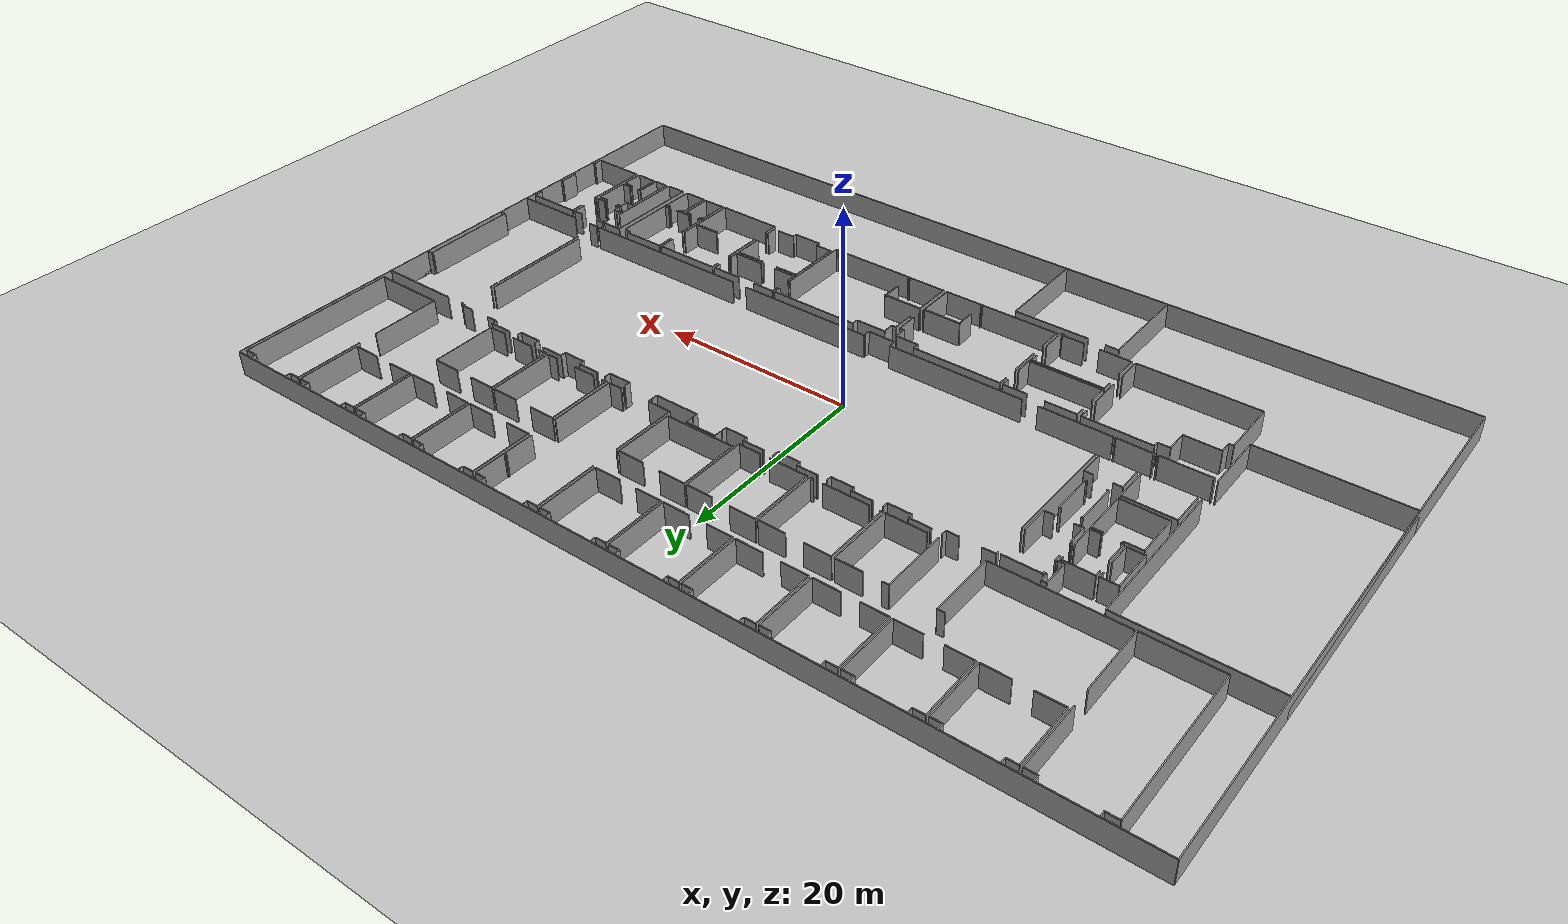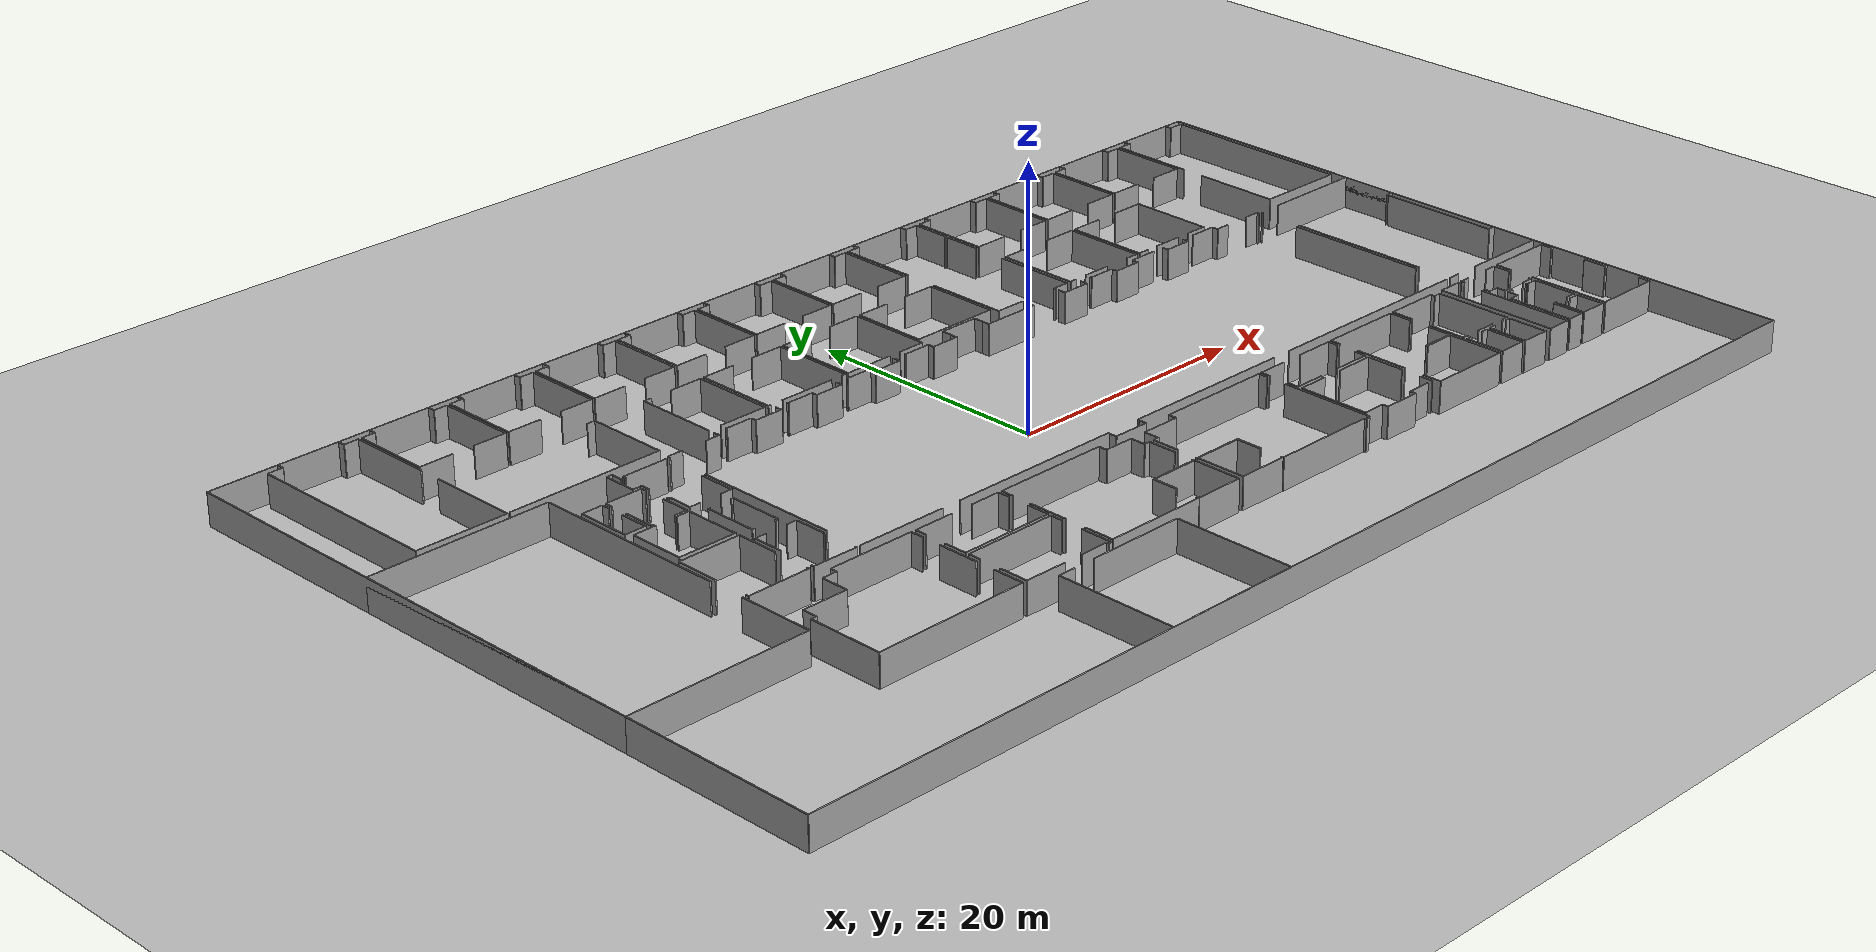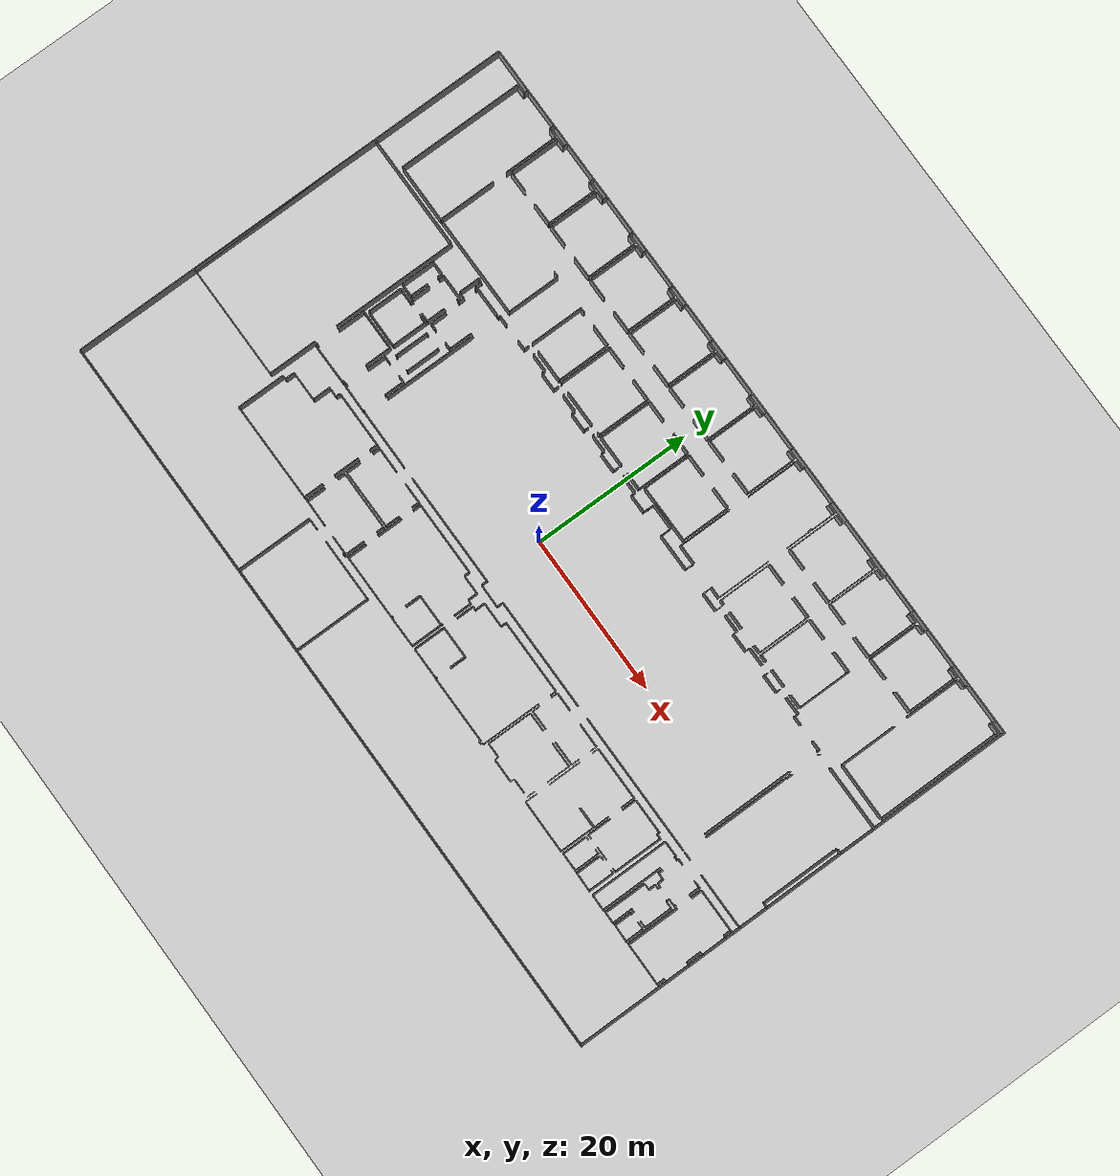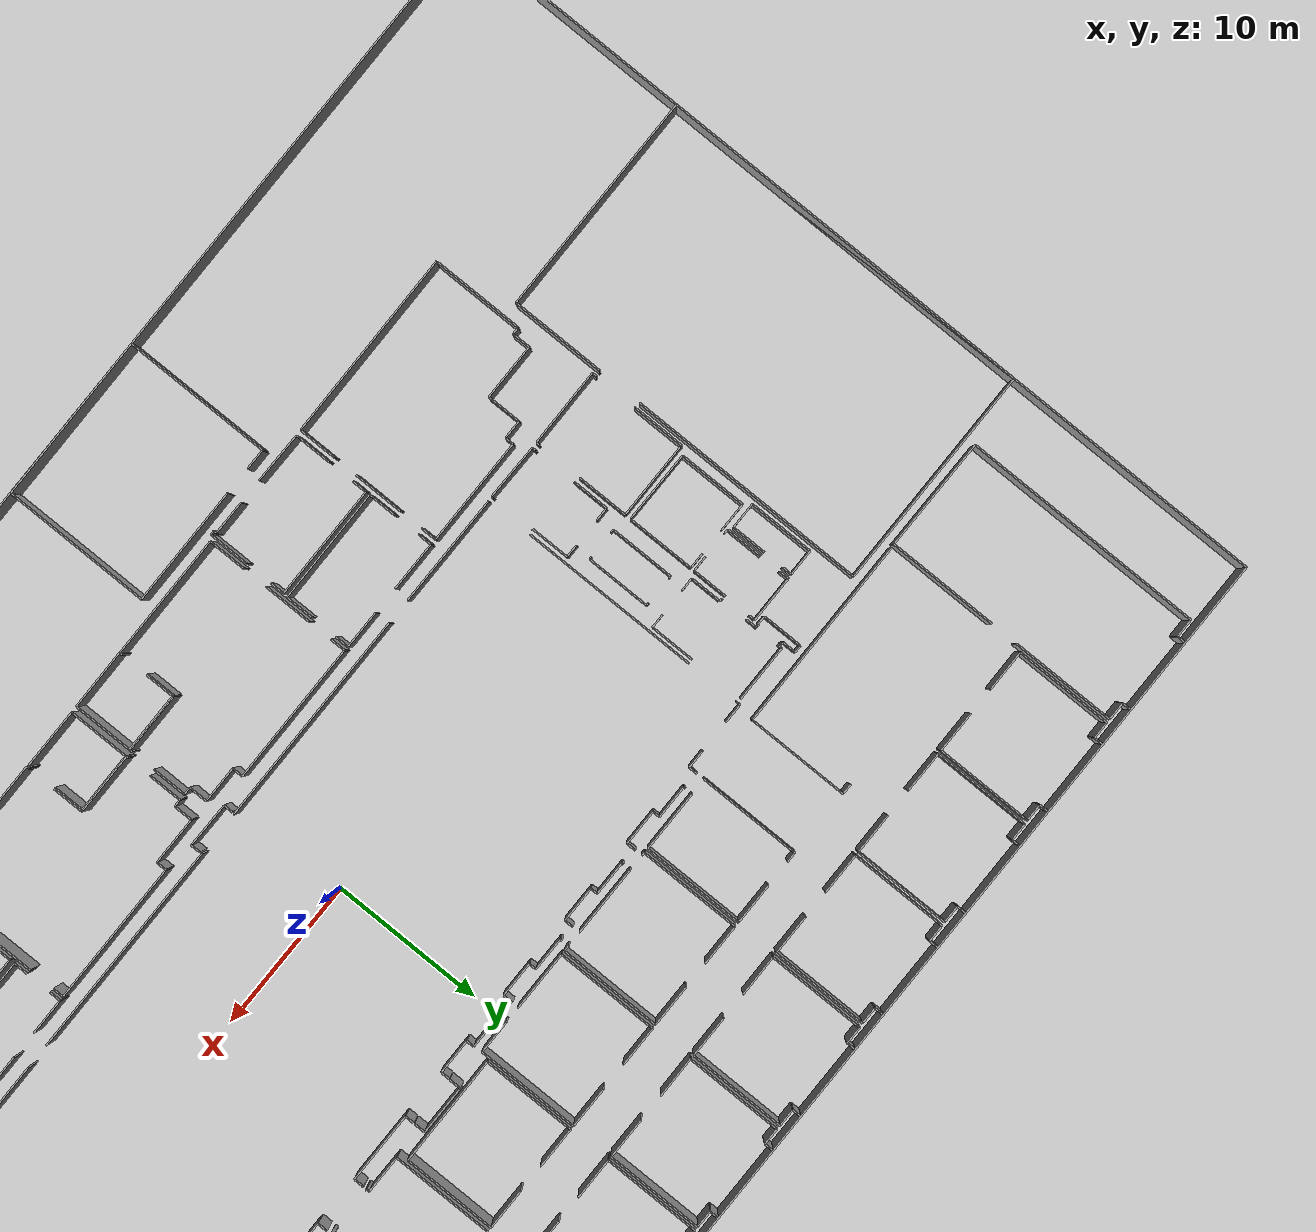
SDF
<sdf version="1.6">
  <world name="default">
    <light name="sun" type="directional">
      <cast_shadows>1</cast_shadows>
      <pose frame="">0 0 10 0 -0 0</pose>
      <diffuse>0.8 0.8 0.8 1</diffuse>
      <specular>0.1 0.1 0.1 1</specular>
      <attenuation>
        <range>1000</range>
        <constant>0.9</constant>
        <linear>0.01</linear>
        <quadratic>0.001</quadratic>
      </attenuation>
      <direction>-0.5 0.5 -1</direction>
    </light>
    <model name="ground_plane">
      <static>1</static>
      <link name="link">
        <collision name="collision">
          <geometry>
            <plane>
              <normal>0 0 1</normal>
              <size>100 100</size>
            </plane>
          </geometry>
          <surface>
            <friction>
              <ode>
                <mu>100</mu>
                <mu2>50</mu2>
              </ode>
              <torsional>
                <ode />
              </torsional>
            </friction>
            <contact>
              <ode />
            </contact>
            <bounce />
          </surface>
          <max_contacts>10</max_contacts>
        </collision>
        <visual name="visual">
          <cast_shadows>0</cast_shadows>
          <geometry>
            <plane>
              <normal>0 0 1</normal>
              <size>100 100</size>
            </plane>
          </geometry>
          <material>
            <script>
              <uri>file://media/materials/scripts/gazebo.material</uri>
              <name>Gazebo/Grey</name>
            </script>
          </material>
        </visual>
        <self_collide>0</self_collide>
        <kinematic>0</kinematic>
        <gravity>1</gravity>
      </link>
    </model>
    <gravity>0 0 -9.8</gravity>
    <magnetic_field>6e-06 2.3e-05 -4.2e-05</magnetic_field>
    <atmosphere type="adiabatic" />
    <physics default="0" name="default_physics" type="ode">
      <max_step_size>0.001</max_step_size>
      <real_time_factor>1</real_time_factor>
      <real_time_update_rate>1000</real_time_update_rate>
    </physics>
    <scene>
      <ambient>0.4 0.4 0.4 1</ambient>
      <background>0.7 0.7 0.7 1</background>
      <shadows>1</shadows>
    </scene>
    <spherical_coordinates>
      <surface_model>EARTH_WGS84</surface_model>
      <latitude_deg>0</latitude_deg>
      <longitude_deg>0</longitude_deg>
      <elevation>0</elevation>
      <heading_deg>0</heading_deg>
    </spherical_coordinates>
  <model name="50045228">
		<static>1</static>
		<link name="Wall_0">
			<collision name="Wall_0_Collision">
				<geometry>
					<box>
						<size>15.7744441978 0.1 2.5</size>
					</box>
				</geometry>
				<pose frame="">7.88722209889 0 1.25 0 0 0</pose>
			</collision>
			<visual name="Wall_0_Visual">
				<pose frame="">7.88722209889 0 1.25 0 0 0</pose>
				<geometry>
					<box>
						<size>15.7744441978 0.1 2.5</size>
					</box>
				</geometry>
				<material>
					<script>
						<uri>file://media/materials/scripts/gazebo.material</uri>
						<name>Gazebo/Grey</name>
					</script>
					<ambient>1 1 1 1</ambient>
				</material>
			</visual>
			<pose frame="">4.30940978719 -16.3473407123 0 0 0 1.57079632679</pose>
		</link>
		<link name="Wall_1">
			<collision name="Wall_1_Collision">
				<geometry>
					<box>
						<size>1.21214043322 0.1 2.5</size>
					</box>
				</geometry>
				<pose frame="">0.606070216612 0 1.25 0 0 0</pose>
			</collision>
			<visual name="Wall_1_Visual">
				<pose frame="">0.606070216612 0 1.25 0 0 0</pose>
				<geometry>
					<box>
						<size>1.21214043322 0.1 2.5</size>
					</box>
				</geometry>
				<material>
					<script>
						<uri>file://media/materials/scripts/gazebo.material</uri>
						<name>Gazebo/Grey</name>
					</script>
					<ambient>1 1 1 1</ambient>
				</material>
			</visual>
			<pose frame="">4.30940978719 -0.572896514541 0 0 0 0.0</pose>
		</link>
		<link name="Wall_2">
			<collision name="Wall_2_Collision">
				<geometry>
					<box>
						<size>0.543972598395 0.1 2.5</size>
					</box>
				</geometry>
				<pose frame="">0.271986299198 0 1.25 0 0 0</pose>
			</collision>
			<visual name="Wall_2_Visual">
				<pose frame="">0.271986299198 0 1.25 0 0 0</pose>
				<geometry>
					<box>
						<size>0.543972598395 0.1 2.5</size>
					</box>
				</geometry>
				<material>
					<script>
						<uri>file://media/materials/scripts/gazebo.material</uri>
						<name>Gazebo/Grey</name>
					</script>
					<ambient>1 1 1 1</ambient>
				</material>
			</visual>
			<pose frame="">5.52155022042 -0.572896514541 0 0 0 1.57079632679</pose>
		</link>
		<link name="Wall_3">
			<collision name="Wall_3_Collision">
				<geometry>
					<box>
						<size>0.573023373823 0.1 2.5</size>
					</box>
				</geometry>
				<pose frame="">0.286511686911 0 1.25 0 0 0</pose>
			</collision>
			<visual name="Wall_3_Visual">
				<pose frame="">0.286511686911 0 1.25 0 0 0</pose>
				<geometry>
					<box>
						<size>0.573023373823 0.1 2.5</size>
					</box>
				</geometry>
				<material>
					<script>
						<uri>file://media/materials/scripts/gazebo.material</uri>
						<name>Gazebo/Grey</name>
					</script>
					<ambient>1 1 1 1</ambient>
				</material>
			</visual>
			<pose frame="">10.4246614443 -0.028923916146 0 0 0 -1.57079632679</pose>
		</link>
		<link name="Wall_4">
			<collision name="Wall_4_Collision">
				<geometry>
					<box>
						<size>1.17433636738 0.1 2.5</size>
					</box>
				</geometry>
				<pose frame="">0.587168183692 0 1.25 0 0 0</pose>
			</collision>
			<visual name="Wall_4_Visual">
				<pose frame="">0.587168183692 0 1.25 0 0 0</pose>
				<geometry>
					<box>
						<size>1.17433636738 0.1 2.5</size>
					</box>
				</geometry>
				<material>
					<script>
						<uri>file://media/materials/scripts/gazebo.material</uri>
						<name>Gazebo/Grey</name>
					</script>
					<ambient>1 1 1 1</ambient>
				</material>
			</visual>
			<pose frame="">10.4246614443 -0.601947289969 0 0 0 0.0</pose>
		</link>
		<link name="Wall_5">
			<collision name="Wall_5_Collision">
				<geometry>
					<box>
						<size>6.80359011766 0.1 2.5</size>
					</box>
				</geometry>
				<pose frame="">3.40179505883 0 1.25 0 0 0</pose>
			</collision>
			<visual name="Wall_5_Visual">
				<pose frame="">3.40179505883 0 1.25 0 0 0</pose>
				<geometry>
					<box>
						<size>6.80359011766 0.1 2.5</size>
					</box>
				</geometry>
				<material>
					<script>
						<uri>file://media/materials/scripts/gazebo.material</uri>
						<name>Gazebo/Grey</name>
					</script>
					<ambient>1 1 1 1</ambient>
				</material>
			</visual>
			<pose frame="">11.5989978117 -0.601947289969 0 0 0 -1.57079632679</pose>
		</link>
		<link name="Wall_6">
			<collision name="Wall_6_Collision">
				<geometry>
					<box>
						<size>7.1868320066 0.1 2.5</size>
					</box>
				</geometry>
				<pose frame="">3.5934160033 0 1.25 0 0 0</pose>
			</collision>
			<visual name="Wall_6_Visual">
				<pose frame="">3.5934160033 0 1.25 0 0 0</pose>
				<geometry>
					<box>
						<size>7.1868320066 0.1 2.5</size>
					</box>
				</geometry>
				<material>
					<script>
						<uri>file://media/materials/scripts/gazebo.material</uri>
						<name>Gazebo/Grey</name>
					</script>
					<ambient>1 1 1 1</ambient>
				</material>
			</visual>
			<pose frame="">11.5989978117 -9.19526814881 0 0 0 -1.57079632679</pose>
		</link>
		<link name="Wall_7">
			<collision name="Wall_7_Collision">
				<geometry>
					<box>
						<size>7.28967089693 0.1 2.5</size>
					</box>
				</geometry>
				<pose frame="">3.64483544847 0 1.25 0 0 0</pose>
			</collision>
			<visual name="Wall_7_Visual">
				<pose frame="">3.64483544847 0 1.25 0 0 0</pose>
				<geometry>
					<box>
						<size>7.28967089693 0.1 2.5</size>
					</box>
				</geometry>
				<material>
					<script>
						<uri>file://media/materials/scripts/gazebo.material</uri>
						<name>Gazebo/Grey</name>
					</script>
					<ambient>1 1 1 1</ambient>
				</material>
			</visual>
			<pose frame="">11.5989978117 -16.3821001554 0 0 0 3.13682432107</pose>
		</link>
		<link name="Wall_8">
			<collision name="Wall_8_Collision">
				<geometry>
					<box>
						<size>0.684025244997 0.1 2.5</size>
					</box>
				</geometry>
				<pose frame="">0.342012622498 0 1.25 0 0 0</pose>
			</collision>
			<visual name="Wall_8_Visual">
				<pose frame="">0.342012622498 0 1.25 0 0 0</pose>
				<geometry>
					<box>
						<size>0.684025244997 0.1 2.5</size>
					</box>
				</geometry>
				<material>
					<script>
						<uri>file://media/materials/scripts/gazebo.material</uri>
						<name>Gazebo/Grey</name>
					</script>
					<ambient>1 1 1 1</ambient>
				</material>
			</visual>
			<pose frame="">23.7437442517 -9.68443753766 0 0 0 0.0</pose>
		</link>
		<link name="Wall_9">
			<collision name="Wall_9_Collision">
				<geometry>
					<box>
						<size>6.64362056389 0.1 2.5</size>
					</box>
				</geometry>
				<pose frame="">3.32181028194 0 1.25 0 0 0</pose>
			</collision>
			<visual name="Wall_9_Visual">
				<pose frame="">3.32181028194 0 1.25 0 0 0</pose>
				<geometry>
					<box>
						<size>6.64362056389 0.1 2.5</size>
					</box>
				</geometry>
				<material>
					<script>
						<uri>file://media/materials/scripts/gazebo.material</uri>
						<name>Gazebo/Grey</name>
					</script>
					<ambient>1 1 1 1</ambient>
				</material>
			</visual>
			<pose frame="">24.4277694967 -9.68443753766 0 0 0 -1.57079632679</pose>
		</link>
		<link name="Wall_10">
			<collision name="Wall_10_Collision">
				<geometry>
					<box>
						<size>12.6084344882 0.1 2.5</size>
					</box>
				</geometry>
				<pose frame="">6.30421724409 0 1.25 0 0 0</pose>
			</collision>
			<visual name="Wall_10_Visual">
				<pose frame="">6.30421724409 0 1.25 0 0 0</pose>
				<geometry>
					<box>
						<size>12.6084344882 0.1 2.5</size>
					</box>
				</geometry>
				<material>
					<script>
						<uri>file://media/materials/scripts/gazebo.material</uri>
						<name>Gazebo/Grey</name>
					</script>
					<ambient>1 1 1 1</ambient>
				</material>
			</visual>
			<pose frame="">24.4277694967 -16.3280581016 0 0 0 -3.13993251164</pose>
		</link>
		<link name="Wall_11">
			<collision name="Wall_11_Collision">
				<geometry>
					<box>
						<size>6.33408391741 0.1 2.5</size>
					</box>
				</geometry>
				<pose frame="">3.16704195871 0 1.25 0 0 0</pose>
			</collision>
			<visual name="Wall_11_Visual">
				<pose frame="">3.16704195871 0 1.25 0 0 0</pose>
				<geometry>
					<box>
						<size>6.33408391741 0.1 2.5</size>
					</box>
				</geometry>
				<material>
					<script>
						<uri>file://media/materials/scripts/gazebo.material</uri>
						<name>Gazebo/Grey</name>
					</script>
					<ambient>1 1 1 1</ambient>
				</material>
			</visual>
			<pose frame="">19.2568583299 -6.91535314452 0 0 0 1.57079632679</pose>
		</link>
		<link name="Wall_12">
			<collision name="Wall_12_Collision">
				<geometry>
					<box>
						<size>1.1470616219 0.1 2.5</size>
					</box>
				</geometry>
				<pose frame="">0.573530810948 0 1.25 0 0 0</pose>
			</collision>
			<visual name="Wall_12_Visual">
				<pose frame="">0.573530810948 0 1.25 0 0 0</pose>
				<geometry>
					<box>
						<size>1.1470616219 0.1 2.5</size>
					</box>
				</geometry>
				<material>
					<script>
						<uri>file://media/materials/scripts/gazebo.material</uri>
						<name>Gazebo/Grey</name>
					</script>
					<ambient>1 1 1 1</ambient>
				</material>
			</visual>
			<pose frame="">19.2568583299 -0.58126922711 0 0 0 0.0</pose>
		</link>
		<link name="Wall_13">
			<collision name="Wall_13_Collision">
				<geometry>
					<box>
						<size>0.575433700168 0.1 2.5</size>
					</box>
				</geometry>
				<pose frame="">0.287716850084 0 1.25 0 0 0</pose>
			</collision>
			<visual name="Wall_13_Visual">
				<pose frame="">0.287716850084 0 1.25 0 0 0</pose>
				<geometry>
					<box>
						<size>0.575433700168 0.1 2.5</size>
					</box>
				</geometry>
				<material>
					<script>
						<uri>file://media/materials/scripts/gazebo.material</uri>
						<name>Gazebo/Grey</name>
					</script>
					<ambient>1 1 1 1</ambient>
				</material>
			</visual>
			<pose frame="">20.4039199518 -0.58126922711 0 0 0 1.57079632679</pose>
		</link>
		<link name="Wall_14">
			<collision name="Wall_14_Collision">
				<geometry>
					<box>
						<size>0.6105737211 0.1 2.5</size>
					</box>
				</geometry>
				<pose frame="">0.30528686055 0 1.25 0 0 0</pose>
			</collision>
			<visual name="Wall_14_Visual">
				<pose frame="">0.30528686055 0 1.25 0 0 0</pose>
				<geometry>
					<box>
						<size>0.6105737211 0.1 2.5</size>
					</box>
				</geometry>
				<material>
					<script>
						<uri>file://media/materials/scripts/gazebo.material</uri>
						<name>Gazebo/Grey</name>
					</script>
					<ambient>1 1 1 1</ambient>
				</material>
			</visual>
			<pose frame="">25.3082997685 -0.00583552694174 0 0 0 -1.57079632679</pose>
		</link>
		<link name="Wall_15">
			<collision name="Wall_15_Collision">
				<geometry>
					<box>
						<size>1.14591988836 0.1 2.5</size>
					</box>
				</geometry>
				<pose frame="">0.572959944182 0 1.25 0 0 0</pose>
			</collision>
			<visual name="Wall_15_Visual">
				<pose frame="">0.572959944182 0 1.25 0 0 0</pose>
				<geometry>
					<box>
						<size>1.14591988836 0.1 2.5</size>
					</box>
				</geometry>
				<material>
					<script>
						<uri>file://media/materials/scripts/gazebo.material</uri>
						<name>Gazebo/Grey</name>
					</script>
					<ambient>1 1 1 1</ambient>
				</material>
			</visual>
			<pose frame="">25.3082997685 -0.616409248042 0 0 0 0.0</pose>
		</link>
		<link name="Wall_16">
			<collision name="Wall_16_Collision">
				<geometry>
					<box>
						<size>6.31162982462 0.1 2.5</size>
					</box>
				</geometry>
				<pose frame="">3.15581491231 0 1.25 0 0 0</pose>
			</collision>
			<visual name="Wall_16_Visual">
				<pose frame="">3.15581491231 0 1.25 0 0 0</pose>
				<geometry>
					<box>
						<size>6.31162982462 0.1 2.5</size>
					</box>
				</geometry>
				<material>
					<script>
						<uri>file://media/materials/scripts/gazebo.material</uri>
						<name>Gazebo/Grey</name>
					</script>
					<ambient>1 1 1 1</ambient>
				</material>
			</visual>
			<pose frame="">26.4542196568 -0.616409248042 0 0 0 -1.57079632679</pose>
		</link>
		<link name="Wall_17">
			<collision name="Wall_17_Collision">
				<geometry>
					<box>
						<size>2.68142462973 0.1 2.5</size>
					</box>
				</geometry>
				<pose frame="">1.34071231486 0 1.25 0 0 0</pose>
			</collision>
			<visual name="Wall_17_Visual">
				<pose frame="">1.34071231486 0 1.25 0 0 0</pose>
				<geometry>
					<box>
						<size>2.68142462973 0.1 2.5</size>
					</box>
				</geometry>
				<material>
					<script>
						<uri>file://media/materials/scripts/gazebo.material</uri>
						<name>Gazebo/Grey</name>
					</script>
					<ambient>1 1 1 1</ambient>
				</material>
			</visual>
			<pose frame="">26.4542196568 -6.92803907266 0 0 0 3.14159265359</pose>
		</link>
		<link name="Wall_18">
			<collision name="Wall_18_Collision">
				<geometry>
					<box>
						<size>2.71862399753 0.1 2.5</size>
					</box>
				</geometry>
				<pose frame="">1.35931199876 0 1.25 0 0 0</pose>
			</collision>
			<visual name="Wall_18_Visual">
				<pose frame="">1.35931199876 0 1.25 0 0 0</pose>
				<geometry>
					<box>
						<size>2.71862399753 0.1 2.5</size>
					</box>
				</geometry>
				<material>
					<script>
						<uri>file://media/materials/scripts/gazebo.material</uri>
						<name>Gazebo/Grey</name>
					</script>
					<ambient>1 1 1 1</ambient>
				</material>
			</visual>
			<pose frame="">21.9754527291 -6.92803907266 0 0 0 3.13692633188</pose>
		</link>
		<link name="Wall_19">
			<collision name="Wall_19_Collision">
				<geometry>
					<box>
						<size>6.32951698329 0.1 2.5</size>
					</box>
				</geometry>
				<pose frame="">3.16475849164 0 1.25 0 0 0</pose>
			</collision>
			<visual name="Wall_19_Visual">
				<pose frame="">3.16475849164 0 1.25 0 0 0</pose>
				<geometry>
					<box>
						<size>6.32951698329 0.1 2.5</size>
					</box>
				</geometry>
				<material>
					<script>
						<uri>file://media/materials/scripts/gazebo.material</uri>
						<name>Gazebo/Grey</name>
					</script>
					<ambient>1 1 1 1</ambient>
				</material>
			</visual>
			<pose frame="">11.8491643145 -6.93146427325 0 0 0 1.57079632679</pose>
		</link>
		<link name="Wall_20">
			<collision name="Wall_20_Collision">
				<geometry>
					<box>
						<size>1.10684722971 0.1 2.5</size>
					</box>
				</geometry>
				<pose frame="">0.553423614855 0 1.25 0 0 0</pose>
			</collision>
			<visual name="Wall_20_Visual">
				<pose frame="">0.553423614855 0 1.25 0 0 0</pose>
				<geometry>
					<box>
						<size>1.10684722971 0.1 2.5</size>
					</box>
				</geometry>
				<material>
					<script>
						<uri>file://media/materials/scripts/gazebo.material</uri>
						<name>Gazebo/Grey</name>
					</script>
					<ambient>1 1 1 1</ambient>
				</material>
			</visual>
			<pose frame="">11.8491643145 -0.601947289969 0 0 0 0.0</pose>
		</link>
		<link name="Wall_21">
			<collision name="Wall_21_Collision">
				<geometry>
					<box>
						<size>0.580254352859 0.1 2.5</size>
					</box>
				</geometry>
				<pose frame="">0.29012717643 0 1.25 0 0 0</pose>
			</collision>
			<visual name="Wall_21_Visual">
				<pose frame="">0.29012717643 0 1.25 0 0 0</pose>
				<geometry>
					<box>
						<size>0.580254352859 0.1 2.5</size>
					</box>
				</geometry>
				<material>
					<script>
						<uri>file://media/materials/scripts/gazebo.material</uri>
						<name>Gazebo/Grey</name>
					</script>
					<ambient>1 1 1 1</ambient>
				</material>
			</visual>
			<pose frame="">12.9560115442 -0.601947289969 0 0 0 1.57079632679</pose>
		</link>
		<link name="Wall_22">
			<collision name="Wall_22_Collision">
				<geometry>
					<box>
						<size>0.592813421712 0.1 2.5</size>
					</box>
				</geometry>
				<pose frame="">0.296406710856 0 1.25 0 0 0</pose>
			</collision>
			<visual name="Wall_22_Visual">
				<pose frame="">0.296406710856 0 1.25 0 0 0</pose>
				<geometry>
					<box>
						<size>0.592813421712 0.1 2.5</size>
					</box>
				</geometry>
				<material>
					<script>
						<uri>file://media/materials/scripts/gazebo.material</uri>
						<name>Gazebo/Grey</name>
					</script>
					<ambient>1 1 1 1</ambient>
				</material>
			</visual>
			<pose frame="">17.8819574387 -0.0216929371095 0 0 0 -1.57079632679</pose>
		</link>
		<link name="Wall_23">
			<collision name="Wall_23_Collision">
				<geometry>
					<box>
						<size>1.12892074466 0.1 2.5</size>
					</box>
				</geometry>
				<pose frame="">0.564460372332 0 1.25 0 0 0</pose>
			</collision>
			<visual name="Wall_23_Visual">
				<pose frame="">0.564460372332 0 1.25 0 0 0</pose>
				<geometry>
					<box>
						<size>1.12892074466 0.1 2.5</size>
					</box>
				</geometry>
				<material>
					<script>
						<uri>file://media/materials/scripts/gazebo.material</uri>
						<name>Gazebo/Grey</name>
					</script>
					<ambient>1 1 1 1</ambient>
				</material>
			</visual>
			<pose frame="">17.8819574387 -0.614506358821 0 0 0 0.0</pose>
		</link>
		<link name="Wall_24">
			<collision name="Wall_24_Collision">
				<geometry>
					<box>
						<size>6.30503314199 0.1 2.5</size>
					</box>
				</geometry>
				<pose frame="">3.15251657099 0 1.25 0 0 0</pose>
			</collision>
			<visual name="Wall_24_Visual">
				<pose frame="">3.15251657099 0 1.25 0 0 0</pose>
				<geometry>
					<box>
						<size>6.30503314199 0.1 2.5</size>
					</box>
				</geometry>
				<material>
					<script>
						<uri>file://media/materials/scripts/gazebo.material</uri>
						<name>Gazebo/Grey</name>
					</script>
					<ambient>1 1 1 1</ambient>
				</material>
			</visual>
			<pose frame="">19.0108781834 -0.614506358821 0 0 0 -1.57079632679</pose>
		</link>
		<link name="Wall_25">
			<collision name="Wall_25_Collision">
				<geometry>
					<box>
						<size>2.69664774349 0.1 2.5</size>
					</box>
				</geometry>
				<pose frame="">1.34832387175 0 1.25 0 0 0</pose>
			</collision>
			<visual name="Wall_25_Visual">
				<pose frame="">1.34832387175 0 1.25 0 0 0</pose>
				<geometry>
					<box>
						<size>2.69664774349 0.1 2.5</size>
					</box>
				</geometry>
				<material>
					<script>
						<uri>file://media/materials/scripts/gazebo.material</uri>
						<name>Gazebo/Grey</name>
					</script>
					<ambient>1 1 1 1</ambient>
				</material>
			</visual>
			<pose frame="">19.0108781834 -6.91953950081 0 0 0 3.14159265359</pose>
		</link>
		<link name="Wall_26">
			<collision name="Wall_26_Collision">
				<geometry>
					<box>
						<size>2.70149471511 0.1 2.5</size>
					</box>
				</geometry>
				<pose frame="">1.35074735755 0 1.25 0 0 0</pose>
			</collision>
			<visual name="Wall_26_Visual">
				<pose frame="">1.35074735755 0 1.25 0 0 0</pose>
				<geometry>
					<box>
						<size>2.70149471511 0.1 2.5</size>
					</box>
				</geometry>
				<material>
					<script>
						<uri>file://media/materials/scripts/gazebo.material</uri>
						<name>Gazebo/Grey</name>
					</script>
					<ambient>1 1 1 1</ambient>
				</material>
			</visual>
			<pose frame="">14.5506327107 -6.91953950081 0 0 0 -3.13717850053</pose>
		</link>
		<link name="Wall_27">
			<collision name="Wall_27_Collision">
				<geometry>
					<box>
						<size>6.32951698329 0.1 2.5</size>
					</box>
				</geometry>
				<pose frame="">3.16475849164 0 1.25 0 0 0</pose>
			</collision>
			<visual name="Wall_27_Visual">
				<pose frame="">3.16475849164 0 1.25 0 0 0</pose>
				<geometry>
					<box>
						<size>6.32951698329 0.1 2.5</size>
					</box>
				</geometry>
				<material>
					<script>
						<uri>file://media/materials/scripts/gazebo.material</uri>
						<name>Gazebo/Grey</name>
					</script>
					<ambient>1 1 1 1</ambient>
				</material>
			</visual>
			<pose frame="">26.7048935968 -6.93146427325 0 0 0 1.57079632679</pose>
		</link>
		<link name="Wall_28">
			<collision name="Wall_28_Collision">
				<geometry>
					<box>
						<size>1.12029431353 0.1 2.5</size>
					</box>
				</geometry>
				<pose frame="">0.560147156766 0 1.25 0 0 0</pose>
			</collision>
			<visual name="Wall_28_Visual">
				<pose frame="">0.560147156766 0 1.25 0 0 0</pose>
				<geometry>
					<box>
						<size>1.12029431353 0.1 2.5</size>
					</box>
				</geometry>
				<material>
					<script>
						<uri>file://media/materials/scripts/gazebo.material</uri>
						<name>Gazebo/Grey</name>
					</script>
					<ambient>1 1 1 1</ambient>
				</material>
			</visual>
			<pose frame="">26.7048935968 -0.601947289969 0 0 0 0.0</pose>
		</link>
		<link name="Wall_29">
			<collision name="Wall_29_Collision">
				<geometry>
					<box>
						<size>0.601947289969 0.1 2.5</size>
					</box>
				</geometry>
				<pose frame="">0.300973644984 0 1.25 0 0 0</pose>
			</collision>
			<visual name="Wall_29_Visual">
				<pose frame="">0.300973644984 0 1.25 0 0 0</pose>
				<geometry>
					<box>
						<size>0.601947289969 0.1 2.5</size>
					</box>
				</geometry>
				<material>
					<script>
						<uri>file://media/materials/scripts/gazebo.material</uri>
						<name>Gazebo/Grey</name>
					</script>
					<ambient>1 1 1 1</ambient>
				</material>
			</visual>
			<pose frame="">27.8251879103 -0.601947289969 0 0 0 1.57079632679</pose>
		</link>
		<link name="Wall_30">
			<collision name="Wall_30_Collision">
				<geometry>
					<box>
						<size>0.615521233072 0.1 2.5</size>
					</box>
				</geometry>
				<pose frame="">0.307760616536 0 1.25 0 0 0</pose>
			</collision>
			<visual name="Wall_30_Visual">
				<pose frame="">0.307760616536 0 1.25 0 0 0</pose>
				<geometry>
					<box>
						<size>0.615521233072 0.1 2.5</size>
					</box>
				</geometry>
				<material>
					<script>
						<uri>file://media/materials/scripts/gazebo.material</uri>
						<name>Gazebo/Grey</name>
					</script>
					<ambient>1 1 1 1</ambient>
				</material>
			</visual>
			<pose frame="">32.7468205893 -0.0 0 0 0 -1.57079632679</pose>
		</link>
		<link name="Wall_31">
			<collision name="Wall_31_Collision">
				<geometry>
					<box>
						<size>1.11141416384 0.1 2.5</size>
					</box>
				</geometry>
				<pose frame="">0.555707081919 0 1.25 0 0 0</pose>
			</collision>
			<visual name="Wall_31_Visual">
				<pose frame="">0.555707081919 0 1.25 0 0 0</pose>
				<geometry>
					<box>
						<size>1.11141416384 0.1 2.5</size>
					</box>
				</geometry>
				<material>
					<script>
						<uri>file://media/materials/scripts/gazebo.material</uri>
						<name>Gazebo/Grey</name>
					</script>
					<ambient>1 1 1 1</ambient>
				</material>
			</visual>
			<pose frame="">32.7468205893 -0.615521233072 0 0 0 0.0</pose>
		</link>
		<link name="Wall_32">
			<collision name="Wall_32_Collision">
				<geometry>
					<box>
						<size>6.31886080365 0.1 2.5</size>
					</box>
				</geometry>
				<pose frame="">3.15943040183 0 1.25 0 0 0</pose>
			</collision>
			<visual name="Wall_32_Visual">
				<pose frame="">3.15943040183 0 1.25 0 0 0</pose>
				<geometry>
					<box>
						<size>6.31886080365 0.1 2.5</size>
					</box>
				</geometry>
				<material>
					<script>
						<uri>file://media/materials/scripts/gazebo.material</uri>
						<name>Gazebo/Grey</name>
					</script>
					<ambient>1 1 1 1</ambient>
				</material>
			</visual>
			<pose frame="">33.8582347531 -0.615521233072 0 0 0 -1.57079632679</pose>
		</link>
		<link name="Wall_33">
			<collision name="Wall_33_Collision">
				<geometry>
					<box>
						<size>2.65567219562 0.1 2.5</size>
					</box>
				</geometry>
				<pose frame="">1.32783609781 0 1.25 0 0 0</pose>
			</collision>
			<visual name="Wall_33_Visual">
				<pose frame="">1.32783609781 0 1.25 0 0 0</pose>
				<geometry>
					<box>
						<size>2.65567219562 0.1 2.5</size>
					</box>
				</geometry>
				<material>
					<script>
						<uri>file://media/materials/scripts/gazebo.material</uri>
						<name>Gazebo/Grey</name>
					</script>
					<ambient>1 1 1 1</ambient>
				</material>
			</visual>
			<pose frame="">33.8582347531 -6.93438203673 0 0 0 3.14159265359</pose>
		</link>
		<link name="Wall_34">
			<collision name="Wall_34_Collision">
				<geometry>
					<box>
						<size>2.71085755323 0.1 2.5</size>
					</box>
				</geometry>
				<pose frame="">1.35542877662 0 1.25 0 0 0</pose>
			</collision>
			<visual name="Wall_34_Visual">
				<pose frame="">1.35542877662 0 1.25 0 0 0</pose>
				<geometry>
					<box>
						<size>2.71085755323 0.1 2.5</size>
					</box>
				</geometry>
				<material>
					<script>
						<uri>file://media/materials/scripts/gazebo.material</uri>
						<name>Gazebo/Grey</name>
					</script>
					<ambient>1 1 1 1</ambient>
				</material>
			</visual>
			<pose frame="">29.4157495798 -6.93438203673 0 0 0 3.14051632849</pose>
		</link>
		<link name="Wall_35">
			<collision name="Wall_35_Collision">
				<geometry>
					<box>
						<size>6.3477847198 0.1 2.5</size>
					</box>
				</geometry>
				<pose frame="">3.1738923599 0 1.25 0 0 0</pose>
			</collision>
			<visual name="Wall_35_Visual">
				<pose frame="">3.1738923599 0 1.25 0 0 0</pose>
				<geometry>
					<box>
						<size>6.3477847198 0.1 2.5</size>
					</box>
				</geometry>
				<material>
					<script>
						<uri>file://media/materials/scripts/gazebo.material</uri>
						<name>Gazebo/Grey</name>
					</script>
					<ambient>1 1 1 1</ambient>
				</material>
			</visual>
			<pose frame="">34.1451904475 -6.93146427325 0 0 0 1.57079632679</pose>
		</link>
		<link name="Wall_36">
			<collision name="Wall_36_Collision">
				<geometry>
					<box>
						<size>1.12892074466 0.1 2.5</size>
					</box>
				</geometry>
				<pose frame="">0.564460372332 0 1.25 0 0 0</pose>
			</collision>
			<visual name="Wall_36_Visual">
				<pose frame="">0.564460372332 0 1.25 0 0 0</pose>
				<geometry>
					<box>
						<size>1.12892074466 0.1 2.5</size>
					</box>
				</geometry>
				<material>
					<script>
						<uri>file://media/materials/scripts/gazebo.material</uri>
						<name>Gazebo/Grey</name>
					</script>
					<ambient>1 1 1 1</ambient>
				</material>
			</visual>
			<pose frame="">34.1451904475 -0.583679553455 0 0 0 0.0</pose>
		</link>
		<link name="Wall_37">
			<collision name="Wall_37_Collision">
				<geometry>
					<box>
						<size>0.573530810948 0.1 2.5</size>
					</box>
				</geometry>
				<pose frame="">0.286765405474 0 1.25 0 0 0</pose>
			</collision>
			<visual name="Wall_37_Visual">
				<pose frame="">0.286765405474 0 1.25 0 0 0</pose>
				<geometry>
					<box>
						<size>0.573530810948 0.1 2.5</size>
					</box>
				</geometry>
				<material>
					<script>
						<uri>file://media/materials/scripts/gazebo.material</uri>
						<name>Gazebo/Grey</name>
					</script>
					<ambient>1 1 1 1</ambient>
				</material>
			</visual>
			<pose frame="">35.2741111922 -0.583679553455 0 0 0 1.57079632679</pose>
		</link>
		<link name="Wall_38">
			<collision name="Wall_38_Collision">
				<geometry>
					<box>
						<size>0.585455583394 0.1 2.5</size>
					</box>
				</geometry>
				<pose frame="">0.292727791697 0 1.25 0 0 0</pose>
			</collision>
			<visual name="Wall_38_Visual">
				<pose frame="">0.292727791697 0 1.25 0 0 0</pose>
				<geometry>
					<box>
						<size>0.585455583394 0.1 2.5</size>
					</box>
				</geometry>
				<material>
					<script>
						<uri>file://media/materials/scripts/gazebo.material</uri>
						<name>Gazebo/Grey</name>
					</script>
					<ambient>1 1 1 1</ambient>
				</material>
			</visual>
			<pose frame="">40.1713868891 -0.0101487425074 0 0 0 -1.57079632679</pose>
		</link>
		<link name="Wall_39">
			<collision name="Wall_39_Collision">
				<geometry>
					<box>
						<size>1.14794963687 0.1 2.5</size>
					</box>
				</geometry>
				<pose frame="">0.573974818433 0 1.25 0 0 0</pose>
			</collision>
			<visual name="Wall_39_Visual">
				<pose frame="">0.573974818433 0 1.25 0 0 0</pose>
				<geometry>
					<box>
						<size>1.14794963687 0.1 2.5</size>
					</box>
				</geometry>
				<material>
					<script>
						<uri>file://media/materials/scripts/gazebo.material</uri>
						<name>Gazebo/Grey</name>
					</script>
					<ambient>1 1 1 1</ambient>
				</material>
			</visual>
			<pose frame="">40.1713868891 -0.595604325901 0 0 0 0.0</pose>
		</link>
		<link name="Wall_40">
			<collision name="Wall_40_Collision">
				<geometry>
					<box>
						<size>6.3192413815 0.1 2.5</size>
					</box>
				</geometry>
				<pose frame="">3.15962069075 0 1.25 0 0 0</pose>
			</collision>
			<visual name="Wall_40_Visual">
				<pose frame="">3.15962069075 0 1.25 0 0 0</pose>
				<geometry>
					<box>
						<size>6.3192413815 0.1 2.5</size>
					</box>
				</geometry>
				<material>
					<script>
						<uri>file://media/materials/scripts/gazebo.material</uri>
						<name>Gazebo/Grey</name>
					</script>
					<ambient>1 1 1 1</ambient>
				</material>
			</visual>
			<pose frame="">41.319336526 -0.595604325901 0 0 0 -1.57079632679</pose>
		</link>
		<link name="Wall_41">
			<collision name="Wall_41_Collision">
				<geometry>
					<box>
						<size>2.69487171355 0.1 2.5</size>
					</box>
				</geometry>
				<pose frame="">1.34743585678 0 1.25 0 0 0</pose>
			</collision>
			<visual name="Wall_41_Visual">
				<pose frame="">1.34743585678 0 1.25 0 0 0</pose>
				<geometry>
					<box>
						<size>2.69487171355 0.1 2.5</size>
					</box>
				</geometry>
				<material>
					<script>
						<uri>file://media/materials/scripts/gazebo.material</uri>
						<name>Gazebo/Grey</name>
					</script>
					<ambient>1 1 1 1</ambient>
				</material>
			</visual>
			<pose frame="">41.319336526 -6.9148457074 0 0 0 3.14159265359</pose>
		</link>
		<link name="Wall_42">
			<collision name="Wall_42_Collision">
				<geometry>
					<box>
						<size>2.70266122368 0.1 2.5</size>
					</box>
				</geometry>
				<pose frame="">1.35133061184 0 1.25 0 0 0</pose>
			</collision>
			<visual name="Wall_42_Visual">
				<pose frame="">1.35133061184 0 1.25 0 0 0</pose>
				<geometry>
					<box>
						<size>2.70266122368 0.1 2.5</size>
					</box>
				</geometry>
				<material>
					<script>
						<uri>file://media/materials/scripts/gazebo.material</uri>
						<name>Gazebo/Grey</name>
					</script>
					<ambient>1 1 1 1</ambient>
				</material>
			</visual>
			<pose frame="">36.8478005772 -6.9148457074 0 0 0 -3.1354436511</pose>
		</link>
		<link name="Wall_43">
			<collision name="Wall_43_Collision">
				<geometry>
					<box>
						<size>6.33091243538 0.1 2.5</size>
					</box>
				</geometry>
				<pose frame="">3.16545621769 0 1.25 0 0 0</pose>
			</collision>
			<visual name="Wall_43_Visual">
				<pose frame="">3.16545621769 0 1.25 0 0 0</pose>
				<geometry>
					<box>
						<size>6.33091243538 0.1 2.5</size>
					</box>
				</geometry>
				<material>
					<script>
						<uri>file://media/materials/scripts/gazebo.material</uri>
						<name>Gazebo/Grey</name>
					</script>
					<ambient>1 1 1 1</ambient>
				</material>
			</visual>
			<pose frame="">41.5856141575 -6.93146427325 0 0 0 1.57079632679</pose>
		</link>
		<link name="Wall_44">
			<collision name="Wall_44_Collision">
				<geometry>
					<box>
						<size>1.0926389902 0.1 2.5</size>
					</box>
				</geometry>
				<pose frame="">0.5463194951 0 1.25 0 0 0</pose>
			</collision>
			<visual name="Wall_44_Visual">
				<pose frame="">0.5463194951 0 1.25 0 0 0</pose>
				<geometry>
					<box>
						<size>1.0926389902 0.1 2.5</size>
					</box>
				</geometry>
				<material>
					<script>
						<uri>file://media/materials/scripts/gazebo.material</uri>
						<name>Gazebo/Grey</name>
					</script>
					<ambient>1 1 1 1</ambient>
				</material>
			</visual>
			<pose frame="">41.5856141575 -0.600551837874 0 0 0 0.0</pose>
		</link>
		<link name="Wall_45">
			<collision name="Wall_45_Collision">
				<geometry>
					<box>
						<size>0.600551837874 0.1 2.5</size>
					</box>
				</geometry>
				<pose frame="">0.300275918937 0 1.25 0 0 0</pose>
			</collision>
			<visual name="Wall_45_Visual">
				<pose frame="">0.300275918937 0 1.25 0 0 0</pose>
				<geometry>
					<box>
						<size>0.600551837874 0.1 2.5</size>
					</box>
				</geometry>
				<material>
					<script>
						<uri>file://media/materials/scripts/gazebo.material</uri>
						<name>Gazebo/Grey</name>
					</script>
					<ambient>1 1 1 1</ambient>
				</material>
			</visual>
			<pose frame="">42.6782531477 -0.600551837874 0 0 0 1.57079632679</pose>
		</link>
		<link name="Wall_46">
			<collision name="Wall_46_Collision">
				<geometry>
					<box>
						<size>0.600551837874 0.1 2.5</size>
					</box>
				</geometry>
				<pose frame="">0.300275918937 0 1.25 0 0 0</pose>
			</collision>
			<visual name="Wall_46_Visual">
				<pose frame="">0.300275918937 0 1.25 0 0 0</pose>
				<geometry>
					<box>
						<size>0.600551837874 0.1 2.5</size>
					</box>
				</geometry>
				<material>
					<script>
						<uri>file://media/materials/scripts/gazebo.material</uri>
						<name>Gazebo/Grey</name>
					</script>
					<ambient>1 1 1 1</ambient>
				</material>
			</visual>
			<pose frame="">47.6162506739 -0.0 0 0 0 -1.57079632679</pose>
		</link>
		<link name="Wall_47">
			<collision name="Wall_47_Collision">
				<geometry>
					<box>
						<size>1.13437569376 0.1 2.5</size>
					</box>
				</geometry>
				<pose frame="">0.567187846881 0 1.25 0 0 0</pose>
			</collision>
			<visual name="Wall_47_Visual">
				<pose frame="">0.567187846881 0 1.25 0 0 0</pose>
				<geometry>
					<box>
						<size>1.13437569376 0.1 2.5</size>
					</box>
				</geometry>
				<material>
					<script>
						<uri>file://media/materials/scripts/gazebo.material</uri>
						<name>Gazebo/Grey</name>
					</script>
					<ambient>1 1 1 1</ambient>
				</material>
			</visual>
			<pose frame="">47.6162506739 -0.600551837874 0 0 0 0.0</pose>
		</link>
		<link name="Wall_48">
			<collision name="Wall_48_Collision">
				<geometry>
					<box>
						<size>6.31429386953 0.1 2.5</size>
					</box>
				</geometry>
				<pose frame="">3.15714693476 0 1.25 0 0 0</pose>
			</collision>
			<visual name="Wall_48_Visual">
				<pose frame="">3.15714693476 0 1.25 0 0 0</pose>
				<geometry>
					<box>
						<size>6.31429386953 0.1 2.5</size>
					</box>
				</geometry>
				<material>
					<script>
						<uri>file://media/materials/scripts/gazebo.material</uri>
						<name>Gazebo/Grey</name>
					</script>
					<ambient>1 1 1 1</ambient>
				</material>
			</visual>
			<pose frame="">48.7506263677 -0.600551837874 0 0 0 -1.57079632679</pose>
		</link>
		<link name="Wall_49">
			<collision name="Wall_49_Collision">
				<geometry>
					<box>
						<size>2.69411055786 0.1 2.5</size>
					</box>
				</geometry>
				<pose frame="">1.34705527893 0 1.25 0 0 0</pose>
			</collision>
			<visual name="Wall_49_Visual">
				<pose frame="">1.34705527893 0 1.25 0 0 0</pose>
				<geometry>
					<box>
						<size>2.69411055786 0.1 2.5</size>
					</box>
				</geometry>
				<material>
					<script>
						<uri>file://media/materials/scripts/gazebo.material</uri>
						<name>Gazebo/Grey</name>
					</script>
					<ambient>1 1 1 1</ambient>
				</material>
			</visual>
			<pose frame="">48.7506263677 -6.9148457074 0 0 0 3.14159265359</pose>
		</link>
		<link name="Wall_50">
			<collision name="Wall_50_Collision">
				<geometry>
					<box>
						<size>2.6899755365 0.1 2.5</size>
					</box>
				</geometry>
				<pose frame="">1.34498776825 0 1.25 0 0 0</pose>
			</collision>
			<visual name="Wall_50_Visual">
				<pose frame="">1.34498776825 0 1.25 0 0 0</pose>
				<geometry>
					<box>
						<size>2.6899755365 0.1 2.5</size>
					</box>
				</geometry>
				<material>
					<script>
						<uri>file://media/materials/scripts/gazebo.material</uri>
						<name>Gazebo/Grey</name>
					</script>
					<ambient>1 1 1 1</ambient>
				</material>
			</visual>
			<pose frame="">44.2755383591 -6.9148457074 0 0 0 -3.13541465258</pose>
		</link>
		<link name="Wall_51">
			<collision name="Wall_51_Collision">
				<geometry>
					<box>
						<size>6.33928514795 0.1 2.5</size>
					</box>
				</geometry>
				<pose frame="">3.16964257397 0 1.25 0 0 0</pose>
			</collision>
			<visual name="Wall_51_Visual">
				<pose frame="">3.16964257397 0 1.25 0 0 0</pose>
				<geometry>
					<box>
						<size>6.33928514795 0.1 2.5</size>
					</box>
				</geometry>
				<material>
					<script>
						<uri>file://media/materials/scripts/gazebo.material</uri>
						<name>Gazebo/Grey</name>
					</script>
					<ambient>1 1 1 1</ambient>
				</material>
			</visual>
			<pose frame="">48.9900098316 -6.92677047985 0 0 0 1.57079632679</pose>
		</link>
		<link name="Wall_52">
			<collision name="Wall_52_Collision">
				<geometry>
					<box>
						<size>1.13881576861 0.1 2.5</size>
					</box>
				</geometry>
				<pose frame="">0.569407884304 0 1.25 0 0 0</pose>
			</collision>
			<visual name="Wall_52_Visual">
				<pose frame="">0.569407884304 0 1.25 0 0 0</pose>
				<geometry>
					<box>
						<size>1.13881576861 0.1 2.5</size>
					</box>
				</geometry>
				<material>
					<script>
						<uri>file://media/materials/scripts/gazebo.material</uri>
						<name>Gazebo/Grey</name>
					</script>
					<ambient>1 1 1 1</ambient>
				</material>
			</visual>
			<pose frame="">48.9900098316 -0.587485331896 0 0 0 0.0</pose>
		</link>
		<link name="Wall_53">
			<collision name="Wall_53_Collision">
				<geometry>
					<box>
						<size>0.587485331896 0.1 2.5</size>
					</box>
				</geometry>
				<pose frame="">0.293742665948 0 1.25 0 0 0</pose>
			</collision>
			<visual name="Wall_53_Visual">
				<pose frame="">0.293742665948 0 1.25 0 0 0</pose>
				<geometry>
					<box>
						<size>0.587485331896 0.1 2.5</size>
					</box>
				</geometry>
				<material>
					<script>
						<uri>file://media/materials/scripts/gazebo.material</uri>
						<name>Gazebo/Grey</name>
					</script>
					<ambient>1 1 1 1</ambient>
				</material>
			</visual>
			<pose frame="">50.1288256002 -0.587485331896 0 0 0 1.57079632679</pose>
		</link>
		<link name="Wall_54">
			<collision name="Wall_54_Collision">
				<geometry>
					<box>
						<size>0.590276236085 0.1 2.5</size>
					</box>
				</geometry>
				<pose frame="">0.295138118043 0 1.25 0 0 0</pose>
			</collision>
			<visual name="Wall_54_Visual">
				<pose frame="">0.295138118043 0 1.25 0 0 0</pose>
				<geometry>
					<box>
						<size>0.590276236085 0.1 2.5</size>
					</box>
				</geometry>
				<material>
					<script>
						<uri>file://media/materials/scripts/gazebo.material</uri>
						<name>Gazebo/Grey</name>
					</script>
					<ambient>1 1 1 1</ambient>
				</material>
			</visual>
			<pose frame="">55.0569281025 -0.0 0 0 0 -1.57079632679</pose>
		</link>
		<link name="Wall_55">
			<collision name="Wall_55_Collision">
				<geometry>
					<box>
						<size>1.11065300815 0.1 2.5</size>
					</box>
				</geometry>
				<pose frame="">0.555326504075 0 1.25 0 0 0</pose>
			</collision>
			<visual name="Wall_55_Visual">
				<pose frame="">0.555326504075 0 1.25 0 0 0</pose>
				<geometry>
					<box>
						<size>1.11065300815 0.1 2.5</size>
					</box>
				</geometry>
				<material>
					<script>
						<uri>file://media/materials/scripts/gazebo.material</uri>
						<name>Gazebo/Grey</name>
					</script>
					<ambient>1 1 1 1</ambient>
				</material>
			</visual>
			<pose frame="">55.0569281025 -0.590276236085 0 0 0 0.0</pose>
		</link>
		<link name="Wall_56">
			<collision name="Wall_56_Collision">
				<geometry>
					<box>
						<size>6.32545748628 0.1 2.5</size>
					</box>
				</geometry>
				<pose frame="">3.16272874314 0 1.25 0 0 0</pose>
			</collision>
			<visual name="Wall_56_Visual">
				<pose frame="">3.16272874314 0 1.25 0 0 0</pose>
				<geometry>
					<box>
						<size>6.32545748628 0.1 2.5</size>
					</box>
				</geometry>
				<material>
					<script>
						<uri>file://media/materials/scripts/gazebo.material</uri>
						<name>Gazebo/Grey</name>
					</script>
					<ambient>1 1 1 1</ambient>
				</material>
			</visual>
			<pose frame="">56.1675811107 -0.590276236085 0 0 0 -1.57079632679</pose>
		</link>
		<link name="Wall_57">
			<collision name="Wall_57_Collision">
				<geometry>
					<box>
						<size>2.69905806984 0.1 2.5</size>
					</box>
				</geometry>
				<pose frame="">1.34952903492 0 1.25 0 0 0</pose>
			</collision>
			<visual name="Wall_57_Visual">
				<pose frame="">1.34952903492 0 1.25 0 0 0</pose>
				<geometry>
					<box>
						<size>2.69905806984 0.1 2.5</size>
					</box>
				</geometry>
				<material>
					<script>
						<uri>file://media/materials/scripts/gazebo.material</uri>
						<name>Gazebo/Grey</name>
					</script>
					<ambient>1 1 1 1</ambient>
				</material>
			</visual>
			<pose frame="">56.1675811107 -6.91573372237 0 0 0 3.14159265359</pose>
		</link>
		<link name="Wall_58">
			<collision name="Wall_58_Collision">
				<geometry>
					<box>
						<size>2.72343741523 0.1 2.5</size>
					</box>
				</geometry>
				<pose frame="">1.36171870762 0 1.25 0 0 0</pose>
			</collision>
			<visual name="Wall_58_Visual">
				<pose frame="">1.36171870762 0 1.25 0 0 0</pose>
				<geometry>
					<box>
						<size>2.72343741523 0.1 2.5</size>
					</box>
				</geometry>
				<material>
					<script>
						<uri>file://media/materials/scripts/gazebo.material</uri>
						<name>Gazebo/Grey</name>
					</script>
					<ambient>1 1 1 1</ambient>
				</material>
			</visual>
			<pose frame="">51.7134248834 -6.91573372237 0 0 0 -3.13754013245</pose>
		</link>
		<link name="Wall_59">
			<collision name="Wall_59_Collision">
				<geometry>
					<box>
						<size>6.36935079763 0.1 2.5</size>
					</box>
				</geometry>
				<pose frame="">3.18467539881 0 1.25 0 0 0</pose>
			</collision>
			<visual name="Wall_59_Visual">
				<pose frame="">3.18467539881 0 1.25 0 0 0</pose>
				<geometry>
					<box>
						<size>6.36935079763 0.1 2.5</size>
					</box>
				</geometry>
				<material>
					<script>
						<uri>file://media/materials/scripts/gazebo.material</uri>
						<name>Gazebo/Grey</name>
					</script>
					<ambient>1 1 1 1</ambient>
				</material>
			</visual>
			<pose frame="">56.4650661254 -6.95315721036 0 0 0 1.57079632679</pose>
		</link>
		<link name="Wall_60">
			<collision name="Wall_60_Collision">
				<geometry>
					<box>
						<size>1.09390758301 0.1 2.5</size>
					</box>
				</geometry>
				<pose frame="">0.546953791507 0 1.25 0 0 0</pose>
			</collision>
			<visual name="Wall_60_Visual">
				<pose frame="">0.546953791507 0 1.25 0 0 0</pose>
				<geometry>
					<box>
						<size>1.09390758301 0.1 2.5</size>
					</box>
				</geometry>
				<material>
					<script>
						<uri>file://media/materials/scripts/gazebo.material</uri>
						<name>Gazebo/Grey</name>
					</script>
					<ambient>1 1 1 1</ambient>
				</material>
			</visual>
			<pose frame="">56.4650661254 -0.583806412737 0 0 0 0.0</pose>
		</link>
		<link name="Wall_61">
			<collision name="Wall_61_Collision">
				<geometry>
					<box>
						<size>0.575560559449 0.1 2.5</size>
					</box>
				</geometry>
				<pose frame="">0.287780279725 0 1.25 0 0 0</pose>
			</collision>
			<visual name="Wall_61_Visual">
				<pose frame="">0.287780279725 0 1.25 0 0 0</pose>
				<geometry>
					<box>
						<size>0.575560559449 0.1 2.5</size>
					</box>
				</geometry>
				<material>
					<script>
						<uri>file://media/materials/scripts/gazebo.material</uri>
						<name>Gazebo/Grey</name>
					</script>
					<ambient>1 1 1 1</ambient>
				</material>
			</visual>
			<pose frame="">57.5589737084 -0.583806412737 0 0 0 1.57079632679</pose>
		</link>
		<link name="Wall_62">
			<collision name="Wall_62_Collision">
				<geometry>
					<box>
						<size>0.601059274999 0.1 2.5</size>
					</box>
				</geometry>
				<pose frame="">0.3005296375 0 1.25 0 0 0</pose>
			</collision>
			<visual name="Wall_62_Visual">
				<pose frame="">0.3005296375 0 1.25 0 0 0</pose>
				<geometry>
					<box>
						<size>0.601059274999 0.1 2.5</size>
					</box>
				</geometry>
				<material>
					<script>
						<uri>file://media/materials/scripts/gazebo.material</uri>
						<name>Gazebo/Grey</name>
					</script>
					<ambient>1 1 1 1</ambient>
				</material>
			</visual>
			<pose frame="">62.4563762646 -0.00824585328724 0 0 0 -1.57079632679</pose>
		</link>
		<link name="Wall_63">
			<collision name="Wall_63_Collision">
				<geometry>
					<box>
						<size>1.11141416384 0.1 2.5</size>
					</box>
				</geometry>
				<pose frame="">0.555707081919 0 1.25 0 0 0</pose>
			</collision>
			<visual name="Wall_63_Visual">
				<pose frame="">0.555707081919 0 1.25 0 0 0</pose>
				<geometry>
					<box>
						<size>1.11141416384 0.1 2.5</size>
					</box>
				</geometry>
				<material>
					<script>
						<uri>file://media/materials/scripts/gazebo.material</uri>
						<name>Gazebo/Grey</name>
					</script>
					<ambient>1 1 1 1</ambient>
				</material>
			</visual>
			<pose frame="">62.4563762646 -0.609305128286 0 0 0 0.0</pose>
		</link>
		<link name="Wall_64">
			<collision name="Wall_64_Collision">
				<geometry>
					<box>
						<size>3.15258000063 0.1 2.5</size>
					</box>
				</geometry>
				<pose frame="">1.57629000032 0 1.25 0 0 0</pose>
			</collision>
			<visual name="Wall_64_Visual">
				<pose frame="">1.57629000032 0 1.25 0 0 0</pose>
				<geometry>
					<box>
						<size>3.15258000063 0.1 2.5</size>
					</box>
				</geometry>
				<material>
					<script>
						<uri>file://media/materials/scripts/gazebo.material</uri>
						<name>Gazebo/Grey</name>
					</script>
					<ambient>1 1 1 1</ambient>
				</material>
			</visual>
			<pose frame="">63.5677904285 -0.609305128286 0 0 0 -1.57079632679</pose>
		</link>
		<link name="Wall_65">
			<collision name="Wall_65_Collision">
				<geometry>
					<box>
						<size>0.135612571755 0.1 2.5</size>
					</box>
				</geometry>
				<pose frame="">0.0678062858774 0 1.25 0 0 0</pose>
			</collision>
			<visual name="Wall_65_Visual">
				<pose frame="">0.0678062858774 0 1.25 0 0 0</pose>
				<geometry>
					<box>
						<size>0.135612571755 0.1 2.5</size>
					</box>
				</geometry>
				<material>
					<script>
						<uri>file://media/materials/scripts/gazebo.material</uri>
						<name>Gazebo/Grey</name>
					</script>
					<ambient>1 1 1 1</ambient>
				</material>
			</visual>
			<pose frame="">63.5677904285 -3.76188512892 0 0 0 3.14159265359</pose>
		</link>
		<link name="Wall_66">
			<collision name="Wall_66_Collision">
				<geometry>
					<box>
						<size>0.119755161587 0.1 2.5</size>
					</box>
				</geometry>
				<pose frame="">0.0598775807935 0 1.25 0 0 0</pose>
			</collision>
			<visual name="Wall_66_Visual">
				<pose frame="">0.0598775807935 0 1.25 0 0 0</pose>
				<geometry>
					<box>
						<size>0.119755161587 0.1 2.5</size>
					</box>
				</geometry>
				<material>
					<script>
						<uri>file://media/materials/scripts/gazebo.material</uri>
						<name>Gazebo/Grey</name>
					</script>
					<ambient>1 1 1 1</ambient>
				</material>
			</visual>
			<pose frame="">63.4321778567 -3.76188512892 0 0 0 -1.57079632679</pose>
		</link>
		<link name="Wall_67">
			<collision name="Wall_67_Collision">
				<geometry>
					<box>
						<size>0.132441089721 0.1 2.5</size>
					</box>
				</geometry>
				<pose frame="">0.0662205448606 0 1.25 0 0 0</pose>
			</collision>
			<visual name="Wall_67_Visual">
				<pose frame="">0.0662205448606 0 1.25 0 0 0</pose>
				<geometry>
					<box>
						<size>0.132441089721 0.1 2.5</size>
					</box>
				</geometry>
				<material>
					<script>
						<uri>file://media/materials/scripts/gazebo.material</uri>
						<name>Gazebo/Grey</name>
					</script>
					<ambient>1 1 1 1</ambient>
				</material>
			</visual>
			<pose frame="">63.4321778567 -3.88164029051 0 0 0 0.0</pose>
		</link>
		<link name="Wall_68">
			<collision name="Wall_68_Collision">
				<geometry>
					<box>
						<size>3.05883099172 0.1 2.5</size>
					</box>
				</geometry>
				<pose frame="">1.52941549586 0 1.25 0 0 0</pose>
			</collision>
			<visual name="Wall_68_Visual">
				<pose frame="">1.52941549586 0 1.25 0 0 0</pose>
				<geometry>
					<box>
						<size>3.05883099172 0.1 2.5</size>
					</box>
				</geometry>
				<material>
					<script>
						<uri>file://media/materials/scripts/gazebo.material</uri>
						<name>Gazebo/Grey</name>
					</script>
					<ambient>1 1 1 1</ambient>
				</material>
			</visual>
			<pose frame="">63.5646189464 -3.88164029051 0 0 0 -1.57079632679</pose>
		</link>
		<link name="Wall_69">
			<collision name="Wall_69_Collision">
				<geometry>
					<box>
						<size>6.33433763598 0.1 2.5</size>
					</box>
				</geometry>
				<pose frame="">3.16716881799 0 1.25 0 0 0</pose>
			</collision>
			<visual name="Wall_69_Visual">
				<pose frame="">3.16716881799 0 1.25 0 0 0</pose>
				<geometry>
					<box>
						<size>6.33433763598 0.1 2.5</size>
					</box>
				</geometry>
				<material>
					<script>
						<uri>file://media/materials/scripts/gazebo.material</uri>
						<name>Gazebo/Grey</name>
					</script>
					<ambient>1 1 1 1</ambient>
				</material>
			</visual>
			<pose frame="">63.8765659193 -6.92182296787 0 0 0 1.57079632679</pose>
		</link>
		<link name="Wall_70">
			<collision name="Wall_70_Collision">
				<geometry>
					<box>
						<size>1.14312898417 0.1 2.5</size>
					</box>
				</geometry>
				<pose frame="">0.571564492087 0 1.25 0 0 0</pose>
			</collision>
			<visual name="Wall_70_Visual">
				<pose frame="">0.571564492087 0 1.25 0 0 0</pose>
				<geometry>
					<box>
						<size>1.14312898417 0.1 2.5</size>
					</box>
				</geometry>
				<material>
					<script>
						<uri>file://media/materials/scripts/gazebo.material</uri>
						<name>Gazebo/Grey</name>
					</script>
					<ambient>1 1 1 1</ambient>
				</material>
			</visual>
			<pose frame="">63.8765659193 -0.587485331896 0 0 0 0.0</pose>
		</link>
		<link name="Wall_71">
			<collision name="Wall_71_Collision">
				<geometry>
					<box>
						<size>0.573023373823 0.1 2.5</size>
					</box>
				</geometry>
				<pose frame="">0.286511686911 0 1.25 0 0 0</pose>
			</collision>
			<visual name="Wall_71_Visual">
				<pose frame="">0.286511686911 0 1.25 0 0 0</pose>
				<geometry>
					<box>
						<size>0.573023373823 0.1 2.5</size>
					</box>
				</geometry>
				<material>
					<script>
						<uri>file://media/materials/scripts/gazebo.material</uri>
						<name>Gazebo/Grey</name>
					</script>
					<ambient>1 1 1 1</ambient>
				</material>
			</visual>
			<pose frame="">65.0196949034 -0.587485331896 0 0 0 1.57079632679</pose>
		</link>
		<link name="Wall_72">
			<collision name="Wall_72_Collision">
				<geometry>
					<box>
						<size>0.573023373823 0.1 2.5</size>
					</box>
				</geometry>
				<pose frame="">0.286511686911 0 1.25 0 0 0</pose>
			</collision>
			<visual name="Wall_72_Visual">
				<pose frame="">0.286511686911 0 1.25 0 0 0</pose>
				<geometry>
					<box>
						<size>0.573023373823 0.1 2.5</size>
					</box>
				</geometry>
				<material>
					<script>
						<uri>file://media/materials/scripts/gazebo.material</uri>
						<name>Gazebo/Grey</name>
					</script>
					<ambient>1 1 1 1</ambient>
				</material>
			</visual>
			<pose frame="">69.9155751483 -0.014461958073 0 0 0 -1.57079632679</pose>
		</link>
		<link name="Wall_73">
			<collision name="Wall_73_Collision">
				<geometry>
					<box>
						<size>1.13145793029 0.1 2.5</size>
					</box>
				</geometry>
				<pose frame="">0.565728965145 0 1.25 0 0 0</pose>
			</collision>
			<visual name="Wall_73_Visual">
				<pose frame="">0.565728965145 0 1.25 0 0 0</pose>
				<geometry>
					<box>
						<size>1.13145793029 0.1 2.5</size>
					</box>
				</geometry>
				<material>
					<script>
						<uri>file://media/materials/scripts/gazebo.material</uri>
						<name>Gazebo/Grey</name>
					</script>
					<ambient>1 1 1 1</ambient>
				</material>
			</visual>
			<pose frame="">69.9155751483 -0.587485331896 0 0 0 0.0</pose>
		</link>
		<link name="Wall_74">
			<collision name="Wall_74_Collision">
				<geometry>
					<box>
						<size>6.3273603755 0.1 2.5</size>
					</box>
				</geometry>
				<pose frame="">3.16368018775 0 1.25 0 0 0</pose>
			</collision>
			<visual name="Wall_74_Visual">
				<pose frame="">3.16368018775 0 1.25 0 0 0</pose>
				<geometry>
					<box>
						<size>6.3273603755 0.1 2.5</size>
					</box>
				</geometry>
				<material>
					<script>
						<uri>file://media/materials/scripts/gazebo.material</uri>
						<name>Gazebo/Grey</name>
					</script>
					<ambient>1 1 1 1</ambient>
				</material>
			</visual>
			<pose frame="">71.0470330786 -0.587485331896 0 0 0 -1.57079632679</pose>
		</link>
		<link name="Wall_75">
			<collision name="Wall_75_Collision">
				<geometry>
					<box>
						<size>2.66911927944 0.1 2.5</size>
					</box>
				</geometry>
				<pose frame="">1.33455963972 0 1.25 0 0 0</pose>
			</collision>
			<visual name="Wall_75_Visual">
				<pose frame="">1.33455963972 0 1.25 0 0 0</pose>
				<geometry>
					<box>
						<size>2.66911927944 0.1 2.5</size>
					</box>
				</geometry>
				<material>
					<script>
						<uri>file://media/materials/scripts/gazebo.material</uri>
						<name>Gazebo/Grey</name>
					</script>
					<ambient>1 1 1 1</ambient>
				</material>
			</visual>
			<pose frame="">71.0470330786 -6.9148457074 0 0 0 3.14159265359</pose>
		</link>
		<link name="Wall_76">
			<collision name="Wall_76_Collision">
				<geometry>
					<box>
						<size>2.70756663172 0.1 2.5</size>
					</box>
				</geometry>
				<pose frame="">1.35378331586 0 1.25 0 0 0</pose>
			</collision>
			<visual name="Wall_76_Visual">
				<pose frame="">1.35378331586 0 1.25 0 0 0</pose>
				<geometry>
					<box>
						<size>2.70756663172 0.1 2.5</size>
					</box>
				</geometry>
				<material>
					<script>
						<uri>file://media/materials/scripts/gazebo.material</uri>
						<name>Gazebo/Grey</name>
					</script>
					<ambient>1 1 1 1</ambient>
				</material>
			</visual>
			<pose frame="">66.5841235609 -6.9148457074 0 0 0 -3.13901570198</pose>
		</link>
		<link name="Wall_77">
			<collision name="Wall_77_Collision">
				<geometry>
					<box>
						<size>6.33839713298 0.1 2.5</size>
					</box>
				</geometry>
				<pose frame="">3.16919856649 0 1.25 0 0 0</pose>
			</collision>
			<visual name="Wall_77_Visual">
				<pose frame="">3.16919856649 0 1.25 0 0 0</pose>
				<geometry>
					<box>
						<size>6.33839713298 0.1 2.5</size>
					</box>
				</geometry>
				<material>
					<script>
						<uri>file://media/materials/scripts/gazebo.material</uri>
						<name>Gazebo/Grey</name>
					</script>
					<ambient>1 1 1 1</ambient>
				</material>
			</visual>
			<pose frame="">71.329929276 -6.93400145888 0 0 0 1.57079632679</pose>
		</link>
		<link name="Wall_78">
			<collision name="Wall_78_Collision">
				<geometry>
					<box>
						<size>1.09619105008 0.1 2.5</size>
					</box>
				</geometry>
				<pose frame="">0.548095525039 0 1.25 0 0 0</pose>
			</collision>
			<visual name="Wall_78_Visual">
				<pose frame="">0.548095525039 0 1.25 0 0 0</pose>
				<geometry>
					<box>
						<size>1.09619105008 0.1 2.5</size>
					</box>
				</geometry>
				<material>
					<script>
						<uri>file://media/materials/scripts/gazebo.material</uri>
						<name>Gazebo/Grey</name>
					</script>
					<ambient>1 1 1 1</ambient>
				</material>
			</visual>
			<pose frame="">71.329929276 -0.595604325901 0 0 0 0.0</pose>
		</link>
		<link name="Wall_79">
			<collision name="Wall_79_Collision">
				<geometry>
					<box>
						<size>0.562874631315 0.1 2.5</size>
					</box>
				</geometry>
				<pose frame="">0.281437315658 0 1.25 0 0 0</pose>
			</collision>
			<visual name="Wall_79_Visual">
				<pose frame="">0.281437315658 0 1.25 0 0 0</pose>
				<geometry>
					<box>
						<size>0.562874631315 0.1 2.5</size>
					</box>
				</geometry>
				<material>
					<script>
						<uri>file://media/materials/scripts/gazebo.material</uri>
						<name>Gazebo/Grey</name>
					</script>
					<ambient>1 1 1 1</ambient>
				</material>
			</visual>
			<pose frame="">72.426120326 -0.595604325901 0 0 0 1.57079632679</pose>
		</link>
		<link name="Wall_80">
			<collision name="Wall_80_Collision">
				<geometry>
					<box>
						<size>0.574418825917 0.1 2.5</size>
					</box>
				</geometry>
				<pose frame="">0.287209412959 0 1.25 0 0 0</pose>
			</collision>
			<visual name="Wall_80_Visual">
				<pose frame="">0.287209412959 0 1.25 0 0 0</pose>
				<geometry>
					<box>
						<size>0.574418825917 0.1 2.5</size>
					</box>
				</geometry>
				<material>
					<script>
						<uri>file://media/materials/scripts/gazebo.material</uri>
						<name>Gazebo/Grey</name>
					</script>
					<ambient>1 1 1 1</ambient>
				</material>
			</visual>
			<pose frame="">77.315277029 -0.0327296945863 0 0 0 -1.57079632679</pose>
		</link>
		<link name="Wall_81">
			<collision name="Wall_81_Collision">
				<geometry>
					<box>
						<size>1.15695664584 0.1 2.5</size>
					</box>
				</geometry>
				<pose frame="">0.57847832292 0 1.25 0 0 0</pose>
			</collision>
			<visual name="Wall_81_Visual">
				<pose frame="">0.57847832292 0 1.25 0 0 0</pose>
				<geometry>
					<box>
						<size>1.15695664584 0.1 2.5</size>
					</box>
				</geometry>
				<material>
					<script>
						<uri>file://media/materials/scripts/gazebo.material</uri>
						<name>Gazebo/Grey</name>
					</script>
					<ambient>1 1 1 1</ambient>
				</material>
			</visual>
			<pose frame="">77.315277029 -0.607148520504 0 0 0 0.0</pose>
		</link>
		<link name="Wall_82">
			<collision name="Wall_82_Collision">
				<geometry>
					<box>
						<size>6.31949510006 0.1 2.5</size>
					</box>
				</geometry>
				<pose frame="">3.15974755003 0 1.25 0 0 0</pose>
			</collision>
			<visual name="Wall_82_Visual">
				<pose frame="">3.15974755003 0 1.25 0 0 0</pose>
				<geometry>
					<box>
						<size>6.31949510006 0.1 2.5</size>
					</box>
				</geometry>
				<material>
					<script>
						<uri>file://media/materials/scripts/gazebo.material</uri>
						<name>Gazebo/Grey</name>
					</script>
					<ambient>1 1 1 1</ambient>
				</material>
			</visual>
			<pose frame="">78.4722336748 -0.607148520504 0 0 0 -1.57079632679</pose>
		</link>
		<link name="Wall_83">
			<collision name="Wall_83_Collision">
				<geometry>
					<box>
						<size>2.68193206685 0.1 2.5</size>
					</box>
				</geometry>
				<pose frame="">1.34096603343 0 1.25 0 0 0</pose>
			</collision>
			<visual name="Wall_83_Visual">
				<pose frame="">1.34096603343 0 1.25 0 0 0</pose>
				<geometry>
					<box>
						<size>2.68193206685 0.1 2.5</size>
					</box>
				</geometry>
				<material>
					<script>
						<uri>file://media/materials/scripts/gazebo.material</uri>
						<name>Gazebo/Grey</name>
					</script>
					<ambient>1 1 1 1</ambient>
				</material>
			</visual>
			<pose frame="">78.4722336748 -6.92664362056 0 0 0 3.14159265359</pose>
		</link>
		<link name="Wall_84">
			<collision name="Wall_84_Collision">
				<geometry>
					<box>
						<size>2.67483806694 0.1 2.5</size>
					</box>
				</geometry>
				<pose frame="">1.33741903347 0 1.25 0 0 0</pose>
			</collision>
			<visual name="Wall_84_Visual">
				<pose frame="">1.33741903347 0 1.25 0 0 0</pose>
				<geometry>
					<box>
						<size>2.67483806694 0.1 2.5</size>
					</box>
				</geometry>
				<material>
					<script>
						<uri>file://media/materials/scripts/gazebo.material</uri>
						<name>Gazebo/Grey</name>
					</script>
					<ambient>1 1 1 1</ambient>
				</material>
			</visual>
			<pose frame="">74.0047572231 -6.92664362056 0 0 0 -3.13884188984</pose>
		</link>
		<link name="Wall_85">
			<collision name="Wall_85_Collision">
				<geometry>
					<box>
						<size>6.32253972281 0.1 2.5</size>
					</box>
				</geometry>
				<pose frame="">3.16126986141 0 1.25 0 0 0</pose>
			</collision>
			<visual name="Wall_85_Visual">
				<pose frame="">3.16126986141 0 1.25 0 0 0</pose>
				<geometry>
					<box>
						<size>6.32253972281 0.1 2.5</size>
					</box>
				</geometry>
				<material>
					<script>
						<uri>file://media/materials/scripts/gazebo.material</uri>
						<name>Gazebo/Grey</name>
					</script>
					<ambient>1 1 1 1</ambient>
				</material>
			</visual>
			<pose frame="">78.7539881387 -6.92309156069 0 0 0 1.57079632679</pose>
		</link>
		<link name="Wall_86">
			<collision name="Wall_86_Collision">
				<geometry>
					<box>
						<size>1.10101170277 0.1 2.5</size>
					</box>
				</geometry>
				<pose frame="">0.550505851384 0 1.25 0 0 0</pose>
			</collision>
			<visual name="Wall_86_Visual">
				<pose frame="">0.550505851384 0 1.25 0 0 0</pose>
				<geometry>
					<box>
						<size>1.10101170277 0.1 2.5</size>
					</box>
				</geometry>
				<material>
					<script>
						<uri>file://media/materials/scripts/gazebo.material</uri>
						<name>Gazebo/Grey</name>
					</script>
					<ambient>1 1 1 1</ambient>
				</material>
			</visual>
			<pose frame="">78.7539881387 -0.600551837874 0 0 0 0.0</pose>
		</link>
		<link name="Wall_87">
			<collision name="Wall_87_Collision">
				<geometry>
					<box>
						<size>0.567187846881 0.1 2.5</size>
					</box>
				</geometry>
				<pose frame="">0.28359392344 0 1.25 0 0 0</pose>
			</collision>
			<visual name="Wall_87_Visual">
				<pose frame="">0.28359392344 0 1.25 0 0 0</pose>
				<geometry>
					<box>
						<size>0.567187846881 0.1 2.5</size>
					</box>
				</geometry>
				<material>
					<script>
						<uri>file://media/materials/scripts/gazebo.material</uri>
						<name>Gazebo/Grey</name>
					</script>
					<ambient>1 1 1 1</ambient>
				</material>
			</visual>
			<pose frame="">79.8549998414 -0.600551837874 0 0 0 1.57079632679</pose>
		</link>
		<link name="Wall_88">
			<collision name="Wall_88_Collision">
				<geometry>
					<box>
						<size>0.567187846881 0.1 2.5</size>
					</box>
				</geometry>
				<pose frame="">0.28359392344 0 1.25 0 0 0</pose>
			</collision>
			<visual name="Wall_88_Visual">
				<pose frame="">0.28359392344 0 1.25 0 0 0</pose>
				<geometry>
					<box>
						<size>0.567187846881 0.1 2.5</size>
					</box>
				</geometry>
				<material>
					<script>
						<uri>file://media/materials/scripts/gazebo.material</uri>
						<name>Gazebo/Grey</name>
					</script>
					<ambient>1 1 1 1</ambient>
				</material>
			</visual>
			<pose frame="">84.7929973677 -0.033363990993 0 0 0 -1.57079632679</pose>
		</link>
		<link name="Wall_89">
			<collision name="Wall_89_Collision">
				<geometry>
					<box>
						<size>1.11775712791 0.1 2.5</size>
					</box>
				</geometry>
				<pose frame="">0.558878563953 0 1.25 0 0 0</pose>
			</collision>
			<visual name="Wall_89_Visual">
				<pose frame="">0.558878563953 0 1.25 0 0 0</pose>
				<geometry>
					<box>
						<size>1.11775712791 0.1 2.5</size>
					</box>
				</geometry>
				<material>
					<script>
						<uri>file://media/materials/scripts/gazebo.material</uri>
						<name>Gazebo/Grey</name>
					</script>
					<ambient>1 1 1 1</ambient>
				</material>
			</visual>
			<pose frame="">84.7929973677 -0.600551837874 0 0 0 0.0</pose>
		</link>
		<link name="Wall_90">
			<collision name="Wall_90_Collision">
				<geometry>
					<box>
						<size>6.3117566839 0.1 2.5</size>
					</box>
				</geometry>
				<pose frame="">3.15587834195 0 1.25 0 0 0</pose>
			</collision>
			<visual name="Wall_90_Visual">
				<pose frame="">3.15587834195 0 1.25 0 0 0</pose>
				<geometry>
					<box>
						<size>6.3117566839 0.1 2.5</size>
					</box>
				</geometry>
				<material>
					<script>
						<uri>file://media/materials/scripts/gazebo.material</uri>
						<name>Gazebo/Grey</name>
					</script>
					<ambient>1 1 1 1</ambient>
				</material>
			</visual>
			<pose frame="">85.9107544956 -0.600551837874 0 0 0 -1.57079632679</pose>
		</link>
		<link name="Wall_91">
			<collision name="Wall_91_Collision">
				<geometry>
					<box>
						<size>2.69449113571 0.1 2.5</size>
					</box>
				</geometry>
				<pose frame="">1.34724556785 0 1.25 0 0 0</pose>
			</collision>
			<visual name="Wall_91_Visual">
				<pose frame="">1.34724556785 0 1.25 0 0 0</pose>
				<geometry>
					<box>
						<size>2.69449113571 0.1 2.5</size>
					</box>
				</geometry>
				<material>
					<script>
						<uri>file://media/materials/scripts/gazebo.material</uri>
						<name>Gazebo/Grey</name>
					</script>
					<ambient>1 1 1 1</ambient>
				</material>
			</visual>
			<pose frame="">85.9107544956 -6.91230852177 0 0 0 3.14159265359</pose>
		</link>
		<link name="Wall_92">
			<collision name="Wall_92_Collision">
				<geometry>
					<box>
						<size>2.70263164104 0.1 2.5</size>
					</box>
				</geometry>
				<pose frame="">1.35131582052 0 1.25 0 0 0</pose>
			</collision>
			<visual name="Wall_92_Visual">
				<pose frame="">1.35131582052 0 1.25 0 0 0</pose>
				<geometry>
					<box>
						<size>2.70263164104 0.1 2.5</size>
					</box>
				</geometry>
				<material>
					<script>
						<uri>file://media/materials/scripts/gazebo.material</uri>
						<name>Gazebo/Grey</name>
					</script>
					<ambient>1 1 1 1</ambient>
				</material>
			</visual>
			<pose frame="">81.4565982684 -6.91230852177 0 0 0 -3.1376028137</pose>
		</link>
		<link name="Wall_93">
			<collision name="Wall_93_Collision">
				<geometry>
					<box>
						<size>7.06327106657 0.1 2.5</size>
					</box>
				</geometry>
				<pose frame="">3.53163553328 0 1.25 0 0 0</pose>
			</collision>
			<visual name="Wall_93_Visual">
				<pose frame="">3.53163553328 0 1.25 0 0 0</pose>
				<geometry>
					<box>
						<size>7.06327106657 0.1 2.5</size>
					</box>
				</geometry>
				<material>
					<script>
						<uri>file://media/materials/scripts/gazebo.material</uri>
						<name>Gazebo/Grey</name>
					</script>
					<ambient>1 1 1 1</ambient>
				</material>
			</visual>
			<pose frame="">86.2161047858 -16.3215882782 0 0 0 1.57079632679</pose>
		</link>
		<link name="Wall_94">
			<collision name="Wall_94_Collision">
				<geometry>
					<box>
						<size>6.81475373442 0.1 2.5</size>
					</box>
				</geometry>
				<pose frame="">3.40737686721 0 1.25 0 0 0</pose>
			</collision>
			<visual name="Wall_94_Visual">
				<pose frame="">3.40737686721 0 1.25 0 0 0</pose>
				<geometry>
					<box>
						<size>6.81475373442 0.1 2.5</size>
					</box>
				</geometry>
				<material>
					<script>
						<uri>file://media/materials/scripts/gazebo.material</uri>
						<name>Gazebo/Grey</name>
					</script>
					<ambient>1 1 1 1</ambient>
				</material>
			</visual>
			<pose frame="">86.2161047858 -7.41530557229 0 0 0 1.57079632679</pose>
		</link>
		<link name="Wall_95">
			<collision name="Wall_95_Collision">
				<geometry>
					<box>
						<size>1.0851542926 0.1 2.5</size>
					</box>
				</geometry>
				<pose frame="">0.5425771463 0 1.25 0 0 0</pose>
			</collision>
			<visual name="Wall_95_Visual">
				<pose frame="">0.5425771463 0 1.25 0 0 0</pose>
				<geometry>
					<box>
						<size>1.0851542926 0.1 2.5</size>
					</box>
				</geometry>
				<material>
					<script>
						<uri>file://media/materials/scripts/gazebo.material</uri>
						<name>Gazebo/Grey</name>
					</script>
					<ambient>1 1 1 1</ambient>
				</material>
			</visual>
			<pose frame="">86.2161047858 -0.600551837874 0 0 0 0.0</pose>
		</link>
		<link name="Wall_96">
			<collision name="Wall_96_Collision">
				<geometry>
					<box>
						<size>0.571627921728 0.1 2.5</size>
					</box>
				</geometry>
				<pose frame="">0.285813960864 0 1.25 0 0 0</pose>
			</collision>
			<visual name="Wall_96_Visual">
				<pose frame="">0.285813960864 0 1.25 0 0 0</pose>
				<geometry>
					<box>
						<size>0.571627921728 0.1 2.5</size>
					</box>
				</geometry>
				<material>
					<script>
						<uri>file://media/materials/scripts/gazebo.material</uri>
						<name>Gazebo/Grey</name>
					</script>
					<ambient>1 1 1 1</ambient>
				</material>
			</visual>
			<pose frame="">87.3012590784 -0.600551837874 0 0 0 1.57079632679</pose>
		</link>
		<link name="Wall_97">
			<collision name="Wall_97_Collision">
				<geometry>
					<box>
						<size>0.543972598395 0.1 2.5</size>
					</box>
				</geometry>
				<pose frame="">0.271986299198 0 1.25 0 0 0</pose>
			</collision>
			<visual name="Wall_97_Visual">
				<pose frame="">0.271986299198 0 1.25 0 0 0</pose>
				<geometry>
					<box>
						<size>0.543972598395 0.1 2.5</size>
					</box>
				</geometry>
				<material>
					<script>
						<uri>file://media/materials/scripts/gazebo.material</uri>
						<name>Gazebo/Grey</name>
					</script>
					<ambient>1 1 1 1</ambient>
				</material>
			</visual>
			<pose frame="">92.2119818591 -0.028923916146 0 0 0 -1.57079632679</pose>
		</link>
		<link name="Wall_98">
			<collision name="Wall_98_Collision">
				<geometry>
					<box>
						<size>1.23307221465 0.1 2.5</size>
					</box>
				</geometry>
				<pose frame="">0.616536107323 0 1.25 0 0 0</pose>
			</collision>
			<visual name="Wall_98_Visual">
				<pose frame="">0.616536107323 0 1.25 0 0 0</pose>
				<geometry>
					<box>
						<size>1.23307221465 0.1 2.5</size>
					</box>
				</geometry>
				<material>
					<script>
						<uri>file://media/materials/scripts/gazebo.material</uri>
						<name>Gazebo/Grey</name>
					</script>
					<ambient>1 1 1 1</ambient>
				</material>
			</visual>
			<pose frame="">92.2119818591 -0.572896514541 0 0 0 0.0</pose>
		</link>
		<link name="Wall_99">
			<collision name="Wall_99_Collision">
				<geometry>
					<box>
						<size>15.797532587 0.1 2.5</size>
					</box>
				</geometry>
				<pose frame="">7.89876629349 0 1.25 0 0 0</pose>
			</collision>
			<visual name="Wall_99_Visual">
				<pose frame="">7.89876629349 0 1.25 0 0 0</pose>
				<geometry>
					<box>
						<size>15.797532587 0.1 2.5</size>
					</box>
				</geometry>
				<material>
					<script>
						<uri>file://media/materials/scripts/gazebo.material</uri>
						<name>Gazebo/Grey</name>
					</script>
					<ambient>1 1 1 1</ambient>
				</material>
			</visual>
			<pose frame="">93.4450540738 -0.572896514541 0 0 0 -1.57079632679</pose>
		</link>
		<link name="Wall_100">
			<collision name="Wall_100_Collision">
				<geometry>
					<box>
						<size>7.22911427732 0.1 2.5</size>
					</box>
				</geometry>
				<pose frame="">3.61455713866 0 1.25 0 0 0</pose>
			</collision>
			<visual name="Wall_100_Visual">
				<pose frame="">3.61455713866 0 1.25 0 0 0</pose>
				<geometry>
					<box>
						<size>7.22911427732 0.1 2.5</size>
					</box>
				</geometry>
				<material>
					<script>
						<uri>file://media/materials/scripts/gazebo.material</uri>
						<name>Gazebo/Grey</name>
					</script>
					<ambient>1 1 1 1</ambient>
				</material>
			</visual>
			<pose frame="">93.4450540738 -16.3704291015 0 0 0 3.13483647392</pose>
		</link>
		<link name="Wall_101">
			<collision name="Wall_101_Collision">
				<geometry>
					<box>
						<size>6.64146395611 0.1 2.5</size>
					</box>
				</geometry>
				<pose frame="">3.32073197805 0 1.25 0 0 0</pose>
			</collision>
			<visual name="Wall_101_Visual">
				<pose frame="">3.32073197805 0 1.25 0 0 0</pose>
				<geometry>
					<box>
						<size>6.64146395611 0.1 2.5</size>
					</box>
				</geometry>
				<material>
					<script>
						<uri>file://media/materials/scripts/gazebo.material</uri>
						<name>Gazebo/Grey</name>
					</script>
					<ambient>1 1 1 1</ambient>
				</material>
			</visual>
			<pose frame="">71.3456598268 -16.3534299578 0 0 0 1.57079632679</pose>
		</link>
		<link name="Wall_102">
			<collision name="Wall_102_Collision">
				<geometry>
					<box>
						<size>2.63892677048 0.1 2.5</size>
					</box>
				</geometry>
				<pose frame="">1.31946338524 0 1.25 0 0 0</pose>
			</collision>
			<visual name="Wall_102_Visual">
				<pose frame="">1.31946338524 0 1.25 0 0 0</pose>
				<geometry>
					<box>
						<size>2.63892677048 0.1 2.5</size>
					</box>
				</geometry>
				<material>
					<script>
						<uri>file://media/materials/scripts/gazebo.material</uri>
						<name>Gazebo/Grey</name>
					</script>
					<ambient>1 1 1 1</ambient>
				</material>
			</visual>
			<pose frame="">71.3456598268 -9.71196600171 0 0 0 0.0</pose>
		</link>
		<link name="Wall_103">
			<collision name="Wall_103_Collision">
				<geometry>
					<box>
						<size>2.7054010339 0.1 2.5</size>
					</box>
				</geometry>
				<pose frame="">1.35270051695 0 1.25 0 0 0</pose>
			</collision>
			<visual name="Wall_103_Visual">
				<pose frame="">1.35270051695 0 1.25 0 0 0</pose>
				<geometry>
					<box>
						<size>2.7054010339 0.1 2.5</size>
					</box>
				</geometry>
				<material>
					<script>
						<uri>file://media/materials/scripts/gazebo.material</uri>
						<name>Gazebo/Grey</name>
					</script>
					<ambient>1 1 1 1</ambient>
				</material>
			</visual>
			<pose frame="">75.7762202277 -9.71196600171 0 0 0 0.0</pose>
		</link>
		<link name="Wall_104">
			<collision name="Wall_104_Collision">
				<geometry>
					<box>
						<size>6.64641146808 0.1 2.5</size>
					</box>
				</geometry>
				<pose frame="">3.32320573404 0 1.25 0 0 0</pose>
			</collision>
			<visual name="Wall_104_Visual">
				<pose frame="">3.32320573404 0 1.25 0 0 0</pose>
				<geometry>
					<box>
						<size>6.64641146808 0.1 2.5</size>
					</box>
				</geometry>
				<material>
					<script>
						<uri>file://media/materials/scripts/gazebo.material</uri>
						<name>Gazebo/Grey</name>
					</script>
					<ambient>1 1 1 1</ambient>
				</material>
			</visual>
			<pose frame="">78.4816212616 -9.71196600171 0 0 0 -1.57079632679</pose>
		</link>
		<link name="Wall_105">
			<collision name="Wall_105_Collision">
				<geometry>
					<box>
						<size>1.78529066633 0.1 2.5</size>
					</box>
				</geometry>
				<pose frame="">0.892645333164 0 1.25 0 0 0</pose>
			</collision>
			<visual name="Wall_105_Visual">
				<pose frame="">0.892645333164 0 1.25 0 0 0</pose>
				<geometry>
					<box>
						<size>1.78529066633 0.1 2.5</size>
					</box>
				</geometry>
				<material>
					<script>
						<uri>file://media/materials/scripts/gazebo.material</uri>
						<name>Gazebo/Grey</name>
					</script>
					<ambient>1 1 1 1</ambient>
				</material>
			</visual>
			<pose frame="">78.4816212616 -16.3583774698 0 0 0 3.14159265359</pose>
		</link>
		<link name="Wall_106">
			<collision name="Wall_106_Collision">
				<geometry>
					<box>
						<size>2.31048809108 0.1 2.5</size>
					</box>
				</geometry>
				<pose frame="">1.15524404554 0 1.25 0 0 0</pose>
			</collision>
			<visual name="Wall_106_Visual">
				<pose frame="">1.15524404554 0 1.25 0 0 0</pose>
				<geometry>
					<box>
						<size>2.31048809108 0.1 2.5</size>
					</box>
				</geometry>
				<material>
					<script>
						<uri>file://media/materials/scripts/gazebo.material</uri>
						<name>Gazebo/Grey</name>
					</script>
					<ambient>1 1 1 1</ambient>
				</material>
			</visual>
			<pose frame="">75.6010275602 -16.3583774698 0 0 0 3.14159265359</pose>
		</link>
		<link name="Wall_107">
			<collision name="Wall_107_Collision">
				<geometry>
					<box>
						<size>0.918855094627 0.1 2.5</size>
					</box>
				</geometry>
				<pose frame="">0.459427547313 0 1.25 0 0 0</pose>
			</collision>
			<visual name="Wall_107_Visual">
				<pose frame="">0.459427547313 0 1.25 0 0 0</pose>
				<geometry>
					<box>
						<size>0.918855094627 0.1 2.5</size>
					</box>
				</geometry>
				<material>
					<script>
						<uri>file://media/materials/scripts/gazebo.material</uri>
						<name>Gazebo/Grey</name>
					</script>
					<ambient>1 1 1 1</ambient>
				</material>
			</visual>
			<pose frame="">72.2645016016 -16.3583774698 0 0 0 3.13620819645</pose>
		</link>
		<link name="Wall_108">
			<collision name="Wall_108_Collision">
				<geometry>
					<box>
						<size>6.65224699502 0.1 2.5</size>
					</box>
				</geometry>
				<pose frame="">3.32612349751 0 1.25 0 0 0</pose>
			</collision>
			<visual name="Wall_108_Visual">
				<pose frame="">3.32612349751 0 1.25 0 0 0</pose>
				<geometry>
					<box>
						<size>6.65224699502 0.1 2.5</size>
					</box>
				</geometry>
				<material>
					<script>
						<uri>file://media/materials/scripts/gazebo.material</uri>
						<name>Gazebo/Grey</name>
					</script>
					<ambient>1 1 1 1</ambient>
				</material>
			</visual>
			<pose frame="">63.8900130031 -16.3569820177 0 0 0 1.57079632679</pose>
		</link>
		<link name="Wall_109">
			<collision name="Wall_109_Collision">
				<geometry>
					<box>
						<size>2.67457422854 0.1 2.5</size>
					</box>
				</geometry>
				<pose frame="">1.33728711427 0 1.25 0 0 0</pose>
			</collision>
			<visual name="Wall_109_Visual">
				<pose frame="">1.33728711427 0 1.25 0 0 0</pose>
				<geometry>
					<box>
						<size>2.67457422854 0.1 2.5</size>
					</box>
				</geometry>
				<material>
					<script>
						<uri>file://media/materials/scripts/gazebo.material</uri>
						<name>Gazebo/Grey</name>
					</script>
					<ambient>1 1 1 1</ambient>
				</material>
			</visual>
			<pose frame="">63.8900130031 -9.70473502268 0 0 0 0.0</pose>
		</link>
		<link name="Wall_110">
			<collision name="Wall_110_Collision">
				<geometry>
					<box>
						<size>2.69943864768 0.1 2.5</size>
					</box>
				</geometry>
				<pose frame="">1.34971932384 0 1.25 0 0 0</pose>
			</collision>
			<visual name="Wall_110_Visual">
				<pose frame="">1.34971932384 0 1.25 0 0 0</pose>
				<geometry>
					<box>
						<size>2.69943864768 0.1 2.5</size>
					</box>
				</geometry>
				<material>
					<script>
						<uri>file://media/materials/scripts/gazebo.material</uri>
						<name>Gazebo/Grey</name>
					</script>
					<ambient>1 1 1 1</ambient>
				</material>
			</visual>
			<pose frame="">68.3517807872 -9.70473502268 0 0 0 0.0</pose>
		</link>
		<link name="Wall_111">
			<collision name="Wall_111_Collision">
				<geometry>
					<box>
						<size>6.63562842916 0.1 2.5</size>
					</box>
				</geometry>
				<pose frame="">3.31781421458 0 1.25 0 0 0</pose>
			</collision>
			<visual name="Wall_111_Visual">
				<pose frame="">3.31781421458 0 1.25 0 0 0</pose>
				<geometry>
					<box>
						<size>6.63562842916 0.1 2.5</size>
					</box>
				</geometry>
				<material>
					<script>
						<uri>file://media/materials/scripts/gazebo.material</uri>
						<name>Gazebo/Grey</name>
					</script>
					<ambient>1 1 1 1</ambient>
				</material>
			</visual>
			<pose frame="">71.0512194348 -9.70473502268 0 0 0 -1.57079632679</pose>
		</link>
		<link name="Wall_112">
			<collision name="Wall_112_Collision">
				<geometry>
					<box>
						<size>1.02210522977 0.1 2.5</size>
					</box>
				</geometry>
				<pose frame="">0.511052614887 0 1.25 0 0 0</pose>
			</collision>
			<visual name="Wall_112_Visual">
				<pose frame="">0.511052614887 0 1.25 0 0 0</pose>
				<geometry>
					<box>
						<size>1.02210522977 0.1 2.5</size>
					</box>
				</geometry>
				<material>
					<script>
						<uri>file://media/materials/scripts/gazebo.material</uri>
						<name>Gazebo/Grey</name>
					</script>
					<ambient>1 1 1 1</ambient>
				</material>
			</visual>
			<pose frame="">71.0512194348 -16.3403634518 0 0 0 3.14159265359</pose>
		</link>
		<link name="Wall_113">
			<collision name="Wall_113_Collision">
				<geometry>
					<box>
						<size>2.26875138752 0.1 2.5</size>
					</box>
				</geometry>
				<pose frame="">1.13437569376 0 1.25 0 0 0</pose>
			</collision>
			<visual name="Wall_113_Visual">
				<pose frame="">1.13437569376 0 1.25 0 0 0</pose>
				<geometry>
					<box>
						<size>2.26875138752 0.1 2.5</size>
					</box>
				</geometry>
				<material>
					<script>
						<uri>file://media/materials/scripts/gazebo.material</uri>
						<name>Gazebo/Grey</name>
					</script>
					<ambient>1 1 1 1</ambient>
				</material>
			</visual>
			<pose frame="">67.7686086708 -16.3403634518 0 0 0 3.14159265359</pose>
		</link>
		<link name="Wall_114">
			<collision name="Wall_114_Collision">
				<geometry>
					<box>
						<size>0.584042895928 0.1 2.5</size>
					</box>
				</geometry>
				<pose frame="">0.292021447964 0 1.25 0 0 0</pose>
			</collision>
			<visual name="Wall_114_Visual">
				<pose frame="">0.292021447964 0 1.25 0 0 0</pose>
				<geometry>
					<box>
						<size>0.584042895928 0.1 2.5</size>
					</box>
				</geometry>
				<material>
					<script>
						<uri>file://media/materials/scripts/gazebo.material</uri>
						<name>Gazebo/Grey</name>
					</script>
					<ambient>1 1 1 1</ambient>
				</material>
			</visual>
			<pose frame="">64.4738194158 -16.3403634518 0 0 0 -3.11313445415</pose>
		</link>
		<link name="Wall_115">
			<collision name="Wall_115_Collision">
				<geometry>
					<box>
						<size>6.66594779741 0.1 2.5</size>
					</box>
				</geometry>
				<pose frame="">3.3329738987 0 1.25 0 0 0</pose>
			</collision>
			<visual name="Wall_115_Visual">
				<pose frame="">3.3329738987 0 1.25 0 0 0</pose>
				<geometry>
					<box>
						<size>6.66594779741 0.1 2.5</size>
					</box>
				</geometry>
				<material>
					<script>
						<uri>file://media/materials/scripts/gazebo.material</uri>
						<name>Gazebo/Grey</name>
					</script>
					<ambient>1 1 1 1</ambient>
				</material>
			</visual>
			<pose frame="">56.4521264787 -16.3416320447 0 0 0 1.57079632679</pose>
		</link>
		<link name="Wall_116">
			<collision name="Wall_116_Collision">
				<geometry>
					<box>
						<size>6.68510354889 0.1 2.5</size>
					</box>
				</geometry>
				<pose frame="">3.34255177444 0 1.25 0 0 0</pose>
			</collision>
			<visual name="Wall_116_Visual">
				<pose frame="">3.34255177444 0 1.25 0 0 0</pose>
				<geometry>
					<box>
						<size>6.68510354889 0.1 2.5</size>
					</box>
				</geometry>
				<material>
					<script>
						<uri>file://media/materials/scripts/gazebo.material</uri>
						<name>Gazebo/Grey</name>
					</script>
					<ambient>1 1 1 1</ambient>
				</material>
			</visual>
			<pose frame="">63.549522692 -9.67568424725 0 0 0 -1.57079632679</pose>
		</link>
		<link name="Wall_117">
			<collision name="Wall_117_Collision">
				<geometry>
					<box>
						<size>1.38999714567 0.1 2.5</size>
					</box>
				</geometry>
				<pose frame="">0.694998572833 0 1.25 0 0 0</pose>
			</collision>
			<visual name="Wall_117_Visual">
				<pose frame="">0.694998572833 0 1.25 0 0 0</pose>
				<geometry>
					<box>
						<size>1.38999714567 0.1 2.5</size>
					</box>
				</geometry>
				<material>
					<script>
						<uri>file://media/materials/scripts/gazebo.material</uri>
						<name>Gazebo/Grey</name>
					</script>
					<ambient>1 1 1 1</ambient>
				</material>
			</visual>
			<pose frame="">63.549522692 -16.3607877961 0 0 0 3.14159265359</pose>
		</link>
		<link name="Wall_118">
			<collision name="Wall_118_Collision">
				<geometry>
					<box>
						<size>0.191811233389 0.1 2.5</size>
					</box>
				</geometry>
				<pose frame="">0.0959056166947 0 1.25 0 0 0</pose>
			</collision>
			<visual name="Wall_118_Visual">
				<pose frame="">0.0959056166947 0 1.25 0 0 0</pose>
				<geometry>
					<box>
						<size>0.191811233389 0.1 2.5</size>
					</box>
				</geometry>
				<material>
					<script>
						<uri>file://media/materials/scripts/gazebo.material</uri>
						<name>Gazebo/Grey</name>
					</script>
					<ambient>1 1 1 1</ambient>
				</material>
			</visual>
			<pose frame="">62.1595255463 -16.3607877961 0 0 0 -1.57079632679</pose>
		</link>
		<link name="Wall_119">
			<collision name="Wall_119_Collision">
				<geometry>
					<box>
						<size>0.0986965208842 0.1 2.5</size>
					</box>
				</geometry>
				<pose frame="">0.0493482604421 0 1.25 0 0 0</pose>
			</collision>
			<visual name="Wall_119_Visual">
				<pose frame="">0.0493482604421 0 1.25 0 0 0</pose>
				<geometry>
					<box>
						<size>0.0986965208842 0.1 2.5</size>
					</box>
				</geometry>
				<material>
					<script>
						<uri>file://media/materials/scripts/gazebo.material</uri>
						<name>Gazebo/Grey</name>
					</script>
					<ambient>1 1 1 1</ambient>
				</material>
			</visual>
			<pose frame="">59.0187434588 -16.5525990295 0 0 0 3.14159265359</pose>
		</link>
		<link name="Wall_120">
			<collision name="Wall_120_Collision">
				<geometry>
					<box>
						<size>0.203609146554 0.1 2.5</size>
					</box>
				</geometry>
				<pose frame="">0.101804573277 0 1.25 0 0 0</pose>
			</collision>
			<visual name="Wall_120_Visual">
				<pose frame="">0.101804573277 0 1.25 0 0 0</pose>
				<geometry>
					<box>
						<size>0.203609146554 0.1 2.5</size>
					</box>
				</geometry>
				<material>
					<script>
						<uri>file://media/materials/scripts/gazebo.material</uri>
						<name>Gazebo/Grey</name>
					</script>
					<ambient>1 1 1 1</ambient>
				</material>
			</visual>
			<pose frame="">58.9200469379 -16.5525990295 0 0 0 1.57079632679</pose>
		</link>
		<link name="Wall_121">
			<collision name="Wall_121_Collision">
				<geometry>
					<box>
						<size>2.46793142751 0.1 2.5</size>
					</box>
				</geometry>
				<pose frame="">1.23396571375 0 1.25 0 0 0</pose>
			</collision>
			<visual name="Wall_121_Visual">
				<pose frame="">1.23396571375 0 1.25 0 0 0</pose>
				<geometry>
					<box>
						<size>2.46793142751 0.1 2.5</size>
					</box>
				</geometry>
				<material>
					<script>
						<uri>file://media/materials/scripts/gazebo.material</uri>
						<name>Gazebo/Grey</name>
					</script>
					<ambient>1 1 1 1</ambient>
				</material>
			</visual>
			<pose frame="">58.9200469379 -16.348989883 0 0 0 3.13861127042</pose>
		</link>
		<link name="Wall_122">
			<collision name="Wall_122_Collision">
				<geometry>
					<box>
						<size>6.0982525134 0.1 2.5</size>
					</box>
				</geometry>
				<pose frame="">3.0491262567 0 1.25 0 0 0</pose>
			</collision>
			<visual name="Wall_122_Visual">
				<pose frame="">3.0491262567 0 1.25 0 0 0</pose>
				<geometry>
					<box>
						<size>6.0982525134 0.1 2.5</size>
					</box>
				</geometry>
				<material>
					<script>
						<uri>file://media/materials/scripts/gazebo.material</uri>
						<name>Gazebo/Grey</name>
					</script>
					<ambient>1 1 1 1</ambient>
				</material>
			</visual>
			<pose frame="">48.9803685262 -15.7825631918 0 0 0 1.57079632679</pose>
		</link>
		<link name="Wall_123">
			<collision name="Wall_123_Collision">
				<geometry>
					<box>
						<size>2.71415432432 0.1 2.5</size>
					</box>
				</geometry>
				<pose frame="">1.35707716216 0 1.25 0 0 0</pose>
			</collision>
			<visual name="Wall_123_Visual">
				<pose frame="">1.35707716216 0 1.25 0 0 0</pose>
				<geometry>
					<box>
						<size>2.71415432432 0.1 2.5</size>
					</box>
				</geometry>
				<material>
					<script>
						<uri>file://media/materials/scripts/gazebo.material</uri>
						<name>Gazebo/Grey</name>
					</script>
					<ambient>1 1 1 1</ambient>
				</material>
			</visual>
			<pose frame="">48.9803685262 -9.68431067838 0 0 0 0.0</pose>
		</link>
		<link name="Wall_124">
			<collision name="Wall_124_Collision">
				<geometry>
					<box>
						<size>2.69423741715 0.1 2.5</size>
					</box>
				</geometry>
				<pose frame="">1.34711870857 0 1.25 0 0 0</pose>
			</collision>
			<visual name="Wall_124_Visual">
				<pose frame="">1.34711870857 0 1.25 0 0 0</pose>
				<geometry>
					<box>
						<size>2.69423741715 0.1 2.5</size>
					</box>
				</geometry>
				<material>
					<script>
						<uri>file://media/materials/scripts/gazebo.material</uri>
						<name>Gazebo/Grey</name>
					</script>
					<ambient>1 1 1 1</ambient>
				</material>
			</visual>
			<pose frame="">53.4718213821 -9.68431067838 0 0 0 0.0</pose>
		</link>
		<link name="Wall_125">
			<collision name="Wall_125_Collision">
				<geometry>
					<box>
						<size>6.07211950144 0.1 2.5</size>
					</box>
				</geometry>
				<pose frame="">3.03605975072 0 1.25 0 0 0</pose>
			</collision>
			<visual name="Wall_125_Visual">
				<pose frame="">3.03605975072 0 1.25 0 0 0</pose>
				<geometry>
					<box>
						<size>6.07211950144 0.1 2.5</size>
					</box>
				</geometry>
				<material>
					<script>
						<uri>file://media/materials/scripts/gazebo.material</uri>
						<name>Gazebo/Grey</name>
					</script>
					<ambient>1 1 1 1</ambient>
				</material>
			</visual>
			<pose frame="">56.1660587993 -9.68431067838 0 0 0 -1.57079632679</pose>
		</link>
		<link name="Wall_126">
			<collision name="Wall_126_Collision">
				<geometry>
					<box>
						<size>7.18573779335 0.1 2.5</size>
					</box>
				</geometry>
				<pose frame="">3.59286889667 0 1.25 0 0 0</pose>
			</collision>
			<visual name="Wall_126_Visual">
				<pose frame="">3.59286889667 0 1.25 0 0 0</pose>
				<geometry>
					<box>
						<size>7.18573779335 0.1 2.5</size>
					</box>
				</geometry>
				<material>
					<script>
						<uri>file://media/materials/scripts/gazebo.material</uri>
						<name>Gazebo/Grey</name>
					</script>
					<ambient>1 1 1 1</ambient>
				</material>
			</visual>
			<pose frame="">56.1660587993 -15.7564301798 0 0 0 -3.1379558566</pose>
		</link>
		<link name="Wall_127">
			<collision name="Wall_127_Collision">
				<geometry>
					<box>
						<size>6.6707684501 0.1 2.5</size>
					</box>
				</geometry>
				<pose frame="">3.33538422505 0 1.25 0 0 0</pose>
			</collision>
			<visual name="Wall_127_Visual">
				<pose frame="">3.33538422505 0 1.25 0 0 0</pose>
				<geometry>
					<box>
						<size>6.6707684501 0.1 2.5</size>
					</box>
				</geometry>
				<material>
					<script>
						<uri>file://media/materials/scripts/gazebo.material</uri>
						<name>Gazebo/Grey</name>
					</script>
					<ambient>1 1 1 1</ambient>
				</material>
			</visual>
			<pose frame="">41.5939868701 -16.3487361644 0 0 0 1.57079632679</pose>
		</link>
		<link name="Wall_128">
			<collision name="Wall_128_Collision">
				<geometry>
					<box>
						<size>2.65808252196 0.1 2.5</size>
					</box>
				</geometry>
				<pose frame="">1.32904126098 0 1.25 0 0 0</pose>
			</collision>
			<visual name="Wall_128_Visual">
				<pose frame="">1.32904126098 0 1.25 0 0 0</pose>
				<geometry>
					<box>
						<size>2.65808252196 0.1 2.5</size>
					</box>
				</geometry>
				<material>
					<script>
						<uri>file://media/materials/scripts/gazebo.material</uri>
						<name>Gazebo/Grey</name>
					</script>
					<ambient>1 1 1 1</ambient>
				</material>
			</visual>
			<pose frame="">41.5939868701 -9.67796771431 0 0 0 0.0</pose>
		</link>
		<link name="Wall_129">
			<collision name="Wall_129_Collision">
				<geometry>
					<box>
						<size>2.69157337224 0.1 2.5</size>
					</box>
				</geometry>
				<pose frame="">1.34578668612 0 1.25 0 0 0</pose>
			</collision>
			<visual name="Wall_129_Visual">
				<pose frame="">1.34578668612 0 1.25 0 0 0</pose>
				<geometry>
					<box>
						<size>2.69157337224 0.1 2.5</size>
					</box>
				</geometry>
				<material>
					<script>
						<uri>file://media/materials/scripts/gazebo.material</uri>
						<name>Gazebo/Grey</name>
					</script>
					<ambient>1 1 1 1</ambient>
				</material>
			</visual>
			<pose frame="">46.0515682979 -9.67796771431 0 0 0 0.0</pose>
		</link>
		<link name="Wall_130">
			<collision name="Wall_130_Collision">
				<geometry>
					<box>
						<size>6.68040975548 0.1 2.5</size>
					</box>
				</geometry>
				<pose frame="">3.34020487774 0 1.25 0 0 0</pose>
			</collision>
			<visual name="Wall_130_Visual">
				<pose frame="">3.34020487774 0 1.25 0 0 0</pose>
				<geometry>
					<box>
						<size>6.68040975548 0.1 2.5</size>
					</box>
				</geometry>
				<material>
					<script>
						<uri>file://media/materials/scripts/gazebo.material</uri>
						<name>Gazebo/Grey</name>
					</script>
					<ambient>1 1 1 1</ambient>
				</material>
			</visual>
			<pose frame="">48.7431416701 -9.67796771431 0 0 0 -1.57079632679</pose>
		</link>
		<link name="Wall_131">
			<collision name="Wall_131_Collision">
				<geometry>
					<box>
						<size>2.17309948939 0.1 2.5</size>
					</box>
				</geometry>
				<pose frame="">1.0865497447 0 1.25 0 0 0</pose>
			</collision>
			<visual name="Wall_131_Visual">
				<pose frame="">1.0865497447 0 1.25 0 0 0</pose>
				<geometry>
					<box>
						<size>2.17309948939 0.1 2.5</size>
					</box>
				</geometry>
				<material>
					<script>
						<uri>file://media/materials/scripts/gazebo.material</uri>
						<name>Gazebo/Grey</name>
					</script>
					<ambient>1 1 1 1</ambient>
				</material>
			</visual>
			<pose frame="">48.7431416701 -16.3583774698 0 0 0 3.14159265359</pose>
		</link>
		<link name="Wall_132">
			<collision name="Wall_132_Collision">
				<geometry>
					<box>
						<size>3.9453354301 0.1 2.5</size>
					</box>
				</geometry>
				<pose frame="">1.97266771505 0 1.25 0 0 0</pose>
			</collision>
			<visual name="Wall_132_Visual">
				<pose frame="">1.97266771505 0 1.25 0 0 0</pose>
				<geometry>
					<box>
						<size>3.9453354301 0.1 2.5</size>
					</box>
				</geometry>
				<material>
					<script>
						<uri>file://media/materials/scripts/gazebo.material</uri>
						<name>Gazebo/Grey</name>
					</script>
					<ambient>1 1 1 1</ambient>
				</material>
			</visual>
			<pose frame="">45.5393105198 -16.3583774698 0 0 0 3.13914892855</pose>
		</link>
		<link name="Wall_133">
			<collision name="Wall_133_Collision">
				<geometry>
					<box>
						<size>6.63956106689 0.1 2.5</size>
					</box>
				</geometry>
				<pose frame="">3.31978053344 0 1.25 0 0 0</pose>
			</collision>
			<visual name="Wall_133_Visual">
				<pose frame="">3.31978053344 0 1.25 0 0 0</pose>
				<geometry>
					<box>
						<size>6.63956106689 0.1 2.5</size>
					</box>
				</geometry>
				<material>
					<script>
						<uri>file://media/materials/scripts/gazebo.material</uri>
						<name>Gazebo/Grey</name>
					</script>
					<ambient>1 1 1 1</ambient>
				</material>
			</visual>
			<pose frame="">34.1498842409 -16.3319907393 0 0 0 1.57079632679</pose>
		</link>
		<link name="Wall_134">
			<collision name="Wall_134_Collision">
				<geometry>
					<box>
						<size>2.68954362374 0.1 2.5</size>
					</box>
				</geometry>
				<pose frame="">1.34477181187 0 1.25 0 0 0</pose>
			</collision>
			<visual name="Wall_134_Visual">
				<pose frame="">1.34477181187 0 1.25 0 0 0</pose>
				<geometry>
					<box>
						<size>2.68954362374 0.1 2.5</size>
					</box>
				</geometry>
				<material>
					<script>
						<uri>file://media/materials/scripts/gazebo.material</uri>
						<name>Gazebo/Grey</name>
					</script>
					<ambient>1 1 1 1</ambient>
				</material>
			</visual>
			<pose frame="">34.1498842409 -9.69242967239 0 0 0 0.0</pose>
		</link>
		<link name="Wall_135">
			<collision name="Wall_135_Collision">
				<geometry>
					<box>
						<size>2.72810884526 0.1 2.5</size>
					</box>
				</geometry>
				<pose frame="">1.36405442263 0 1.25 0 0 0</pose>
			</collision>
			<visual name="Wall_135_Visual">
				<pose frame="">1.36405442263 0 1.25 0 0 0</pose>
				<geometry>
					<box>
						<size>2.72810884526 0.1 2.5</size>
					</box>
				</geometry>
				<material>
					<script>
						<uri>file://media/materials/scripts/gazebo.material</uri>
						<name>Gazebo/Grey</name>
					</script>
					<ambient>1 1 1 1</ambient>
				</material>
			</visual>
			<pose frame="">38.602645016 -9.69242967239 0 0 0 0.0</pose>
		</link>
		<link name="Wall_136">
			<collision name="Wall_136_Collision">
				<geometry>
					<box>
						<size>6.65630649202 0.1 2.5</size>
					</box>
				</geometry>
				<pose frame="">3.32815324601 0 1.25 0 0 0</pose>
			</collision>
			<visual name="Wall_136_Visual">
				<pose frame="">3.32815324601 0 1.25 0 0 0</pose>
				<geometry>
					<box>
						<size>6.65630649202 0.1 2.5</size>
					</box>
				</geometry>
				<material>
					<script>
						<uri>file://media/materials/scripts/gazebo.material</uri>
						<name>Gazebo/Grey</name>
					</script>
					<ambient>1 1 1 1</ambient>
				</material>
			</visual>
			<pose frame="">41.3307538613 -9.69242967239 0 0 0 -1.57079632679</pose>
		</link>
		<link name="Wall_137">
			<collision name="Wall_137_Collision">
				<geometry>
					<box>
						<size>0.354064254226 0.1 2.5</size>
					</box>
				</geometry>
				<pose frame="">0.177032127113 0 1.25 0 0 0</pose>
			</collision>
			<visual name="Wall_137_Visual">
				<pose frame="">0.177032127113 0 1.25 0 0 0</pose>
				<geometry>
					<box>
						<size>0.354064254226 0.1 2.5</size>
					</box>
				</geometry>
				<material>
					<script>
						<uri>file://media/materials/scripts/gazebo.material</uri>
						<name>Gazebo/Grey</name>
					</script>
					<ambient>1 1 1 1</ambient>
				</material>
			</visual>
			<pose frame="">41.3307538613 -16.3487361644 0 0 0 3.14159265359</pose>
		</link>
		<link name="Wall_138">
			<collision name="Wall_138_Collision">
				<geometry>
					<box>
						<size>4.56262091275 0.1 2.5</size>
					</box>
				</geometry>
				<pose frame="">2.28131045638 0 1.25 0 0 0</pose>
			</collision>
			<visual name="Wall_138_Visual">
				<pose frame="">2.28131045638 0 1.25 0 0 0</pose>
				<geometry>
					<box>
						<size>4.56262091275 0.1 2.5</size>
					</box>
				</geometry>
				<material>
					<script>
						<uri>file://media/materials/scripts/gazebo.material</uri>
						<name>Gazebo/Grey</name>
					</script>
					<ambient>1 1 1 1</ambient>
				</material>
			</visual>
			<pose frame="">39.9840157306 -16.3487361644 0 0 0 3.14159265359</pose>
		</link>
		<link name="Wall_139">
			<collision name="Wall_139_Collision">
				<geometry>
					<box>
						<size>0.19620603713 0.1 2.5</size>
					</box>
				</geometry>
				<pose frame="">0.0981030185651 0 1.25 0 0 0</pose>
			</collision>
			<visual name="Wall_139_Visual">
				<pose frame="">0.0981030185651 0 1.25 0 0 0</pose>
				<geometry>
					<box>
						<size>0.19620603713 0.1 2.5</size>
					</box>
				</geometry>
				<material>
					<script>
						<uri>file://media/materials/scripts/gazebo.material</uri>
						<name>Gazebo/Grey</name>
					</script>
					<ambient>1 1 1 1</ambient>
				</material>
			</visual>
			<pose frame="">34.3453743935 -16.3487361644 0 0 0 3.05614257701</pose>
		</link>
		<link name="Wall_140">
			<collision name="Wall_140_Collision">
				<geometry>
					<box>
						<size>6.6523738543 0.1 2.5</size>
					</box>
				</geometry>
				<pose frame="">3.32618692715 0 1.25 0 0 0</pose>
			</collision>
			<visual name="Wall_140_Visual">
				<pose frame="">3.32618692715 0 1.25 0 0 0</pose>
				<geometry>
					<box>
						<size>6.6523738543 0.1 2.5</size>
					</box>
				</geometry>
				<material>
					<script>
						<uri>file://media/materials/scripts/gazebo.material</uri>
						<name>Gazebo/Grey</name>
					</script>
					<ambient>1 1 1 1</ambient>
				</material>
			</visual>
			<pose frame="">28.7607751102 -16.3487361644 0 0 0 1.57079632679</pose>
		</link>
		<link name="Wall_141">
			<collision name="Wall_141_Collision">
				<geometry>
					<box>
						<size>0.647362912689 0.1 2.5</size>
					</box>
				</geometry>
				<pose frame="">0.323681456345 0 1.25 0 0 0</pose>
			</collision>
			<visual name="Wall_141_Visual">
				<pose frame="">0.323681456345 0 1.25 0 0 0</pose>
				<geometry>
					<box>
						<size>0.647362912689 0.1 2.5</size>
					</box>
				</geometry>
				<material>
					<script>
						<uri>file://media/materials/scripts/gazebo.material</uri>
						<name>Gazebo/Grey</name>
					</script>
					<ambient>1 1 1 1</ambient>
				</material>
			</visual>
			<pose frame="">28.7607751102 -9.69636231011 0 0 0 0.0</pose>
		</link>
		<link name="Wall_142">
			<collision name="Wall_142_Collision">
				<geometry>
					<box>
						<size>2.6897973423 0.1 2.5</size>
					</box>
				</geometry>
				<pose frame="">1.34489867115 0 1.25 0 0 0</pose>
			</collision>
			<visual name="Wall_142_Visual">
				<pose frame="">1.34489867115 0 1.25 0 0 0</pose>
				<geometry>
					<box>
						<size>2.6897973423 0.1 2.5</size>
					</box>
				</geometry>
				<material>
					<script>
						<uri>file://media/materials/scripts/gazebo.material</uri>
						<name>Gazebo/Grey</name>
					</script>
					<ambient>1 1 1 1</ambient>
				</material>
			</visual>
			<pose frame="">31.1614601503 -9.69636231011 0 0 0 0.0</pose>
		</link>
		<link name="Wall_143">
			<collision name="Wall_143_Collision">
				<geometry>
					<box>
						<size>6.63562842916 0.1 2.5</size>
					</box>
				</geometry>
				<pose frame="">3.31781421458 0 1.25 0 0 0</pose>
			</collision>
			<visual name="Wall_143_Visual">
				<pose frame="">3.31781421458 0 1.25 0 0 0</pose>
				<geometry>
					<box>
						<size>6.63562842916 0.1 2.5</size>
					</box>
				</geometry>
				<material>
					<script>
						<uri>file://media/materials/scripts/gazebo.material</uri>
						<name>Gazebo/Grey</name>
					</script>
					<ambient>1 1 1 1</ambient>
				</material>
			</visual>
			<pose frame="">33.8512574926 -9.69636231011 0 0 0 -1.57079632679</pose>
		</link>
		<link name="Wall_144">
			<collision name="Wall_144_Collision">
				<geometry>
					<box>
						<size>4.00469379341 0.1 2.5</size>
					</box>
				</geometry>
				<pose frame="">2.0023468967 0 1.25 0 0 0</pose>
			</collision>
			<visual name="Wall_144_Visual">
				<pose frame="">2.0023468967 0 1.25 0 0 0</pose>
				<geometry>
					<box>
						<size>4.00469379341 0.1 2.5</size>
					</box>
				</geometry>
				<material>
					<script>
						<uri>file://media/materials/scripts/gazebo.material</uri>
						<name>Gazebo/Grey</name>
					</script>
					<ambient>1 1 1 1</ambient>
				</material>
			</visual>
			<pose frame="">33.8512574926 -16.3319907393 0 0 0 3.14159265359</pose>
		</link>
		<link name="Wall_145">
			<collision name="Wall_145_Collision">
				<geometry>
					<box>
						<size>11.6705464464 0.1 2.5</size>
					</box>
				</geometry>
				<pose frame="">5.83527322318 0 1.25 0 0 0</pose>
			</collision>
			<visual name="Wall_145_Visual">
				<pose frame="">5.83527322318 0 1.25 0 0 0</pose>
				<geometry>
					<box>
						<size>11.6705464464 0.1 2.5</size>
					</box>
				</geometry>
				<material>
					<script>
						<uri>file://media/materials/scripts/gazebo.material</uri>
						<name>Gazebo/Grey</name>
					</script>
					<ambient>1 1 1 1</ambient>
				</material>
			</visual>
			<pose frame="">24.1986616346 -32.8070787479 0 0 0 1.57079632679</pose>
		</link>
		<link name="Wall_146">
			<collision name="Wall_146_Collision">
				<geometry>
					<box>
						<size>0.262598712378 0.1 2.5</size>
					</box>
				</geometry>
				<pose frame="">0.131299356189 0 1.25 0 0 0</pose>
			</collision>
			<visual name="Wall_146_Visual">
				<pose frame="">0.131299356189 0 1.25 0 0 0</pose>
				<geometry>
					<box>
						<size>0.262598712378 0.1 2.5</size>
					</box>
				</geometry>
				<material>
					<script>
						<uri>file://media/materials/scripts/gazebo.material</uri>
						<name>Gazebo/Grey</name>
					</script>
					<ambient>1 1 1 1</ambient>
				</material>
			</visual>
			<pose frame="">24.1986616346 -17.674669373 0 0 0 1.57079632679</pose>
		</link>
		<link name="Wall_147">
			<collision name="Wall_147_Collision">
				<geometry>
					<box>
						<size>1.27404776252 0.1 2.5</size>
					</box>
				</geometry>
				<pose frame="">0.63702388126 0 1.25 0 0 0</pose>
			</collision>
			<visual name="Wall_147_Visual">
				<pose frame="">0.63702388126 0 1.25 0 0 0</pose>
				<geometry>
					<box>
						<size>1.27404776252 0.1 2.5</size>
					</box>
				</geometry>
				<material>
					<script>
						<uri>file://media/materials/scripts/gazebo.material</uri>
						<name>Gazebo/Grey</name>
					</script>
					<ambient>1 1 1 1</ambient>
				</material>
			</visual>
			<pose frame="">24.1986616346 -17.4120706606 0 0 0 0.0</pose>
		</link>
		<link name="Wall_148">
			<collision name="Wall_148_Collision">
				<geometry>
					<box>
						<size>1.20516317275 0.1 2.5</size>
					</box>
				</geometry>
				<pose frame="">0.602581586375 0 1.25 0 0 0</pose>
			</collision>
			<visual name="Wall_148_Visual">
				<pose frame="">0.602581586375 0 1.25 0 0 0</pose>
				<geometry>
					<box>
						<size>1.20516317275 0.1 2.5</size>
					</box>
				</geometry>
				<material>
					<script>
						<uri>file://media/materials/scripts/gazebo.material</uri>
						<name>Gazebo/Grey</name>
					</script>
					<ambient>1 1 1 1</ambient>
				</material>
			</visual>
			<pose frame="">27.5665218357 -17.4120706606 0 0 0 0.0</pose>
		</link>
		<link name="Wall_149">
			<collision name="Wall_149_Collision">
				<geometry>
					<box>
						<size>0.590403095366 0.1 2.5</size>
					</box>
				</geometry>
				<pose frame="">0.295201547683 0 1.25 0 0 0</pose>
			</collision>
			<visual name="Wall_149_Visual">
				<pose frame="">0.295201547683 0 1.25 0 0 0</pose>
				<geometry>
					<box>
						<size>0.590403095366 0.1 2.5</size>
					</box>
				</geometry>
				<material>
					<script>
						<uri>file://media/materials/scripts/gazebo.material</uri>
						<name>Gazebo/Grey</name>
					</script>
					<ambient>1 1 1 1</ambient>
				</material>
			</visual>
			<pose frame="">28.7716850084 -17.4120706606 0 0 0 1.57079632679</pose>
		</link>
		<link name="Wall_150">
			<collision name="Wall_150_Collision">
				<geometry>
					<box>
						<size>0.132441089721 0.1 2.5</size>
					</box>
				</geometry>
				<pose frame="">0.0662205448606 0 1.25 0 0 0</pose>
			</collision>
			<visual name="Wall_150_Visual">
				<pose frame="">0.0662205448606 0 1.25 0 0 0</pose>
				<geometry>
					<box>
						<size>0.132441089721 0.1 2.5</size>
					</box>
				</geometry>
				<material>
					<script>
						<uri>file://media/materials/scripts/gazebo.material</uri>
						<name>Gazebo/Grey</name>
					</script>
					<ambient>1 1 1 1</ambient>
				</material>
			</visual>
			<pose frame="">29.8466905585 -16.8216675653 0 0 0 -1.57079632679</pose>
		</link>
		<link name="Wall_151">
			<collision name="Wall_151_Collision">
				<geometry>
					<box>
						<size>2.17309948939 0.1 2.5</size>
					</box>
				</geometry>
				<pose frame="">1.0865497447 0 1.25 0 0 0</pose>
			</collision>
			<visual name="Wall_151_Visual">
				<pose frame="">1.0865497447 0 1.25 0 0 0</pose>
				<geometry>
					<box>
						<size>2.17309948939 0.1 2.5</size>
					</box>
				</geometry>
				<material>
					<script>
						<uri>file://media/materials/scripts/gazebo.material</uri>
						<name>Gazebo/Grey</name>
					</script>
					<ambient>1 1 1 1</ambient>
				</material>
			</visual>
			<pose frame="">29.8466905585 -16.954108655 0 0 0 0.0</pose>
		</link>
		<link name="Wall_152">
			<collision name="Wall_152_Collision">
				<geometry>
					<box>
						<size>0.474326852938 0.1 2.5</size>
					</box>
				</geometry>
				<pose frame="">0.237163426469 0 1.25 0 0 0</pose>
			</collision>
			<visual name="Wall_152_Visual">
				<pose frame="">0.237163426469 0 1.25 0 0 0</pose>
				<geometry>
					<box>
						<size>0.474326852938 0.1 2.5</size>
					</box>
				</geometry>
				<material>
					<script>
						<uri>file://media/materials/scripts/gazebo.material</uri>
						<name>Gazebo/Grey</name>
					</script>
					<ambient>1 1 1 1</ambient>
				</material>
			</visual>
			<pose frame="">32.0197900479 -16.954108655 0 0 0 -1.57079632679</pose>
		</link>
		<link name="Wall_153">
			<collision name="Wall_153_Collision">
				<geometry>
					<box>
						<size>2.33865085154 0.1 2.5</size>
					</box>
				</geometry>
				<pose frame="">1.16932542577 0 1.25 0 0 0</pose>
			</collision>
			<visual name="Wall_153_Visual">
				<pose frame="">1.16932542577 0 1.25 0 0 0</pose>
				<geometry>
					<box>
						<size>2.33865085154 0.1 2.5</size>
					</box>
				</geometry>
				<material>
					<script>
						<uri>file://media/materials/scripts/gazebo.material</uri>
						<name>Gazebo/Grey</name>
					</script>
					<ambient>1 1 1 1</ambient>
				</material>
			</visual>
			<pose frame="">32.0197900479 -17.4284355079 0 0 0 0.0</pose>
		</link>
		<link name="Wall_154">
			<collision name="Wall_154_Collision">
				<geometry>
					<box>
						<size>0.60676794266 0.1 2.5</size>
					</box>
				</geometry>
				<pose frame="">0.30338397133 0 1.25 0 0 0</pose>
			</collision>
			<visual name="Wall_154_Visual">
				<pose frame="">0.30338397133 0 1.25 0 0 0</pose>
				<geometry>
					<box>
						<size>0.60676794266 0.1 2.5</size>
					</box>
				</geometry>
				<material>
					<script>
						<uri>file://media/materials/scripts/gazebo.material</uri>
						<name>Gazebo/Grey</name>
					</script>
					<ambient>1 1 1 1</ambient>
				</material>
			</visual>
			<pose frame="">34.3584408994 -17.4284355079 0 0 0 1.57079632679</pose>
		</link>
		<link name="Wall_155">
			<collision name="Wall_155_Collision">
				<geometry>
					<box>
						<size>0.132441089721 0.1 2.5</size>
					</box>
				</geometry>
				<pose frame="">0.0662205448606 0 1.25 0 0 0</pose>
			</collision>
			<visual name="Wall_155_Visual">
				<pose frame="">0.0662205448606 0 1.25 0 0 0</pose>
				<geometry>
					<box>
						<size>0.132441089721 0.1 2.5</size>
					</box>
				</geometry>
				<material>
					<script>
						<uri>file://media/materials/scripts/gazebo.material</uri>
						<name>Gazebo/Grey</name>
					</script>
					<ambient>1 1 1 1</ambient>
				</material>
			</visual>
			<pose frame="">35.4284989376 -16.8216675653 0 0 0 -1.57079632679</pose>
		</link>
		<link name="Wall_156">
			<collision name="Wall_156_Collision">
				<geometry>
					<box>
						<size>2.20620976182 0.1 2.5</size>
					</box>
				</geometry>
				<pose frame="">1.10310488091 0 1.25 0 0 0</pose>
			</collision>
			<visual name="Wall_156_Visual">
				<pose frame="">1.10310488091 0 1.25 0 0 0</pose>
				<geometry>
					<box>
						<size>2.20620976182 0.1 2.5</size>
					</box>
				</geometry>
				<material>
					<script>
						<uri>file://media/materials/scripts/gazebo.material</uri>
						<name>Gazebo/Grey</name>
					</script>
					<ambient>1 1 1 1</ambient>
				</material>
			</visual>
			<pose frame="">35.4284989376 -16.954108655 0 0 0 0.0</pose>
		</link>
		<link name="Wall_157">
			<collision name="Wall_157_Collision">
				<geometry>
					<box>
						<size>0.463290095462 0.1 2.5</size>
					</box>
				</geometry>
				<pose frame="">0.231645047731 0 1.25 0 0 0</pose>
			</collision>
			<visual name="Wall_157_Visual">
				<pose frame="">0.231645047731 0 1.25 0 0 0</pose>
				<geometry>
					<box>
						<size>0.463290095462 0.1 2.5</size>
					</box>
				</geometry>
				<material>
					<script>
						<uri>file://media/materials/scripts/gazebo.material</uri>
						<name>Gazebo/Grey</name>
					</script>
					<ambient>1 1 1 1</ambient>
				</material>
			</visual>
			<pose frame="">37.6347086994 -16.954108655 0 0 0 -1.57079632679</pose>
		</link>
		<link name="Wall_158">
			<collision name="Wall_158_Collision">
				<geometry>
					<box>
						<size>2.33865085154 0.1 2.5</size>
					</box>
				</geometry>
				<pose frame="">1.16932542577 0 1.25 0 0 0</pose>
			</collision>
			<visual name="Wall_158_Visual">
				<pose frame="">1.16932542577 0 1.25 0 0 0</pose>
				<geometry>
					<box>
						<size>2.33865085154 0.1 2.5</size>
					</box>
				</geometry>
				<material>
					<script>
						<uri>file://media/materials/scripts/gazebo.material</uri>
						<name>Gazebo/Grey</name>
					</script>
					<ambient>1 1 1 1</ambient>
				</material>
			</visual>
			<pose frame="">37.6347086994 -17.4173987504 0 0 0 0.0</pose>
		</link>
		<link name="Wall_159">
			<collision name="Wall_159_Collision">
				<geometry>
					<box>
						<size>0.584694427706 0.1 2.5</size>
					</box>
				</geometry>
				<pose frame="">0.292347213853 0 1.25 0 0 0</pose>
			</collision>
			<visual name="Wall_159_Visual">
				<pose frame="">0.292347213853 0 1.25 0 0 0</pose>
				<geometry>
					<box>
						<size>0.584694427706 0.1 2.5</size>
					</box>
				</geometry>
				<material>
					<script>
						<uri>file://media/materials/scripts/gazebo.material</uri>
						<name>Gazebo/Grey</name>
					</script>
					<ambient>1 1 1 1</ambient>
				</material>
			</visual>
			<pose frame="">39.9733595509 -17.4173987504 0 0 0 1.57079632679</pose>
		</link>
		<link name="Wall_160">
			<collision name="Wall_160_Collision">
				<geometry>
					<box>
						<size>0.121404332244 0.1 2.5</size>
					</box>
				</geometry>
				<pose frame="">0.0607021661222 0 1.25 0 0 0</pose>
			</collision>
			<visual name="Wall_160_Visual">
				<pose frame="">0.0607021661222 0 1.25 0 0 0</pose>
				<geometry>
					<box>
						<size>0.121404332244 0.1 2.5</size>
					</box>
				</geometry>
				<material>
					<script>
						<uri>file://media/materials/scripts/gazebo.material</uri>
						<name>Gazebo/Grey</name>
					</script>
					<ambient>1 1 1 1</ambient>
				</material>
			</visual>
			<pose frame="">40.9661602867 -16.8327043227 0 0 0 -1.57079632679</pose>
		</link>
		<link name="Wall_161">
			<collision name="Wall_161_Collision">
				<geometry>
					<box>
						<size>2.19517300434 0.1 2.5</size>
					</box>
				</geometry>
				<pose frame="">1.09758650217 0 1.25 0 0 0</pose>
			</collision>
			<visual name="Wall_161_Visual">
				<pose frame="">1.09758650217 0 1.25 0 0 0</pose>
				<geometry>
					<box>
						<size>2.19517300434 0.1 2.5</size>
					</box>
				</geometry>
				<material>
					<script>
						<uri>file://media/materials/scripts/gazebo.material</uri>
						<name>Gazebo/Grey</name>
					</script>
					<ambient>1 1 1 1</ambient>
				</material>
			</visual>
			<pose frame="">40.9661602867 -16.954108655 0 0 0 0.0</pose>
		</link>
		<link name="Wall_162">
			<collision name="Wall_162_Collision">
				<geometry>
					<box>
						<size>0.485363610415 0.1 2.5</size>
					</box>
				</geometry>
				<pose frame="">0.242681805208 0 1.25 0 0 0</pose>
			</collision>
			<visual name="Wall_162_Visual">
				<pose frame="">0.242681805208 0 1.25 0 0 0</pose>
				<geometry>
					<box>
						<size>0.485363610415 0.1 2.5</size>
					</box>
				</geometry>
				<material>
					<script>
						<uri>file://media/materials/scripts/gazebo.material</uri>
						<name>Gazebo/Grey</name>
					</script>
					<ambient>1 1 1 1</ambient>
				</material>
			</visual>
			<pose frame="">43.161333291 -16.954108655 0 0 0 -1.57079632679</pose>
		</link>
		<link name="Wall_163">
			<collision name="Wall_163_Collision">
				<geometry>
					<box>
						<size>2.32761409407 0.1 2.5</size>
					</box>
				</geometry>
				<pose frame="">1.16380704703 0 1.25 0 0 0</pose>
			</collision>
			<visual name="Wall_163_Visual">
				<pose frame="">1.16380704703 0 1.25 0 0 0</pose>
				<geometry>
					<box>
						<size>2.32761409407 0.1 2.5</size>
					</box>
				</geometry>
				<material>
					<script>
						<uri>file://media/materials/scripts/gazebo.material</uri>
						<name>Gazebo/Grey</name>
					</script>
					<ambient>1 1 1 1</ambient>
				</material>
			</visual>
			<pose frame="">43.161333291 -17.4394722654 0 0 0 0.0</pose>
		</link>
		<link name="Wall_164">
			<collision name="Wall_164_Collision">
				<geometry>
					<box>
						<size>0.650914972567 0.1 2.5</size>
					</box>
				</geometry>
				<pose frame="">0.325457486283 0 1.25 0 0 0</pose>
			</collision>
			<visual name="Wall_164_Visual">
				<pose frame="">0.325457486283 0 1.25 0 0 0</pose>
				<geometry>
					<box>
						<size>0.650914972567 0.1 2.5</size>
					</box>
				</geometry>
				<material>
					<script>
						<uri>file://media/materials/scripts/gazebo.material</uri>
						<name>Gazebo/Grey</name>
					</script>
					<ambient>1 1 1 1</ambient>
				</material>
			</visual>
			<pose frame="">45.4889473851 -17.4394722654 0 0 0 1.57079632679</pose>
		</link>
		<link name="Wall_165">
			<collision name="Wall_165_Collision">
				<geometry>
					<box>
						<size>0.132441089721 0.1 2.5</size>
					</box>
				</geometry>
				<pose frame="">0.0662205448606 0 1.25 0 0 0</pose>
			</collision>
			<visual name="Wall_165_Visual">
				<pose frame="">0.0662205448606 0 1.25 0 0 0</pose>
				<geometry>
					<box>
						<size>0.132441089721 0.1 2.5</size>
					</box>
				</geometry>
				<material>
					<script>
						<uri>file://media/materials/scripts/gazebo.material</uri>
						<name>Gazebo/Grey</name>
					</script>
					<ambient>1 1 1 1</ambient>
				</material>
			</visual>
			<pose frame="">46.5921156957 -16.7885572928 0 0 0 -1.57079632679</pose>
		</link>
		<link name="Wall_166">
			<collision name="Wall_166_Collision">
				<geometry>
					<box>
						<size>2.20620976182 0.1 2.5</size>
					</box>
				</geometry>
				<pose frame="">1.10310488091 0 1.25 0 0 0</pose>
			</collision>
			<visual name="Wall_166_Visual">
				<pose frame="">1.10310488091 0 1.25 0 0 0</pose>
				<geometry>
					<box>
						<size>2.20620976182 0.1 2.5</size>
					</box>
				</geometry>
				<material>
					<script>
						<uri>file://media/materials/scripts/gazebo.material</uri>
						<name>Gazebo/Grey</name>
					</script>
					<ambient>1 1 1 1</ambient>
				</material>
			</visual>
			<pose frame="">46.5921156957 -16.9209983825 0 0 0 0.0</pose>
		</link>
		<link name="Wall_167">
			<collision name="Wall_167_Collision">
				<geometry>
					<box>
						<size>0.507437125369 0.1 2.5</size>
					</box>
				</geometry>
				<pose frame="">0.253718562684 0 1.25 0 0 0</pose>
			</collision>
			<visual name="Wall_167_Visual">
				<pose frame="">0.253718562684 0 1.25 0 0 0</pose>
				<geometry>
					<box>
						<size>0.507437125369 0.1 2.5</size>
					</box>
				</geometry>
				<material>
					<script>
						<uri>file://media/materials/scripts/gazebo.material</uri>
						<name>Gazebo/Grey</name>
					</script>
					<ambient>1 1 1 1</ambient>
				</material>
			</visual>
			<pose frame="">48.7983254575 -16.9209983825 0 0 0 -1.57079632679</pose>
		</link>
		<link name="Wall_168">
			<collision name="Wall_168_Collision">
				<geometry>
					<box>
						<size>2.29450382164 0.1 2.5</size>
					</box>
				</geometry>
				<pose frame="">1.14725191082 0 1.25 0 0 0</pose>
			</collision>
			<visual name="Wall_168_Visual">
				<pose frame="">1.14725191082 0 1.25 0 0 0</pose>
				<geometry>
					<box>
						<size>2.29450382164 0.1 2.5</size>
					</box>
				</geometry>
				<material>
					<script>
						<uri>file://media/materials/scripts/gazebo.material</uri>
						<name>Gazebo/Grey</name>
					</script>
					<ambient>1 1 1 1</ambient>
				</material>
			</visual>
			<pose frame="">48.7983254575 -17.4284355079 0 0 0 0.0</pose>
		</link>
		<link name="Wall_169">
			<collision name="Wall_169_Collision">
				<geometry>
					<box>
						<size>0.562620912753 0.1 2.5</size>
					</box>
				</geometry>
				<pose frame="">0.281310456376 0 1.25 0 0 0</pose>
			</collision>
			<visual name="Wall_169_Visual">
				<pose frame="">0.281310456376 0 1.25 0 0 0</pose>
				<geometry>
					<box>
						<size>0.562620912753 0.1 2.5</size>
					</box>
				</geometry>
				<material>
					<script>
						<uri>file://media/materials/scripts/gazebo.material</uri>
						<name>Gazebo/Grey</name>
					</script>
					<ambient>1 1 1 1</ambient>
				</material>
			</visual>
			<pose frame="">51.0928292791 -17.4284355079 0 0 0 1.57079632679</pose>
		</link>
		<link name="Wall_170">
			<collision name="Wall_170_Collision">
				<geometry>
					<box>
						<size>0.574545685199 0.1 2.5</size>
					</box>
				</geometry>
				<pose frame="">0.287272842599 0 1.25 0 0 0</pose>
			</collision>
			<visual name="Wall_170_Visual">
				<pose frame="">0.287272842599 0 1.25 0 0 0</pose>
				<geometry>
					<box>
						<size>0.574545685199 0.1 2.5</size>
					</box>
				</geometry>
				<material>
					<script>
						<uri>file://media/materials/scripts/gazebo.material</uri>
						<name>Gazebo/Grey</name>
					</script>
					<ambient>1 1 1 1</ambient>
				</material>
			</visual>
			<pose frame="">54.3186070851 -16.8658145952 0 0 0 -1.57079632679</pose>
		</link>
		<link name="Wall_171">
			<collision name="Wall_171_Collision">
				<geometry>
					<box>
						<size>4.59877580794 0.1 2.5</size>
					</box>
				</geometry>
				<pose frame="">2.29938790397 0 1.25 0 0 0</pose>
			</collision>
			<visual name="Wall_171_Visual">
				<pose frame="">2.29938790397 0 1.25 0 0 0</pose>
				<geometry>
					<box>
						<size>4.59877580794 0.1 2.5</size>
					</box>
				</geometry>
				<material>
					<script>
						<uri>file://media/materials/scripts/gazebo.material</uri>
						<name>Gazebo/Grey</name>
					</script>
					<ambient>1 1 1 1</ambient>
				</material>
			</visual>
			<pose frame="">54.3186070851 -17.4403602804 0 0 0 0.0</pose>
		</link>
		<link name="Wall_172">
			<collision name="Wall_172_Collision">
				<geometry>
					<box>
						<size>0.641273667185 0.1 2.5</size>
					</box>
				</geometry>
				<pose frame="">0.320636833592 0 1.25 0 0 0</pose>
			</collision>
			<visual name="Wall_172_Visual">
				<pose frame="">0.320636833592 0 1.25 0 0 0</pose>
				<geometry>
					<box>
						<size>0.641273667185 0.1 2.5</size>
					</box>
				</geometry>
				<material>
					<script>
						<uri>file://media/materials/scripts/gazebo.material</uri>
						<name>Gazebo/Grey</name>
					</script>
					<ambient>1 1 1 1</ambient>
				</material>
			</visual>
			<pose frame="">58.917382893 -17.4403602804 0 0 0 1.57079632679</pose>
		</link>
		<link name="Wall_173">
			<collision name="Wall_173_Collision">
				<geometry>
					<box>
						<size>0.0679965747994 0.1 2.5</size>
					</box>
				</geometry>
				<pose frame="">0.0339982873997 0 1.25 0 0 0</pose>
			</collision>
			<visual name="Wall_173_Visual">
				<pose frame="">0.0339982873997 0 1.25 0 0 0</pose>
				<geometry>
					<box>
						<size>0.0679965747994 0.1 2.5</size>
					</box>
				</geometry>
				<material>
					<script>
						<uri>file://media/materials/scripts/gazebo.material</uri>
						<name>Gazebo/Grey</name>
					</script>
					<ambient>1 1 1 1</ambient>
				</material>
			</visual>
			<pose frame="">58.917382893 -16.7990866132 0 0 0 0.0</pose>
		</link>
		<link name="Wall_174">
			<collision name="Wall_174_Collision">
				<geometry>
					<box>
						<size>0.662459167169 0.1 2.5</size>
					</box>
				</geometry>
				<pose frame="">0.331229583584 0 1.25 0 0 0</pose>
			</collision>
			<visual name="Wall_174_Visual">
				<pose frame="">0.331229583584 0 1.25 0 0 0</pose>
				<geometry>
					<box>
						<size>0.662459167169 0.1 2.5</size>
					</box>
				</geometry>
				<material>
					<script>
						<uri>file://media/materials/scripts/gazebo.material</uri>
						<name>Gazebo/Grey</name>
					</script>
					<ambient>1 1 1 1</ambient>
				</material>
			</visual>
			<pose frame="">62.1791887349 -16.7990866132 0 0 0 -1.57079632679</pose>
		</link>
		<link name="Wall_175">
			<collision name="Wall_175_Collision">
				<geometry>
					<box>
						<size>2.31657733659 0.1 2.5</size>
					</box>
				</geometry>
				<pose frame="">1.15828866829 0 1.25 0 0 0</pose>
			</collision>
			<visual name="Wall_175_Visual">
				<pose frame="">1.15828866829 0 1.25 0 0 0</pose>
				<geometry>
					<box>
						<size>2.31657733659 0.1 2.5</size>
					</box>
				</geometry>
				<material>
					<script>
						<uri>file://media/materials/scripts/gazebo.material</uri>
						<name>Gazebo/Grey</name>
					</script>
					<ambient>1 1 1 1</ambient>
				</material>
			</visual>
			<pose frame="">62.1791887349 -17.4615457803 0 0 0 0.0</pose>
		</link>
		<link name="Wall_176">
			<collision name="Wall_176_Collision">
				<geometry>
					<box>
						<size>0.67298848752 0.1 2.5</size>
					</box>
				</geometry>
				<pose frame="">0.33649424376 0 1.25 0 0 0</pose>
			</collision>
			<visual name="Wall_176_Visual">
				<pose frame="">0.33649424376 0 1.25 0 0 0</pose>
				<geometry>
					<box>
						<size>0.67298848752 0.1 2.5</size>
					</box>
				</geometry>
				<material>
					<script>
						<uri>file://media/materials/scripts/gazebo.material</uri>
						<name>Gazebo/Grey</name>
					</script>
					<ambient>1 1 1 1</ambient>
				</material>
			</visual>
			<pose frame="">64.4957660715 -17.4615457803 0 0 0 1.57079632679</pose>
		</link>
		<link name="Wall_177">
			<collision name="Wall_177_Collision">
				<geometry>
					<box>
						<size>0.132441089721 0.1 2.5</size>
					</box>
				</geometry>
				<pose frame="">0.0662205448606 0 1.25 0 0 0</pose>
			</collision>
			<visual name="Wall_177_Visual">
				<pose frame="">0.0662205448606 0 1.25 0 0 0</pose>
				<geometry>
					<box>
						<size>0.132441089721 0.1 2.5</size>
					</box>
				</geometry>
				<material>
					<script>
						<uri>file://media/materials/scripts/gazebo.material</uri>
						<name>Gazebo/Grey</name>
					</script>
					<ambient>1 1 1 1</ambient>
				</material>
			</visual>
			<pose frame="">65.5327138372 -16.7885572928 0 0 0 -1.57079632679</pose>
		</link>
		<link name="Wall_178">
			<collision name="Wall_178_Collision">
				<geometry>
					<box>
						<size>2.19529986363 0.1 2.5</size>
					</box>
				</geometry>
				<pose frame="">1.09764993181 0 1.25 0 0 0</pose>
			</collision>
			<visual name="Wall_178_Visual">
				<pose frame="">1.09764993181 0 1.25 0 0 0</pose>
				<geometry>
					<box>
						<size>2.19529986363 0.1 2.5</size>
					</box>
				</geometry>
				<material>
					<script>
						<uri>file://media/materials/scripts/gazebo.material</uri>
						<name>Gazebo/Grey</name>
					</script>
					<ambient>1 1 1 1</ambient>
				</material>
			</visual>
			<pose frame="">65.5327138372 -16.9209983825 0 0 0 0.0</pose>
		</link>
		<link name="Wall_179">
			<collision name="Wall_179_Collision">
				<geometry>
					<box>
						<size>0.529510640322 0.1 2.5</size>
					</box>
				</geometry>
				<pose frame="">0.264755320161 0 1.25 0 0 0</pose>
			</collision>
			<visual name="Wall_179_Visual">
				<pose frame="">0.264755320161 0 1.25 0 0 0</pose>
				<geometry>
					<box>
						<size>0.529510640322 0.1 2.5</size>
					</box>
				</geometry>
				<material>
					<script>
						<uri>file://media/materials/scripts/gazebo.material</uri>
						<name>Gazebo/Grey</name>
					</script>
					<ambient>1 1 1 1</ambient>
				</material>
			</visual>
			<pose frame="">67.7280137008 -16.9209983825 0 0 0 -1.57079632679</pose>
		</link>
		<link name="Wall_180">
			<collision name="Wall_180_Collision">
				<geometry>
					<box>
						<size>2.28346706416 0.1 2.5</size>
					</box>
				</geometry>
				<pose frame="">1.14173353208 0 1.25 0 0 0</pose>
			</collision>
			<visual name="Wall_180_Visual">
				<pose frame="">1.14173353208 0 1.25 0 0 0</pose>
				<geometry>
					<box>
						<size>2.28346706416 0.1 2.5</size>
					</box>
				</geometry>
				<material>
					<script>
						<uri>file://media/materials/scripts/gazebo.material</uri>
						<name>Gazebo/Grey</name>
					</script>
					<ambient>1 1 1 1</ambient>
				</material>
			</visual>
			<pose frame="">67.7280137008 -17.4505090229 0 0 0 0.0</pose>
		</link>
		<link name="Wall_181">
			<collision name="Wall_181_Collision">
				<geometry>
					<box>
						<size>0.562620912753 0.1 2.5</size>
					</box>
				</geometry>
				<pose frame="">0.281310456376 0 1.25 0 0 0</pose>
			</collision>
			<visual name="Wall_181_Visual">
				<pose frame="">0.281310456376 0 1.25 0 0 0</pose>
				<geometry>
					<box>
						<size>0.562620912753 0.1 2.5</size>
					</box>
				</geometry>
				<material>
					<script>
						<uri>file://media/materials/scripts/gazebo.material</uri>
						<name>Gazebo/Grey</name>
					</script>
					<ambient>1 1 1 1</ambient>
				</material>
			</visual>
			<pose frame="">70.011480765 -17.4505090229 0 0 0 1.57079632679</pose>
		</link>
		<link name="Wall_182">
			<collision name="Wall_182_Collision">
				<geometry>
					<box>
						<size>2.28346706416 0.1 2.5</size>
					</box>
				</geometry>
				<pose frame="">1.14173353208 0 1.25 0 0 0</pose>
			</collision>
			<visual name="Wall_182_Visual">
				<pose frame="">1.14173353208 0 1.25 0 0 0</pose>
				<geometry>
					<box>
						<size>2.28346706416 0.1 2.5</size>
					</box>
				</geometry>
				<material>
					<script>
						<uri>file://media/materials/scripts/gazebo.material</uri>
						<name>Gazebo/Grey</name>
					</script>
					<ambient>1 1 1 1</ambient>
				</material>
			</visual>
			<pose frame="">70.011480765 -16.8878881101 0 0 0 0.0</pose>
		</link>
		<link name="Wall_183">
			<collision name="Wall_183_Collision">
				<geometry>
					<box>
						<size>0.518473882845 0.1 2.5</size>
					</box>
				</geometry>
				<pose frame="">0.259236941423 0 1.25 0 0 0</pose>
			</collision>
			<visual name="Wall_183_Visual">
				<pose frame="">0.259236941423 0 1.25 0 0 0</pose>
				<geometry>
					<box>
						<size>0.518473882845 0.1 2.5</size>
					</box>
				</geometry>
				<material>
					<script>
						<uri>file://media/materials/scripts/gazebo.material</uri>
						<name>Gazebo/Grey</name>
					</script>
					<ambient>1 1 1 1</ambient>
				</material>
			</visual>
			<pose frame="">73.342805493 -16.8878881101 0 0 0 -1.57079632679</pose>
		</link>
		<link name="Wall_184">
			<collision name="Wall_184_Collision">
				<geometry>
					<box>
						<size>2.26152040849 0.1 2.5</size>
					</box>
				</geometry>
				<pose frame="">1.13076020424 0 1.25 0 0 0</pose>
			</collision>
			<visual name="Wall_184_Visual">
				<pose frame="">1.13076020424 0 1.25 0 0 0</pose>
				<geometry>
					<box>
						<size>2.26152040849 0.1 2.5</size>
					</box>
				</geometry>
				<material>
					<script>
						<uri>file://media/materials/scripts/gazebo.material</uri>
						<name>Gazebo/Grey</name>
					</script>
					<ambient>1 1 1 1</ambient>
				</material>
			</visual>
			<pose frame="">73.342805493 -17.406361993 0 0 0 0.0</pose>
		</link>
		<link name="Wall_185">
			<collision name="Wall_185_Collision">
				<geometry>
					<box>
						<size>0.518473882845 0.1 2.5</size>
					</box>
				</geometry>
				<pose frame="">0.259236941423 0 1.25 0 0 0</pose>
			</collision>
			<visual name="Wall_185_Visual">
				<pose frame="">0.259236941423 0 1.25 0 0 0</pose>
				<geometry>
					<box>
						<size>0.518473882845 0.1 2.5</size>
					</box>
				</geometry>
				<material>
					<script>
						<uri>file://media/materials/scripts/gazebo.material</uri>
						<name>Gazebo/Grey</name>
					</script>
					<ambient>1 1 1 1</ambient>
				</material>
			</visual>
			<pose frame="">75.6043259015 -17.406361993 0 0 0 1.57079632679</pose>
		</link>
		<link name="Wall_186">
			<collision name="Wall_186_Collision">
				<geometry>
					<box>
						<size>2.26139354921 0.1 2.5</size>
					</box>
				</geometry>
				<pose frame="">1.1306967746 0 1.25 0 0 0</pose>
			</collision>
			<visual name="Wall_186_Visual">
				<pose frame="">1.1306967746 0 1.25 0 0 0</pose>
				<geometry>
					<box>
						<size>2.26139354921 0.1 2.5</size>
					</box>
				</geometry>
				<material>
					<script>
						<uri>file://media/materials/scripts/gazebo.material</uri>
						<name>Gazebo/Grey</name>
					</script>
					<ambient>1 1 1 1</ambient>
				</material>
			</visual>
			<pose frame="">76.6632203229 -16.8878881101 0 0 0 0.0</pose>
		</link>
		<link name="Wall_187">
			<collision name="Wall_187_Collision">
				<geometry>
					<box>
						<size>0.518473882845 0.1 2.5</size>
					</box>
				</geometry>
				<pose frame="">0.259236941423 0 1.25 0 0 0</pose>
			</collision>
			<visual name="Wall_187_Visual">
				<pose frame="">0.259236941423 0 1.25 0 0 0</pose>
				<geometry>
					<box>
						<size>0.518473882845 0.1 2.5</size>
					</box>
				</geometry>
				<material>
					<script>
						<uri>file://media/materials/scripts/gazebo.material</uri>
						<name>Gazebo/Grey</name>
					</script>
					<ambient>1 1 1 1</ambient>
				</material>
			</visual>
			<pose frame="">78.9246138721 -16.8878881101 0 0 0 -1.57079632679</pose>
		</link>
		<link name="Wall_188">
			<collision name="Wall_188_Collision">
				<geometry>
					<box>
						<size>1.13627858298 0.1 2.5</size>
					</box>
				</geometry>
				<pose frame="">0.568139291491 0 1.25 0 0 0</pose>
			</collision>
			<visual name="Wall_188_Visual">
				<pose frame="">0.568139291491 0 1.25 0 0 0</pose>
				<geometry>
					<box>
						<size>1.13627858298 0.1 2.5</size>
					</box>
				</geometry>
				<material>
					<script>
						<uri>file://media/materials/scripts/gazebo.material</uri>
						<name>Gazebo/Grey</name>
					</script>
					<ambient>1 1 1 1</ambient>
				</material>
			</visual>
			<pose frame="">78.9246138721 -17.406361993 0 0 0 0.0</pose>
		</link>
		<link name="Wall_189">
			<collision name="Wall_189_Collision">
				<geometry>
					<box>
						<size>1.23548254099 0.1 2.5</size>
					</box>
				</geometry>
				<pose frame="">0.617741270496 0 1.25 0 0 0</pose>
			</collision>
			<visual name="Wall_189_Visual">
				<pose frame="">0.617741270496 0 1.25 0 0 0</pose>
				<geometry>
					<box>
						<size>1.23548254099 0.1 2.5</size>
					</box>
				</geometry>
				<material>
					<script>
						<uri>file://media/materials/scripts/gazebo.material</uri>
						<name>Gazebo/Grey</name>
					</script>
					<ambient>1 1 1 1</ambient>
				</material>
			</visual>
			<pose frame="">82.1899717738 -17.406361993 0 0 0 0.0</pose>
		</link>
		<link name="Wall_190">
			<collision name="Wall_190_Collision">
				<geometry>
					<box>
						<size>0.242681805208 0.1 2.5</size>
					</box>
				</geometry>
				<pose frame="">0.121340902604 0 1.25 0 0 0</pose>
			</collision>
			<visual name="Wall_190_Visual">
				<pose frame="">0.121340902604 0 1.25 0 0 0</pose>
				<geometry>
					<box>
						<size>0.242681805208 0.1 2.5</size>
					</box>
				</geometry>
				<material>
					<script>
						<uri>file://media/materials/scripts/gazebo.material</uri>
						<name>Gazebo/Grey</name>
					</script>
					<ambient>1 1 1 1</ambient>
				</material>
			</visual>
			<pose frame="">83.4254543148 -17.406361993 0 0 0 -1.57079632679</pose>
		</link>
		<link name="Wall_191">
			<collision name="Wall_191_Collision">
				<geometry>
					<box>
						<size>11.5155244046 0.1 2.5</size>
					</box>
				</geometry>
				<pose frame="">5.75776220228 0 1.25 0 0 0</pose>
			</collision>
			<visual name="Wall_191_Visual">
				<pose frame="">5.75776220228 0 1.25 0 0 0</pose>
				<geometry>
					<box>
						<size>11.5155244046 0.1 2.5</size>
					</box>
				</geometry>
				<material>
					<script>
						<uri>file://media/materials/scripts/gazebo.material</uri>
						<name>Gazebo/Grey</name>
					</script>
					<ambient>1 1 1 1</ambient>
				</material>
			</visual>
			<pose frame="">83.4254543148 -21.3643715708 0 0 0 -1.57079632679</pose>
		</link>
		<link name="Wall_192">
			<collision name="Wall_192_Collision">
				<geometry>
					<box>
						<size>17.7751419238 0.1 2.5</size>
					</box>
				</geometry>
				<pose frame="">8.88757096191 0 1.25 0 0 0</pose>
			</collision>
			<visual name="Wall_192_Visual">
				<pose frame="">8.88757096191 0 1.25 0 0 0</pose>
				<geometry>
					<box>
						<size>17.7751419238 0.1 2.5</size>
					</box>
				</geometry>
				<material>
					<script>
						<uri>file://media/materials/scripts/gazebo.material</uri>
						<name>Gazebo/Grey</name>
					</script>
					<ambient>1 1 1 1</ambient>
				</material>
			</visual>
			<pose frame="">83.4254543148 -35.8174494941 0 0 0 3.14159265359</pose>
		</link>
		<link name="Wall_193">
			<collision name="Wall_193_Collision">
				<geometry>
					<box>
						<size>14.0490311122 0.1 2.5</size>
					</box>
				</geometry>
				<pose frame="">7.02451555612 0 1.25 0 0 0</pose>
			</collision>
			<visual name="Wall_193_Visual">
				<pose frame="">7.02451555612 0 1.25 0 0 0</pose>
				<geometry>
					<box>
						<size>14.0490311122 0.1 2.5</size>
					</box>
				</geometry>
				<material>
					<script>
						<uri>file://media/materials/scripts/gazebo.material</uri>
						<name>Gazebo/Grey</name>
					</script>
					<ambient>1 1 1 1</ambient>
				</material>
			</visual>
			<pose frame="">64.045542482 -35.8174494941 0 0 0 3.14159265359</pose>
		</link>
		<link name="Wall_194">
			<collision name="Wall_194_Collision">
				<geometry>
					<box>
						<size>14.0485236751 0.1 2.5</size>
					</box>
				</geometry>
				<pose frame="">7.02426183756 0 1.25 0 0 0</pose>
			</collision>
			<visual name="Wall_194_Visual">
				<pose frame="">7.02426183756 0 1.25 0 0 0</pose>
				<geometry>
					<box>
						<size>14.0485236751 0.1 2.5</size>
					</box>
				</geometry>
				<material>
					<script>
						<uri>file://media/materials/scripts/gazebo.material</uri>
						<name>Gazebo/Grey</name>
					</script>
					<ambient>1 1 1 1</ambient>
				</material>
			</visual>
			<pose frame="">47.1657733659 -35.8174494941 0 0 0 3.14159265359</pose>
		</link>
		<link name="Wall_195">
			<collision name="Wall_195_Collision">
				<geometry>
					<box>
						<size>7.31372421622 0.1 2.5</size>
					</box>
				</geometry>
				<pose frame="">3.65686210811 0 1.25 0 0 0</pose>
			</collision>
			<visual name="Wall_195_Visual">
				<pose frame="">3.65686210811 0 1.25 0 0 0</pose>
				<geometry>
					<box>
						<size>7.31372421622 0.1 2.5</size>
					</box>
				</geometry>
				<material>
					<script>
						<uri>file://media/materials/scripts/gazebo.material</uri>
						<name>Gazebo/Grey</name>
					</script>
					<ambient>1 1 1 1</ambient>
				</material>
			</visual>
			<pose frame="">31.5123529225 -35.8174494941 0 0 0 3.1385918994</pose>
		</link>
		<link name="Wall_196">
			<collision name="Wall_196_Collision">
				<geometry>
					<box>
						<size>0.860740223907 0.1 2.5</size>
					</box>
				</geometry>
				<pose frame="">0.430370111953 0 1.25 0 0 0</pose>
			</collision>
			<visual name="Wall_196_Visual">
				<pose frame="">0.430370111953 0 1.25 0 0 0</pose>
				<geometry>
					<box>
						<size>0.860740223907 0.1 2.5</size>
					</box>
				</geometry>
				<material>
					<script>
						<uri>file://media/materials/scripts/gazebo.material</uri>
						<name>Gazebo/Grey</name>
					</script>
					<ambient>1 1 1 1</ambient>
				</material>
			</visual>
			<pose frame="">83.7988011798 -22.1680251181 0 0 0 1.57079632679</pose>
		</link>
		<link name="Wall_197">
			<collision name="Wall_197_Collision">
				<geometry>
					<box>
						<size>0.126859281342 0.1 2.5</size>
					</box>
				</geometry>
				<pose frame="">0.0634296406711 0 1.25 0 0 0</pose>
			</collision>
			<visual name="Wall_197_Visual">
				<pose frame="">0.0634296406711 0 1.25 0 0 0</pose>
				<geometry>
					<box>
						<size>0.126859281342 0.1 2.5</size>
					</box>
				</geometry>
				<material>
					<script>
						<uri>file://media/materials/scripts/gazebo.material</uri>
						<name>Gazebo/Grey</name>
					</script>
					<ambient>1 1 1 1</ambient>
				</material>
			</visual>
			<pose frame="">83.7988011798 -17.7108242682 0 0 0 1.57079632679</pose>
		</link>
		<link name="Wall_198">
			<collision name="Wall_198_Collision">
				<geometry>
					<box>
						<size>8.12749357775 0.1 2.5</size>
					</box>
				</geometry>
				<pose frame="">4.06374678887 0 1.25 0 0 0</pose>
			</collision>
			<visual name="Wall_198_Visual">
				<pose frame="">4.06374678887 0 1.25 0 0 0</pose>
				<geometry>
					<box>
						<size>8.12749357775 0.1 2.5</size>
					</box>
				</geometry>
				<material>
					<script>
						<uri>file://media/materials/scripts/gazebo.material</uri>
						<name>Gazebo/Grey</name>
					</script>
					<ambient>1 1 1 1</ambient>
				</material>
			</visual>
			<pose frame="">85.6792363071 -17.5839649868 0 0 0 0.0</pose>
		</link>
		<link name="Wall_199">
			<collision name="Wall_199_Collision">
				<geometry>
					<box>
						<size>4.62364022708 0.1 2.5</size>
					</box>
				</geometry>
				<pose frame="">2.31182011354 0 1.25 0 0 0</pose>
			</collision>
			<visual name="Wall_199_Visual">
				<pose frame="">2.31182011354 0 1.25 0 0 0</pose>
				<geometry>
					<box>
						<size>4.62364022708 0.1 2.5</size>
					</box>
				</geometry>
				<material>
					<script>
						<uri>file://media/materials/scripts/gazebo.material</uri>
						<name>Gazebo/Grey</name>
					</script>
					<ambient>1 1 1 1</ambient>
				</material>
			</visual>
			<pose frame="">93.8067298849 -17.5839649868 0 0 0 -1.57079632679</pose>
		</link>
		<link name="Wall_200">
			<collision name="Wall_200_Collision">
				<geometry>
					<box>
						<size>0.641907963591 0.1 2.5</size>
					</box>
				</geometry>
				<pose frame="">0.320953981796 0 1.25 0 0 0</pose>
			</collision>
			<visual name="Wall_200_Visual">
				<pose frame="">0.320953981796 0 1.25 0 0 0</pose>
				<geometry>
					<box>
						<size>0.641907963591 0.1 2.5</size>
					</box>
				</geometry>
				<material>
					<script>
						<uri>file://media/materials/scripts/gazebo.material</uri>
						<name>Gazebo/Grey</name>
					</script>
					<ambient>1 1 1 1</ambient>
				</material>
			</visual>
			<pose frame="">93.8067298849 -22.2076052139 0 0 0 3.14159265359</pose>
		</link>
		<link name="Wall_201">
			<collision name="Wall_201_Collision">
				<geometry>
					<box>
						<size>10.5828549681 0.1 2.5</size>
					</box>
				</geometry>
				<pose frame="">5.29142748406 0 1.25 0 0 0</pose>
			</collision>
			<visual name="Wall_201_Visual">
				<pose frame="">5.29142748406 0 1.25 0 0 0</pose>
				<geometry>
					<box>
						<size>10.5828549681 0.1 2.5</size>
					</box>
				</geometry>
				<material>
					<script>
						<uri>file://media/materials/scripts/gazebo.material</uri>
						<name>Gazebo/Grey</name>
					</script>
					<ambient>1 1 1 1</ambient>
				</material>
			</visual>
			<pose frame="">83.7550347277 -32.9494148616 0 0 0 1.57079632679</pose>
		</link>
		<link name="Wall_202">
			<collision name="Wall_202_Collision">
				<geometry>
					<box>
						<size>9.75903079509 0.1 2.5</size>
					</box>
				</geometry>
				<pose frame="">4.87951539755 0 1.25 0 0 0</pose>
			</collision>
			<visual name="Wall_202_Visual">
				<pose frame="">4.87951539755 0 1.25 0 0 0</pose>
				<geometry>
					<box>
						<size>9.75903079509 0.1 2.5</size>
					</box>
				</geometry>
				<material>
					<script>
						<uri>file://media/materials/scripts/gazebo.material</uri>
						<name>Gazebo/Grey</name>
					</script>
					<ambient>1 1 1 1</ambient>
				</material>
			</visual>
			<pose frame="">93.190828074 -22.3665598934 0 0 0 -1.57079632679</pose>
		</link>
		<link name="Wall_203">
			<collision name="Wall_203_Collision">
				<geometry>
					<box>
						<size>0.608543972598 0.1 2.5</size>
					</box>
				</geometry>
				<pose frame="">0.304271986299 0 1.25 0 0 0</pose>
			</collision>
			<visual name="Wall_203_Visual">
				<pose frame="">0.304271986299 0 1.25 0 0 0</pose>
				<geometry>
					<box>
						<size>0.608543972598 0.1 2.5</size>
					</box>
				</geometry>
				<material>
					<script>
						<uri>file://media/materials/scripts/gazebo.material</uri>
						<name>Gazebo/Grey</name>
					</script>
					<ambient>1 1 1 1</ambient>
				</material>
			</visual>
			<pose frame="">93.190828074 -32.1255906885 0 0 0 0.0</pose>
		</link>
		<link name="Wall_204">
			<collision name="Wall_204_Collision">
				<geometry>
					<box>
						<size>7.05350290191 0.1 2.5</size>
					</box>
				</geometry>
				<pose frame="">3.52675145095 0 1.25 0 0 0</pose>
			</collision>
			<visual name="Wall_204_Visual">
				<pose frame="">3.52675145095 0 1.25 0 0 0</pose>
				<geometry>
					<box>
						<size>7.05350290191 0.1 2.5</size>
					</box>
				</geometry>
				<material>
					<script>
						<uri>file://media/materials/scripts/gazebo.material</uri>
						<name>Gazebo/Grey</name>
					</script>
					<ambient>1 1 1 1</ambient>
				</material>
			</visual>
			<pose frame="">93.7993720466 -35.8165614792 0 0 0 3.14159265359</pose>
		</link>
		<link name="Wall_205">
			<collision name="Wall_205_Collision">
				<geometry>
					<box>
						<size>0.999672902443 0.1 2.5</size>
					</box>
				</geometry>
				<pose frame="">0.499836451222 0 1.25 0 0 0</pose>
			</collision>
			<visual name="Wall_205_Visual">
				<pose frame="">0.499836451222 0 1.25 0 0 0</pose>
				<geometry>
					<box>
						<size>0.999672902443 0.1 2.5</size>
					</box>
				</geometry>
				<material>
					<script>
						<uri>file://media/materials/scripts/gazebo.material</uri>
						<name>Gazebo/Grey</name>
					</script>
					<ambient>1 1 1 1</ambient>
				</material>
			</visual>
			<pose frame="">84.7546858647 -35.8165614792 0 0 0 -3.1349937646</pose>
		</link>
		<link name="Wall_206">
			<collision name="Wall_206_Collision">
				<geometry>
					<box>
						<size>0.728045415623 0.1 2.5</size>
					</box>
				</geometry>
				<pose frame="">0.364022707811 0 1.25 0 0 0</pose>
			</collision>
			<visual name="Wall_206_Visual">
				<pose frame="">0.364022707811 0 1.25 0 0 0</pose>
				<geometry>
					<box>
						<size>0.728045415623 0.1 2.5</size>
					</box>
				</geometry>
				<material>
					<script>
						<uri>file://media/materials/scripts/gazebo.material</uri>
						<name>Gazebo/Grey</name>
					</script>
					<ambient>1 1 1 1</ambient>
				</material>
			</visual>
			<pose frame="">84.6940471282 -40.1748120897 0 0 0 1.57079632679</pose>
		</link>
		<link name="Wall_207">
			<collision name="Wall_207_Collision">
				<geometry>
					<box>
						<size>0.860486505344 0.1 2.5</size>
					</box>
				</geometry>
				<pose frame="">0.430243252672 0 1.25 0 0 0</pose>
			</collision>
			<visual name="Wall_207_Visual">
				<pose frame="">0.430243252672 0 1.25 0 0 0</pose>
				<geometry>
					<box>
						<size>0.860486505344 0.1 2.5</size>
					</box>
				</geometry>
				<material>
					<script>
						<uri>file://media/materials/scripts/gazebo.material</uri>
						<name>Gazebo/Grey</name>
					</script>
					<ambient>1 1 1 1</ambient>
				</material>
			</visual>
			<pose frame="">84.6940471282 -39.4467666741 0 0 0 3.14159265359</pose>
		</link>
		<link name="Wall_208">
			<collision name="Wall_208_Collision">
				<geometry>
					<box>
						<size>0.540547397799 0.1 2.5</size>
					</box>
				</geometry>
				<pose frame="">0.2702736989 0 1.25 0 0 0</pose>
			</collision>
			<visual name="Wall_208_Visual">
				<pose frame="">0.2702736989 0 1.25 0 0 0</pose>
				<geometry>
					<box>
						<size>0.540547397799 0.1 2.5</size>
					</box>
				</geometry>
				<material>
					<script>
						<uri>file://media/materials/scripts/gazebo.material</uri>
						<name>Gazebo/Grey</name>
					</script>
					<ambient>1 1 1 1</ambient>
				</material>
			</visual>
			<pose frame="">83.8335606229 -39.4467666741 0 0 0 1.57079632679</pose>
		</link>
		<link name="Wall_209">
			<collision name="Wall_209_Collision">
				<geometry>
					<box>
						<size>0.316894484793 0.1 2.5</size>
					</box>
				</geometry>
				<pose frame="">0.158447242396 0 1.25 0 0 0</pose>
			</collision>
			<visual name="Wall_209_Visual">
				<pose frame="">0.158447242396 0 1.25 0 0 0</pose>
				<geometry>
					<box>
						<size>0.316894484793 0.1 2.5</size>
					</box>
				</geometry>
				<material>
					<script>
						<uri>file://media/materials/scripts/gazebo.material</uri>
						<name>Gazebo/Grey</name>
					</script>
					<ambient>1 1 1 1</ambient>
				</material>
			</visual>
			<pose frame="">83.8335606229 -37.1098918525 0 0 0 1.57079632679</pose>
		</link>
		<link name="Wall_210">
			<collision name="Wall_210_Collision">
				<geometry>
					<box>
						<size>0.834353493387 0.1 2.5</size>
					</box>
				</geometry>
				<pose frame="">0.417176746694 0 1.25 0 0 0</pose>
			</collision>
			<visual name="Wall_210_Visual">
				<pose frame="">0.417176746694 0 1.25 0 0 0</pose>
				<geometry>
					<box>
						<size>0.834353493387 0.1 2.5</size>
					</box>
				</geometry>
				<material>
					<script>
						<uri>file://media/materials/scripts/gazebo.material</uri>
						<name>Gazebo/Grey</name>
					</script>
					<ambient>1 1 1 1</ambient>
				</material>
			</visual>
			<pose frame="">83.8335606229 -36.7929973677 0 0 0 0.0</pose>
		</link>
		<link name="Wall_211">
			<collision name="Wall_211_Collision">
				<geometry>
					<box>
						<size>0.938758681932 0.1 2.5</size>
					</box>
				</geometry>
				<pose frame="">0.469379340966 0 1.25 0 0 0</pose>
			</collision>
			<visual name="Wall_211_Visual">
				<pose frame="">0.469379340966 0 1.25 0 0 0</pose>
				<geometry>
					<box>
						<size>0.938758681932 0.1 2.5</size>
					</box>
				</geometry>
				<material>
					<script>
						<uri>file://media/materials/scripts/gazebo.material</uri>
						<name>Gazebo/Grey</name>
					</script>
					<ambient>1 1 1 1</ambient>
				</material>
			</visual>
			<pose frame="">86.8098062224 -36.7929973677 0 0 0 0.0</pose>
		</link>
		<link name="Wall_212">
			<collision name="Wall_212_Collision">
				<geometry>
					<box>
						<size>1.35485712473 0.1 2.5</size>
					</box>
				</geometry>
				<pose frame="">0.677428562367 0 1.25 0 0 0</pose>
			</collision>
			<visual name="Wall_212_Visual">
				<pose frame="">0.677428562367 0 1.25 0 0 0</pose>
				<geometry>
					<box>
						<size>1.35485712473 0.1 2.5</size>
					</box>
				</geometry>
				<material>
					<script>
						<uri>file://media/materials/scripts/gazebo.material</uri>
						<name>Gazebo/Grey</name>
					</script>
					<ambient>1 1 1 1</ambient>
				</material>
			</visual>
			<pose frame="">87.7485649044 -36.7929973677 0 0 0 -1.57079632679</pose>
		</link>
		<link name="Wall_213">
			<collision name="Wall_213_Collision">
				<geometry>
					<box>
						<size>0.225175224382 0.1 2.5</size>
					</box>
				</geometry>
				<pose frame="">0.112587612191 0 1.25 0 0 0</pose>
			</collision>
			<visual name="Wall_213_Visual">
				<pose frame="">0.112587612191 0 1.25 0 0 0</pose>
				<geometry>
					<box>
						<size>0.225175224382 0.1 2.5</size>
					</box>
				</geometry>
				<material>
					<script>
						<uri>file://media/materials/scripts/gazebo.material</uri>
						<name>Gazebo/Grey</name>
					</script>
					<ambient>1 1 1 1</ambient>
				</material>
			</visual>
			<pose frame="">87.7485649044 -39.9627033713 0 0 0 -1.57079632679</pose>
		</link>
		<link name="Wall_214">
			<collision name="Wall_214_Collision">
				<geometry>
					<box>
						<size>0.978719355555 0.1 2.5</size>
					</box>
				</geometry>
				<pose frame="">0.489359677777 0 1.25 0 0 0</pose>
			</collision>
			<visual name="Wall_214_Visual">
				<pose frame="">0.489359677777 0 1.25 0 0 0</pose>
				<geometry>
					<box>
						<size>0.978719355555 0.1 2.5</size>
					</box>
				</geometry>
				<material>
					<script>
						<uri>file://media/materials/scripts/gazebo.material</uri>
						<name>Gazebo/Grey</name>
					</script>
					<ambient>1 1 1 1</ambient>
				</material>
			</visual>
			<pose frame="">87.7485649044 -40.1878785957 0 0 0 3.14159265359</pose>
		</link>
		<link name="Wall_215">
			<collision name="Wall_215_Collision">
				<geometry>
					<box>
						<size>0.491246084842 0.1 2.5</size>
					</box>
				</geometry>
				<pose frame="">0.245623042421 0 1.25 0 0 0</pose>
			</collision>
			<visual name="Wall_215_Visual">
				<pose frame="">0.245623042421 0 1.25 0 0 0</pose>
				<geometry>
					<box>
						<size>0.491246084842 0.1 2.5</size>
					</box>
				</geometry>
				<material>
					<script>
						<uri>file://media/materials/scripts/gazebo.material</uri>
						<name>Gazebo/Grey</name>
					</script>
					<ambient>1 1 1 1</ambient>
				</material>
			</visual>
			<pose frame="">85.1851194063 -40.1878785957 0 0 0 3.11499081876</pose>
		</link>
		<link name="Wall_216">
			<collision name="Wall_216_Collision">
				<geometry>
					<box>
						<size>9.81459516032 0.1 2.5</size>
					</box>
				</geometry>
				<pose frame="">4.90729758016 0 1.25 0 0 0</pose>
			</collision>
			<visual name="Wall_216_Visual">
				<pose frame="">4.90729758016 0 1.25 0 0 0</pose>
				<geometry>
					<box>
						<size>9.81459516032 0.1 2.5</size>
					</box>
				</geometry>
				<material>
					<script>
						<uri>file://media/materials/scripts/gazebo.material</uri>
						<name>Gazebo/Grey</name>
					</script>
					<ambient>1 1 1 1</ambient>
				</material>
			</visual>
			<pose frame="">81.5353778821 -46.6377850369 0 0 0 1.57079632679</pose>
		</link>
		<link name="Wall_217">
			<collision name="Wall_217_Collision">
				<geometry>
					<box>
						<size>1.99638451048 0.1 2.5</size>
					</box>
				</geometry>
				<pose frame="">0.998192255241 0 1.25 0 0 0</pose>
			</collision>
			<visual name="Wall_217_Visual">
				<pose frame="">0.998192255241 0 1.25 0 0 0</pose>
				<geometry>
					<box>
						<size>1.99638451048 0.1 2.5</size>
					</box>
				</geometry>
				<material>
					<script>
						<uri>file://media/materials/scripts/gazebo.material</uri>
						<name>Gazebo/Grey</name>
					</script>
					<ambient>1 1 1 1</ambient>
				</material>
			</visual>
			<pose frame="">81.5353778821 -36.8231898766 0 0 0 0.0</pose>
		</link>
		<link name="Wall_218">
			<collision name="Wall_218_Collision">
				<geometry>
					<box>
						<size>0.19561701183 0.1 2.5</size>
					</box>
				</geometry>
				<pose frame="">0.0978085059148 0 1.25 0 0 0</pose>
			</collision>
			<visual name="Wall_218_Visual">
				<pose frame="">0.0978085059148 0 1.25 0 0 0</pose>
				<geometry>
					<box>
						<size>0.19561701183 0.1 2.5</size>
					</box>
				</geometry>
				<material>
					<script>
						<uri>file://media/materials/scripts/gazebo.material</uri>
						<name>Gazebo/Grey</name>
					</script>
					<ambient>1 1 1 1</ambient>
				</material>
			</visual>
			<pose frame="">83.5317623926 -36.8231898766 0 0 0 -1.57079632679</pose>
		</link>
		<link name="Wall_219">
			<collision name="Wall_219_Collision">
				<geometry>
					<box>
						<size>7.71088769782 0.1 2.5</size>
					</box>
				</geometry>
				<pose frame="">3.85544384891 0 1.25 0 0 0</pose>
			</collision>
			<visual name="Wall_219_Visual">
				<pose frame="">3.85544384891 0 1.25 0 0 0</pose>
				<geometry>
					<box>
						<size>7.71088769782 0.1 2.5</size>
					</box>
				</geometry>
				<material>
					<script>
						<uri>file://media/materials/scripts/gazebo.material</uri>
						<name>Gazebo/Grey</name>
					</script>
					<ambient>1 1 1 1</ambient>
				</material>
			</visual>
			<pose frame="">83.5317623926 -38.9614030637 0 0 0 -1.57079632679</pose>
		</link>
		<link name="Wall_220">
			<collision name="Wall_220_Collision">
				<geometry>
					<box>
						<size>1.99668268854 0.1 2.5</size>
					</box>
				</geometry>
				<pose frame="">0.99834134427 0 1.25 0 0 0</pose>
			</collision>
			<visual name="Wall_220_Visual">
				<pose frame="">0.99834134427 0 1.25 0 0 0</pose>
				<geometry>
					<box>
						<size>1.99668268854 0.1 2.5</size>
					</box>
				</geometry>
				<material>
					<script>
						<uri>file://media/materials/scripts/gazebo.material</uri>
						<name>Gazebo/Grey</name>
					</script>
					<ambient>1 1 1 1</ambient>
				</material>
			</visual>
			<pose frame="">83.5317623926 -46.6722907615 0 0 0 3.12431026692</pose>
		</link>
		<link name="Wall_221">
			<collision name="Wall_221_Collision">
				<geometry>
					<box>
						<size>6.58107893819 0.1 2.5</size>
					</box>
				</geometry>
				<pose frame="">3.29053946909 0 1.25 0 0 0</pose>
			</collision>
			<visual name="Wall_221_Visual">
				<pose frame="">3.29053946909 0 1.25 0 0 0</pose>
				<geometry>
					<box>
						<size>6.58107893819 0.1 2.5</size>
					</box>
				</geometry>
				<material>
					<script>
						<uri>file://media/materials/scripts/gazebo.material</uri>
						<name>Gazebo/Grey</name>
					</script>
					<ambient>1 1 1 1</ambient>
				</material>
			</visual>
			<pose frame="">88.0920998383 -46.6235767974 0 0 0 1.57079632679</pose>
		</link>
		<link name="Wall_222">
			<collision name="Wall_222_Collision">
				<geometry>
					<box>
						<size>1.334686499 0.1 2.5</size>
					</box>
				</geometry>
				<pose frame="">0.6673432495 0 1.25 0 0 0</pose>
			</collision>
			<visual name="Wall_222_Visual">
				<pose frame="">0.6673432495 0 1.25 0 0 0</pose>
				<geometry>
					<box>
						<size>1.334686499 0.1 2.5</size>
					</box>
				</geometry>
				<material>
					<script>
						<uri>file://media/materials/scripts/gazebo.material</uri>
						<name>Gazebo/Grey</name>
					</script>
					<ambient>1 1 1 1</ambient>
				</material>
			</visual>
			<pose frame="">88.0920998383 -38.1119533158 0 0 0 1.57079632679</pose>
		</link>
		<link name="Wall_223">
			<collision name="Wall_223_Collision">
				<geometry>
					<box>
						<size>5.40483968158 0.1 2.5</size>
					</box>
				</geometry>
				<pose frame="">2.70241984079 0 1.25 0 0 0</pose>
			</collision>
			<visual name="Wall_223_Visual">
				<pose frame="">2.70241984079 0 1.25 0 0 0</pose>
				<geometry>
					<box>
						<size>5.40483968158 0.1 2.5</size>
					</box>
				</geometry>
				<material>
					<script>
						<uri>file://media/materials/scripts/gazebo.material</uri>
						<name>Gazebo/Grey</name>
					</script>
					<ambient>1 1 1 1</ambient>
				</material>
			</visual>
			<pose frame="">88.0920998383 -36.7772668168 0 0 0 0.0</pose>
		</link>
		<link name="Wall_224">
			<collision name="Wall_224_Collision">
				<geometry>
					<box>
						<size>0.915543433446 0.1 2.5</size>
					</box>
				</geometry>
				<pose frame="">0.457771716723 0 1.25 0 0 0</pose>
			</collision>
			<visual name="Wall_224_Visual">
				<pose frame="">0.457771716723 0 1.25 0 0 0</pose>
				<geometry>
					<box>
						<size>0.915543433446 0.1 2.5</size>
					</box>
				</geometry>
				<material>
					<script>
						<uri>file://media/materials/scripts/gazebo.material</uri>
						<name>Gazebo/Grey</name>
					</script>
					<ambient>1 1 1 1</ambient>
				</material>
			</visual>
			<pose frame="">93.4969395198 -36.7772668168 0 0 0 -1.57079632679</pose>
		</link>
		<link name="Wall_225">
			<collision name="Wall_225_Collision">
				<geometry>
					<box>
						<size>0.176461260347 0.1 2.5</size>
					</box>
				</geometry>
				<pose frame="">0.0882306301735 0 1.25 0 0 0</pose>
			</collision>
			<visual name="Wall_225_Visual">
				<pose frame="">0.0882306301735 0 1.25 0 0 0</pose>
				<geometry>
					<box>
						<size>0.176461260347 0.1 2.5</size>
					</box>
				</geometry>
				<material>
					<script>
						<uri>file://media/materials/scripts/gazebo.material</uri>
						<name>Gazebo/Grey</name>
					</script>
					<ambient>1 1 1 1</ambient>
				</material>
			</visual>
			<pose frame="">93.4969395198 -37.6928102502 0 0 0 0.0</pose>
		</link>
		<link name="Wall_226">
			<collision name="Wall_226_Collision">
				<geometry>
					<box>
						<size>0.216802511814 0.1 2.5</size>
					</box>
				</geometry>
				<pose frame="">0.108401255907 0 1.25 0 0 0</pose>
			</collision>
			<visual name="Wall_226_Visual">
				<pose frame="">0.108401255907 0 1.25 0 0 0</pose>
				<geometry>
					<box>
						<size>0.216802511814 0.1 2.5</size>
					</box>
				</geometry>
				<material>
					<script>
						<uri>file://media/materials/scripts/gazebo.material</uri>
						<name>Gazebo/Grey</name>
					</script>
					<ambient>1 1 1 1</ambient>
				</material>
			</visual>
			<pose frame="">93.6734007802 -40.7979448796 0 0 0 3.14159265359</pose>
		</link>
		<link name="Wall_227">
			<collision name="Wall_227_Collision">
				<geometry>
					<box>
						<size>1.86736862136 0.1 2.5</size>
					</box>
				</geometry>
				<pose frame="">0.933684310678 0 1.25 0 0 0</pose>
			</collision>
			<visual name="Wall_227_Visual">
				<pose frame="">0.933684310678 0 1.25 0 0 0</pose>
				<geometry>
					<box>
						<size>1.86736862136 0.1 2.5</size>
					</box>
				</geometry>
				<material>
					<script>
						<uri>file://media/materials/scripts/gazebo.material</uri>
						<name>Gazebo/Grey</name>
					</script>
					<ambient>1 1 1 1</ambient>
				</material>
			</visual>
			<pose frame="">93.4565982684 -40.7979448796 0 0 0 -1.57079632679</pose>
		</link>
		<link name="Wall_228">
			<collision name="Wall_228_Collision">
				<geometry>
					<box>
						<size>0.189654625607 0.1 2.5</size>
					</box>
				</geometry>
				<pose frame="">0.0948273128033 0 1.25 0 0 0</pose>
			</collision>
			<visual name="Wall_228_Visual">
				<pose frame="">0.0948273128033 0 1.25 0 0 0</pose>
				<geometry>
					<box>
						<size>0.189654625607 0.1 2.5</size>
					</box>
				</geometry>
				<material>
					<script>
						<uri>file://media/materials/scripts/gazebo.material</uri>
						<name>Gazebo/Grey</name>
					</script>
					<ambient>1 1 1 1</ambient>
				</material>
			</visual>
			<pose frame="">93.4565982684 -42.665313501 0 0 0 0.0</pose>
		</link>
		<link name="Wall_229">
			<collision name="Wall_229_Collision">
				<geometry>
					<box>
						<size>0.189654625607 0.1 2.5</size>
					</box>
				</geometry>
				<pose frame="">0.0948273128033 0 1.25 0 0 0</pose>
			</collision>
			<visual name="Wall_229_Visual">
				<pose frame="">0.0948273128033 0 1.25 0 0 0</pose>
				<geometry>
					<box>
						<size>0.189654625607 0.1 2.5</size>
					</box>
				</geometry>
				<material>
					<script>
						<uri>file://media/materials/scripts/gazebo.material</uri>
						<name>Gazebo/Grey</name>
					</script>
					<ambient>1 1 1 1</ambient>
				</material>
			</visual>
			<pose frame="">93.646252894 -45.7289651454 0 0 0 3.14159265359</pose>
		</link>
		<link name="Wall_230">
			<collision name="Wall_230_Collision">
				<geometry>
					<box>
						<size>0.919095493324 0.1 2.5</size>
					</box>
				</geometry>
				<pose frame="">0.459547746662 0 1.25 0 0 0</pose>
			</collision>
			<visual name="Wall_230_Visual">
				<pose frame="">0.459547746662 0 1.25 0 0 0</pose>
				<geometry>
					<box>
						<size>0.919095493324 0.1 2.5</size>
					</box>
				</geometry>
				<material>
					<script>
						<uri>file://media/materials/scripts/gazebo.material</uri>
						<name>Gazebo/Grey</name>
					</script>
					<ambient>1 1 1 1</ambient>
				</material>
			</visual>
			<pose frame="">93.4565982684 -45.7289651454 0 0 0 -1.57079632679</pose>
		</link>
		<link name="Wall_231">
			<collision name="Wall_231_Collision">
				<geometry>
					<box>
						<size>5.36455430257 0.1 2.5</size>
					</box>
				</geometry>
				<pose frame="">2.68227715128 0 1.25 0 0 0</pose>
			</collision>
			<visual name="Wall_231_Visual">
				<pose frame="">2.68227715128 0 1.25 0 0 0</pose>
				<geometry>
					<box>
						<size>5.36455430257 0.1 2.5</size>
					</box>
				</geometry>
				<material>
					<script>
						<uri>file://media/materials/scripts/gazebo.material</uri>
						<name>Gazebo/Grey</name>
					</script>
					<ambient>1 1 1 1</ambient>
				</material>
			</visual>
			<pose frame="">93.4565982684 -46.6480606387 0 0 0 3.13702863486</pose>
		</link>
		<link name="Wall_232">
			<collision name="Wall_232_Collision">
				<geometry>
					<box>
						<size>5.27163743617 0.1 2.5</size>
					</box>
				</geometry>
				<pose frame="">2.63581871809 0 1.25 0 0 0</pose>
			</collision>
			<visual name="Wall_232_Visual">
				<pose frame="">2.63581871809 0 1.25 0 0 0</pose>
				<geometry>
					<box>
						<size>5.27163743617 0.1 2.5</size>
					</box>
				</geometry>
				<material>
					<script>
						<uri>file://media/materials/scripts/gazebo.material</uri>
						<name>Gazebo/Grey</name>
					</script>
					<ambient>1 1 1 1</ambient>
				</material>
			</visual>
			<pose frame="">83.8571564492 -46.618883004 0 0 0 1.57079632679</pose>
		</link>
		<link name="Wall_233">
			<collision name="Wall_233_Collision">
				<geometry>
					<box>
						<size>0.810757667058 0.1 2.5</size>
					</box>
				</geometry>
				<pose frame="">0.405378833529 0 1.25 0 0 0</pose>
			</collision>
			<visual name="Wall_233_Visual">
				<pose frame="">0.405378833529 0 1.25 0 0 0</pose>
				<geometry>
					<box>
						<size>0.810757667058 0.1 2.5</size>
					</box>
				</geometry>
				<material>
					<script>
						<uri>file://media/materials/scripts/gazebo.material</uri>
						<name>Gazebo/Grey</name>
					</script>
					<ambient>1 1 1 1</ambient>
				</material>
			</visual>
			<pose frame="">83.8571564492 -41.3472455679 0 0 0 0.0</pose>
		</link>
		<link name="Wall_234">
			<collision name="Wall_234_Collision">
				<geometry>
					<box>
						<size>0.884082331674 0.1 2.5</size>
					</box>
				</geometry>
				<pose frame="">0.442041165837 0 1.25 0 0 0</pose>
			</collision>
			<visual name="Wall_234_Visual">
				<pose frame="">0.442041165837 0 1.25 0 0 0</pose>
				<geometry>
					<box>
						<size>0.884082331674 0.1 2.5</size>
					</box>
				</geometry>
				<material>
					<script>
						<uri>file://media/materials/scripts/gazebo.material</uri>
						<name>Gazebo/Grey</name>
					</script>
					<ambient>1 1 1 1</ambient>
				</material>
			</visual>
			<pose frame="">84.6679141163 -41.3472455679 0 0 0 1.57079632679</pose>
		</link>
		<link name="Wall_235">
			<collision name="Wall_235_Collision">
				<geometry>
					<box>
						<size>0.517205290032 0.1 2.5</size>
					</box>
				</geometry>
				<pose frame="">0.258602645016 0 1.25 0 0 0</pose>
			</collision>
			<visual name="Wall_235_Visual">
				<pose frame="">0.258602645016 0 1.25 0 0 0</pose>
				<geometry>
					<box>
						<size>0.517205290032 0.1 2.5</size>
					</box>
				</geometry>
				<material>
					<script>
						<uri>file://media/materials/scripts/gazebo.material</uri>
						<name>Gazebo/Grey</name>
					</script>
					<ambient>1 1 1 1</ambient>
				</material>
			</visual>
			<pose frame="">84.6679141163 -40.4631632362 0 0 0 0.0</pose>
		</link>
		<link name="Wall_236">
			<collision name="Wall_236_Collision">
				<geometry>
					<box>
						<size>0.101487425074 0.1 2.5</size>
					</box>
				</geometry>
				<pose frame="">0.0507437125369 0 1.25 0 0 0</pose>
			</collision>
			<visual name="Wall_236_Visual">
				<pose frame="">0.0507437125369 0 1.25 0 0 0</pose>
				<geometry>
					<box>
						<size>0.101487425074 0.1 2.5</size>
					</box>
				</geometry>
				<material>
					<script>
						<uri>file://media/materials/scripts/gazebo.material</uri>
						<name>Gazebo/Grey</name>
					</script>
					<ambient>1 1 1 1</ambient>
				</material>
			</visual>
			<pose frame="">86.7590625099 -40.4631632362 0 0 0 0.0</pose>
		</link>
		<link name="Wall_237">
			<collision name="Wall_237_Collision">
				<geometry>
					<box>
						<size>0.119882020868 0.1 2.5</size>
					</box>
				</geometry>
				<pose frame="">0.0599410104342 0 1.25 0 0 0</pose>
			</collision>
			<visual name="Wall_237_Visual">
				<pose frame="">0.0599410104342 0 1.25 0 0 0</pose>
				<geometry>
					<box>
						<size>0.119882020868 0.1 2.5</size>
					</box>
				</geometry>
				<material>
					<script>
						<uri>file://media/materials/scripts/gazebo.material</uri>
						<name>Gazebo/Grey</name>
					</script>
					<ambient>1 1 1 1</ambient>
				</material>
			</visual>
			<pose frame="">86.860549935 -40.4631632362 0 0 0 -1.57079632679</pose>
		</link>
		<link name="Wall_238">
			<collision name="Wall_238_Collision">
				<geometry>
					<box>
						<size>0.900193460404 0.1 2.5</size>
					</box>
				</geometry>
				<pose frame="">0.450096730202 0 1.25 0 0 0</pose>
			</collision>
			<visual name="Wall_238_Visual">
				<pose frame="">0.450096730202 0 1.25 0 0 0</pose>
				<geometry>
					<box>
						<size>0.900193460404 0.1 2.5</size>
					</box>
				</geometry>
				<material>
					<script>
						<uri>file://media/materials/scripts/gazebo.material</uri>
						<name>Gazebo/Grey</name>
					</script>
					<ambient>1 1 1 1</ambient>
				</material>
			</visual>
			<pose frame="">86.860549935 -40.583045257 0 0 0 0.0</pose>
		</link>
		<link name="Wall_239">
			<collision name="Wall_239_Collision">
				<geometry>
					<box>
						<size>3.51679299737 0.1 2.5</size>
					</box>
				</geometry>
				<pose frame="">1.75839649868 0 1.25 0 0 0</pose>
			</collision>
			<visual name="Wall_239_Visual">
				<pose frame="">1.75839649868 0 1.25 0 0 0</pose>
				<geometry>
					<box>
						<size>3.51679299737 0.1 2.5</size>
					</box>
				</geometry>
				<material>
					<script>
						<uri>file://media/materials/scripts/gazebo.material</uri>
						<name>Gazebo/Grey</name>
					</script>
					<ambient>1 1 1 1</ambient>
				</material>
			</visual>
			<pose frame="">87.7607433954 -40.583045257 0 0 0 -1.57079632679</pose>
		</link>
		<link name="Wall_240">
			<collision name="Wall_240_Collision">
				<geometry>
					<box>
						<size>0.915797152009 0.1 2.5</size>
					</box>
				</geometry>
				<pose frame="">0.457898576005 0 1.25 0 0 0</pose>
			</collision>
			<visual name="Wall_240_Visual">
				<pose frame="">0.457898576005 0 1.25 0 0 0</pose>
				<geometry>
					<box>
						<size>0.915797152009 0.1 2.5</size>
					</box>
				</geometry>
				<material>
					<script>
						<uri>file://media/materials/scripts/gazebo.material</uri>
						<name>Gazebo/Grey</name>
					</script>
					<ambient>1 1 1 1</ambient>
				</material>
			</visual>
			<pose frame="">87.7607433954 -44.0998382544 0 0 0 3.14159265359</pose>
		</link>
		<link name="Wall_241">
			<collision name="Wall_241_Collision">
				<geometry>
					<box>
						<size>0.364593574577 0.1 2.5</size>
					</box>
				</geometry>
				<pose frame="">0.182296787289 0 1.25 0 0 0</pose>
			</collision>
			<visual name="Wall_241_Visual">
				<pose frame="">0.182296787289 0 1.25 0 0 0</pose>
				<geometry>
					<box>
						<size>0.364593574577 0.1 2.5</size>
					</box>
				</geometry>
				<material>
					<script>
						<uri>file://media/materials/scripts/gazebo.material</uri>
						<name>Gazebo/Grey</name>
					</script>
					<ambient>1 1 1 1</ambient>
				</material>
			</visual>
			<pose frame="">85.6609685706 -44.0998382544 0 0 0 3.14159265359</pose>
		</link>
		<link name="Wall_242">
			<collision name="Wall_242_Collision">
				<geometry>
					<box>
						<size>2.52488027655 0.1 2.5</size>
					</box>
				</geometry>
				<pose frame="">1.26244013828 0 1.25 0 0 0</pose>
			</collision>
			<visual name="Wall_242_Visual">
				<pose frame="">1.26244013828 0 1.25 0 0 0</pose>
				<geometry>
					<box>
						<size>2.52488027655 0.1 2.5</size>
					</box>
				</geometry>
				<material>
					<script>
						<uri>file://media/materials/scripts/gazebo.material</uri>
						<name>Gazebo/Grey</name>
					</script>
					<ambient>1 1 1 1</ambient>
				</material>
			</visual>
			<pose frame="">85.296374996 -44.0998382544 0 0 0 -1.57079632679</pose>
		</link>
		<link name="Wall_243">
			<collision name="Wall_243_Collision">
				<geometry>
					<box>
						<size>1.43923037729 0.1 2.5</size>
					</box>
				</geometry>
				<pose frame="">0.719615188643 0 1.25 0 0 0</pose>
			</collision>
			<visual name="Wall_243_Visual">
				<pose frame="">0.719615188643 0 1.25 0 0 0</pose>
				<geometry>
					<box>
						<size>1.43923037729 0.1 2.5</size>
					</box>
				</geometry>
				<material>
					<script>
						<uri>file://media/materials/scripts/gazebo.material</uri>
						<name>Gazebo/Grey</name>
					</script>
					<ambient>1 1 1 1</ambient>
				</material>
			</visual>
			<pose frame="">85.296374996 -46.624718531 0 0 0 3.13753802618</pose>
		</link>
		<link name="Wall_244">
			<collision name="Wall_244_Collision">
				<geometry>
					<box>
						<size>2.20291142051 0.1 2.5</size>
					</box>
				</geometry>
				<pose frame="">1.10145571025 0 1.25 0 0 0</pose>
			</collision>
			<visual name="Wall_244_Visual">
				<pose frame="">1.10145571025 0 1.25 0 0 0</pose>
				<geometry>
					<box>
						<size>2.20291142051 0.1 2.5</size>
					</box>
				</geometry>
				<material>
					<script>
						<uri>file://media/materials/scripts/gazebo.material</uri>
						<name>Gazebo/Grey</name>
					</script>
					<ambient>1 1 1 1</ambient>
				</material>
			</visual>
			<pose frame="">85.5494592623 -46.5897053693 0 0 0 1.57079632679</pose>
		</link>
		<link name="Wall_245">
			<collision name="Wall_245_Collision">
				<geometry>
					<box>
						<size>0.0922266975358 0.1 2.5</size>
					</box>
				</geometry>
				<pose frame="">0.0461133487679 0 1.25 0 0 0</pose>
			</collision>
			<visual name="Wall_245_Visual">
				<pose frame="">0.0461133487679 0 1.25 0 0 0</pose>
				<geometry>
					<box>
						<size>0.0922266975358 0.1 2.5</size>
					</box>
				</geometry>
				<material>
					<script>
						<uri>file://media/materials/scripts/gazebo.material</uri>
						<name>Gazebo/Grey</name>
					</script>
					<ambient>1 1 1 1</ambient>
				</material>
			</visual>
			<pose frame="">85.5494592623 -44.3867939488 0 0 0 0.0</pose>
		</link>
		<link name="Wall_246">
			<collision name="Wall_246_Collision">
				<geometry>
					<box>
						<size>0.937743807681 0.1 2.5</size>
					</box>
				</geometry>
				<pose frame="">0.468871903841 0 1.25 0 0 0</pose>
			</collision>
			<visual name="Wall_246_Visual">
				<pose frame="">0.468871903841 0 1.25 0 0 0</pose>
				<geometry>
					<box>
						<size>0.937743807681 0.1 2.5</size>
					</box>
				</geometry>
				<material>
					<script>
						<uri>file://media/materials/scripts/gazebo.material</uri>
						<name>Gazebo/Grey</name>
					</script>
					<ambient>1 1 1 1</ambient>
				</material>
			</visual>
			<pose frame="">86.8119628302 -44.3867939488 0 0 0 0.0</pose>
		</link>
		<link name="Wall_247">
			<collision name="Wall_247_Collision">
				<geometry>
					<box>
						<size>2.26342329771 0.1 2.5</size>
					</box>
				</geometry>
				<pose frame="">1.13171164885 0 1.25 0 0 0</pose>
			</collision>
			<visual name="Wall_247_Visual">
				<pose frame="">1.13171164885 0 1.25 0 0 0</pose>
				<geometry>
					<box>
						<size>2.26342329771 0.1 2.5</size>
					</box>
				</geometry>
				<material>
					<script>
						<uri>file://media/materials/scripts/gazebo.material</uri>
						<name>Gazebo/Grey</name>
					</script>
					<ambient>1 1 1 1</ambient>
				</material>
			</visual>
			<pose frame="">87.7497066379 -44.3867939488 0 0 0 -1.57079632679</pose>
		</link>
		<link name="Wall_248">
			<collision name="Wall_248_Collision">
				<geometry>
					<box>
						<size>2.2010793264 0.1 2.5</size>
					</box>
				</geometry>
				<pose frame="">1.1005396632 0 1.25 0 0 0</pose>
			</collision>
			<visual name="Wall_248_Visual">
				<pose frame="">1.1005396632 0 1.25 0 0 0</pose>
				<geometry>
					<box>
						<size>2.2010793264 0.1 2.5</size>
					</box>
				</geometry>
				<material>
					<script>
						<uri>file://media/materials/scripts/gazebo.material</uri>
						<name>Gazebo/Grey</name>
					</script>
					<ambient>1 1 1 1</ambient>
				</material>
			</visual>
			<pose frame="">87.7497066379 -46.6502172465 0 0 0 3.11409727821</pose>
		</link>
		<link name="Wall_249">
			<collision name="Wall_249_Collision">
				<geometry>
					<box>
						<size>2.96952205766 0.1 2.5</size>
					</box>
				</geometry>
				<pose frame="">1.48476102883 0 1.25 0 0 0</pose>
			</collision>
			<visual name="Wall_249_Visual">
				<pose frame="">1.48476102883 0 1.25 0 0 0</pose>
				<geometry>
					<box>
						<size>2.96952205766 0.1 2.5</size>
					</box>
				</geometry>
				<material>
					<script>
						<uri>file://media/materials/scripts/gazebo.material</uri>
						<name>Gazebo/Grey</name>
					</script>
					<ambient>1 1 1 1</ambient>
				</material>
			</visual>
			<pose frame="">76.0097681647 -43.1740192192 0 0 0 1.57079632679</pose>
		</link>
		<link name="Wall_250">
			<collision name="Wall_250_Collision">
				<geometry>
					<box>
						<size>1.76499318131 0.1 2.5</size>
					</box>
				</geometry>
				<pose frame="">0.882496590657 0 1.25 0 0 0</pose>
			</collision>
			<visual name="Wall_250_Visual">
				<pose frame="">0.882496590657 0 1.25 0 0 0</pose>
				<geometry>
					<box>
						<size>1.76499318131 0.1 2.5</size>
					</box>
				</geometry>
				<material>
					<script>
						<uri>file://media/materials/scripts/gazebo.material</uri>
						<name>Gazebo/Grey</name>
					</script>
					<ambient>1 1 1 1</ambient>
				</material>
			</visual>
			<pose frame="">76.0097681647 -38.5312232406 0 0 0 1.57079632679</pose>
		</link>
		<link name="Wall_251">
			<collision name="Wall_251_Collision">
				<geometry>
					<box>
						<size>4.36243696679 0.1 2.5</size>
					</box>
				</geometry>
				<pose frame="">2.1812184834 0 1.25 0 0 0</pose>
			</collision>
			<visual name="Wall_251_Visual">
				<pose frame="">2.1812184834 0 1.25 0 0 0</pose>
				<geometry>
					<box>
						<size>4.36243696679 0.1 2.5</size>
					</box>
				</geometry>
				<material>
					<script>
						<uri>file://media/materials/scripts/gazebo.material</uri>
						<name>Gazebo/Grey</name>
					</script>
					<ambient>1 1 1 1</ambient>
				</material>
			</visual>
			<pose frame="">76.0097681647 -36.7662300593 0 0 0 0.0</pose>
		</link>
		<link name="Wall_252">
			<collision name="Wall_252_Collision">
				<geometry>
					<box>
						<size>0.3270432273 0.1 2.5</size>
					</box>
				</geometry>
				<pose frame="">0.16352161365 0 1.25 0 0 0</pose>
			</collision>
			<visual name="Wall_252_Visual">
				<pose frame="">0.16352161365 0 1.25 0 0 0</pose>
				<geometry>
					<box>
						<size>0.3270432273 0.1 2.5</size>
					</box>
				</geometry>
				<material>
					<script>
						<uri>file://media/materials/scripts/gazebo.material</uri>
						<name>Gazebo/Grey</name>
					</script>
					<ambient>1 1 1 1</ambient>
				</material>
			</visual>
			<pose frame="">80.3722051315 -36.7662300593 0 0 0 -1.57079632679</pose>
		</link>
		<link name="Wall_253">
			<collision name="Wall_253_Collision">
				<geometry>
					<box>
						<size>0.592179125305 0.1 2.5</size>
					</box>
				</geometry>
				<pose frame="">0.296089562653 0 1.25 0 0 0</pose>
			</collision>
			<visual name="Wall_253_Visual">
				<pose frame="">0.296089562653 0 1.25 0 0 0</pose>
				<geometry>
					<box>
						<size>0.592179125305 0.1 2.5</size>
					</box>
				</geometry>
				<material>
					<script>
						<uri>file://media/materials/scripts/gazebo.material</uri>
						<name>Gazebo/Grey</name>
					</script>
					<ambient>1 1 1 1</ambient>
				</material>
			</visual>
			<pose frame="">80.3722051315 -37.0932732866 0 0 0 0.0</pose>
		</link>
		<link name="Wall_254">
			<collision name="Wall_254_Collision">
				<geometry>
					<box>
						<size>6.08074593257 0.1 2.5</size>
					</box>
				</geometry>
				<pose frame="">3.04037296629 0 1.25 0 0 0</pose>
			</collision>
			<visual name="Wall_254_Visual">
				<pose frame="">3.04037296629 0 1.25 0 0 0</pose>
				<geometry>
					<box>
						<size>6.08074593257 0.1 2.5</size>
					</box>
				</geometry>
				<material>
					<script>
						<uri>file://media/materials/scripts/gazebo.material</uri>
						<name>Gazebo/Grey</name>
					</script>
					<ambient>1 1 1 1</ambient>
				</material>
			</visual>
			<pose frame="">80.9643842568 -37.0932732866 0 0 0 -1.57079632679</pose>
		</link>
		<link name="Wall_255">
			<collision name="Wall_255_Collision">
				<geometry>
					<box>
						<size>0.483714439758 0.1 2.5</size>
					</box>
				</geometry>
				<pose frame="">0.241857219879 0 1.25 0 0 0</pose>
			</collision>
			<visual name="Wall_255_Visual">
				<pose frame="">0.241857219879 0 1.25 0 0 0</pose>
				<geometry>
					<box>
						<size>0.483714439758 0.1 2.5</size>
					</box>
				</geometry>
				<material>
					<script>
						<uri>file://media/materials/scripts/gazebo.material</uri>
						<name>Gazebo/Grey</name>
					</script>
					<ambient>1 1 1 1</ambient>
				</material>
			</visual>
			<pose frame="">80.9643842568 -43.1740192192 0 0 0 3.14159265359</pose>
		</link>
		<link name="Wall_256">
			<collision name="Wall_256_Collision">
				<geometry>
					<box>
						<size>1.60299387904 0.1 2.5</size>
					</box>
				</geometry>
				<pose frame="">0.80149693952 0 1.25 0 0 0</pose>
			</collision>
			<visual name="Wall_256_Visual">
				<pose frame="">0.80149693952 0 1.25 0 0 0</pose>
				<geometry>
					<box>
						<size>1.60299387904 0.1 2.5</size>
					</box>
				</geometry>
				<material>
					<script>
						<uri>file://media/materials/scripts/gazebo.material</uri>
						<name>Gazebo/Grey</name>
					</script>
					<ambient>1 1 1 1</ambient>
				</material>
			</visual>
			<pose frame="">79.3012590784 -43.1740192192 0 0 0 3.14159265359</pose>
		</link>
		<link name="Wall_257">
			<collision name="Wall_257_Collision">
				<geometry>
					<box>
						<size>0.492087152326 0.1 2.5</size>
					</box>
				</geometry>
				<pose frame="">0.246043576163 0 1.25 0 0 0</pose>
			</collision>
			<visual name="Wall_257_Visual">
				<pose frame="">0.246043576163 0 1.25 0 0 0</pose>
				<geometry>
					<box>
						<size>0.492087152326 0.1 2.5</size>
					</box>
				</geometry>
				<material>
					<script>
						<uri>file://media/materials/scripts/gazebo.material</uri>
						<name>Gazebo/Grey</name>
					</script>
					<ambient>1 1 1 1</ambient>
				</material>
			</visual>
			<pose frame="">76.501855317 -43.1740192192 0 0 0 3.14159265359</pose>
		</link>
		<link name="Wall_258">
			<collision name="Wall_258_Collision">
				<geometry>
					<box>
						<size>2.27078113602 0.1 2.5</size>
					</box>
				</geometry>
				<pose frame="">1.13539056801 0 1.25 0 0 0</pose>
			</collision>
			<visual name="Wall_258_Visual">
				<pose frame="">1.13539056801 0 1.25 0 0 0</pose>
				<geometry>
					<box>
						<size>2.27078113602 0.1 2.5</size>
					</box>
				</geometry>
				<material>
					<script>
						<uri>file://media/materials/scripts/gazebo.material</uri>
						<name>Gazebo/Grey</name>
					</script>
					<ambient>1 1 1 1</ambient>
				</material>
			</visual>
			<pose frame="">76.0394532365 -46.5966826298 0 0 0 0.0</pose>
		</link>
		<link name="Wall_259">
			<collision name="Wall_259_Collision">
				<geometry>
					<box>
						<size>3.10805239288 0.1 2.5</size>
					</box>
				</geometry>
				<pose frame="">1.55402619644 0 1.25 0 0 0</pose>
			</collision>
			<visual name="Wall_259_Visual">
				<pose frame="">1.55402619644 0 1.25 0 0 0</pose>
				<geometry>
					<box>
						<size>3.10805239288 0.1 2.5</size>
					</box>
				</geometry>
				<material>
					<script>
						<uri>file://media/materials/scripts/gazebo.material</uri>
						<name>Gazebo/Grey</name>
					</script>
					<ambient>1 1 1 1</ambient>
				</material>
			</visual>
			<pose frame="">78.3102343725 -46.5966826298 0 0 0 1.57079632679</pose>
		</link>
		<link name="Wall_260">
			<collision name="Wall_260_Collision">
				<geometry>
					<box>
						<size>0.558180837906 0.1 2.5</size>
					</box>
				</geometry>
				<pose frame="">0.279090418953 0 1.25 0 0 0</pose>
			</collision>
			<visual name="Wall_260_Visual">
				<pose frame="">0.279090418953 0 1.25 0 0 0</pose>
				<geometry>
					<box>
						<size>0.558180837906 0.1 2.5</size>
					</box>
				</geometry>
				<material>
					<script>
						<uri>file://media/materials/scripts/gazebo.material</uri>
						<name>Gazebo/Grey</name>
					</script>
					<ambient>1 1 1 1</ambient>
				</material>
			</visual>
			<pose frame="">78.3102343725 -43.4886302369 0 0 0 3.14159265359</pose>
		</link>
		<link name="Wall_261">
			<collision name="Wall_261_Collision">
				<geometry>
					<box>
						<size>0.40265135898 0.1 2.5</size>
					</box>
				</geometry>
				<pose frame="">0.20132567949 0 1.25 0 0 0</pose>
			</collision>
			<visual name="Wall_261_Visual">
				<pose frame="">0.20132567949 0 1.25 0 0 0</pose>
				<geometry>
					<box>
						<size>0.40265135898 0.1 2.5</size>
					</box>
				</geometry>
				<material>
					<script>
						<uri>file://media/materials/scripts/gazebo.material</uri>
						<name>Gazebo/Grey</name>
					</script>
					<ambient>1 1 1 1</ambient>
				</material>
			</visual>
			<pose frame="">76.435127335 -43.4886302369 0 0 0 3.14159265359</pose>
		</link>
		<link name="Wall_262">
			<collision name="Wall_262_Collision">
				<geometry>
					<box>
						<size>3.10806022449 0.1 2.5</size>
					</box>
				</geometry>
				<pose frame="">1.55403011225 0 1.25 0 0 0</pose>
			</collision>
			<visual name="Wall_262_Visual">
				<pose frame="">1.55403011225 0 1.25 0 0 0</pose>
				<geometry>
					<box>
						<size>3.10806022449 0.1 2.5</size>
					</box>
				</geometry>
				<material>
					<script>
						<uri>file://media/materials/scripts/gazebo.material</uri>
						<name>Gazebo/Grey</name>
					</script>
					<ambient>1 1 1 1</ambient>
				</material>
			</visual>
			<pose frame="">76.032475976 -43.4886302369 0 0 0 -1.56855143261</pose>
		</link>
		<link name="Wall_263">
			<collision name="Wall_263_Collision">
				<geometry>
					<box>
						<size>3.16602708446 0.1 2.5</size>
					</box>
				</geometry>
				<pose frame="">1.58301354223 0 1.25 0 0 0</pose>
			</collision>
			<visual name="Wall_263_Visual">
				<pose frame="">1.58301354223 0 1.25 0 0 0</pose>
				<geometry>
					<box>
						<size>3.16602708446 0.1 2.5</size>
					</box>
				</geometry>
				<material>
					<script>
						<uri>file://media/materials/scripts/gazebo.material</uri>
						<name>Gazebo/Grey</name>
					</script>
					<ambient>1 1 1 1</ambient>
				</material>
			</visual>
			<pose frame="">78.6048016238 -46.6281437316 0 0 0 1.57079632679</pose>
		</link>
		<link name="Wall_264">
			<collision name="Wall_264_Collision">
				<geometry>
					<box>
						<size>0.573530810948 0.1 2.5</size>
					</box>
				</geometry>
				<pose frame="">0.286765405474 0 1.25 0 0 0</pose>
			</collision>
			<visual name="Wall_264_Visual">
				<pose frame="">0.286765405474 0 1.25 0 0 0</pose>
				<geometry>
					<box>
						<size>0.573530810948 0.1 2.5</size>
					</box>
				</geometry>
				<material>
					<script>
						<uri>file://media/materials/scripts/gazebo.material</uri>
						<name>Gazebo/Grey</name>
					</script>
					<ambient>1 1 1 1</ambient>
				</material>
			</visual>
			<pose frame="">78.6048016238 -43.4621166471 0 0 0 0.0</pose>
		</link>
		<link name="Wall_265">
			<collision name="Wall_265_Collision">
				<geometry>
					<box>
						<size>0.444007484698 0.1 2.5</size>
					</box>
				</geometry>
				<pose frame="">0.222003742349 0 1.25 0 0 0</pose>
			</collision>
			<visual name="Wall_265_Visual">
				<pose frame="">0.222003742349 0 1.25 0 0 0</pose>
				<geometry>
					<box>
						<size>0.444007484698 0.1 2.5</size>
					</box>
				</geometry>
				<material>
					<script>
						<uri>file://media/materials/scripts/gazebo.material</uri>
						<name>Gazebo/Grey</name>
					</script>
					<ambient>1 1 1 1</ambient>
				</material>
			</visual>
			<pose frame="">80.5048999397 -43.4621166471 0 0 0 0.0</pose>
		</link>
		<link name="Wall_266">
			<collision name="Wall_266_Collision">
				<geometry>
					<box>
						<size>3.21068155149 0.1 2.5</size>
					</box>
				</geometry>
				<pose frame="">1.60534077574 0 1.25 0 0 0</pose>
			</collision>
			<visual name="Wall_266_Visual">
				<pose frame="">1.60534077574 0 1.25 0 0 0</pose>
				<geometry>
					<box>
						<size>3.21068155149 0.1 2.5</size>
					</box>
				</geometry>
				<material>
					<script>
						<uri>file://media/materials/scripts/gazebo.material</uri>
						<name>Gazebo/Grey</name>
					</script>
					<ambient>1 1 1 1</ambient>
				</material>
			</visual>
			<pose frame="">80.9489074244 -43.4621166471 0 0 0 -1.57079632679</pose>
		</link>
		<link name="Wall_267">
			<collision name="Wall_267_Collision">
				<geometry>
					<box>
						<size>2.34453108873 0.1 2.5</size>
					</box>
				</geometry>
				<pose frame="">1.17226554437 0 1.25 0 0 0</pose>
			</collision>
			<visual name="Wall_267_Visual">
				<pose frame="">1.17226554437 0 1.25 0 0 0</pose>
				<geometry>
					<box>
						<size>2.34453108873 0.1 2.5</size>
					</box>
				</geometry>
				<material>
					<script>
						<uri>file://media/materials/scripts/gazebo.material</uri>
						<name>Gazebo/Grey</name>
					</script>
					<ambient>1 1 1 1</ambient>
				</material>
			</visual>
			<pose frame="">80.9489074244 -46.6727981986 0 0 0 3.1225452767</pose>
		</link>
		<link name="Wall_268">
			<collision name="Wall_268_Collision">
				<geometry>
					<box>
						<size>1.52231137611 0.1 2.5</size>
					</box>
				</geometry>
				<pose frame="">0.761155688053 0 1.25 0 0 0</pose>
			</collision>
			<visual name="Wall_268_Visual">
				<pose frame="">0.761155688053 0 1.25 0 0 0</pose>
				<geometry>
					<box>
						<size>1.52231137611 0.1 2.5</size>
					</box>
				</geometry>
				<material>
					<script>
						<uri>file://media/materials/scripts/gazebo.material</uri>
						<name>Gazebo/Grey</name>
					</script>
					<ambient>1 1 1 1</ambient>
				</material>
			</visual>
			<pose frame="">69.0847737148 -46.6060702166 0 0 0 1.57079632679</pose>
		</link>
		<link name="Wall_269">
			<collision name="Wall_269_Collision">
				<geometry>
					<box>
						<size>4.22492150582 0.1 2.5</size>
					</box>
				</geometry>
				<pose frame="">2.11246075291 0 1.25 0 0 0</pose>
			</collision>
			<visual name="Wall_269_Visual">
				<pose frame="">2.11246075291 0 1.25 0 0 0</pose>
				<geometry>
					<box>
						<size>4.22492150582 0.1 2.5</size>
					</box>
				</geometry>
				<material>
					<script>
						<uri>file://media/materials/scripts/gazebo.material</uri>
						<name>Gazebo/Grey</name>
					</script>
					<ambient>1 1 1 1</ambient>
				</material>
			</visual>
			<pose frame="">69.0847737148 -43.4731534046 0 0 0 1.57079632679</pose>
		</link>
		<link name="Wall_270">
			<collision name="Wall_270_Collision">
				<geometry>
					<box>
						<size>0.786527544321 0.1 2.5</size>
					</box>
				</geometry>
				<pose frame="">0.393263772161 0 1.25 0 0 0</pose>
			</collision>
			<visual name="Wall_270_Visual">
				<pose frame="">0.393263772161 0 1.25 0 0 0</pose>
				<geometry>
					<box>
						<size>0.786527544321 0.1 2.5</size>
					</box>
				</geometry>
				<material>
					<script>
						<uri>file://media/materials/scripts/gazebo.material</uri>
						<name>Gazebo/Grey</name>
					</script>
					<ambient>1 1 1 1</ambient>
				</material>
			</visual>
			<pose frame="">69.0847737148 -37.5643017982 0 0 0 1.57079632679</pose>
		</link>
		<link name="Wall_271">
			<collision name="Wall_271_Collision">
				<geometry>
					<box>
						<size>6.65021724652 0.1 2.5</size>
					</box>
				</geometry>
				<pose frame="">3.32510862326 0 1.25 0 0 0</pose>
			</collision>
			<visual name="Wall_271_Visual">
				<pose frame="">3.32510862326 0 1.25 0 0 0</pose>
				<geometry>
					<box>
						<size>6.65021724652 0.1 2.5</size>
					</box>
				</geometry>
				<material>
					<script>
						<uri>file://media/materials/scripts/gazebo.material</uri>
						<name>Gazebo/Grey</name>
					</script>
					<ambient>1 1 1 1</ambient>
				</material>
			</visual>
			<pose frame="">69.0847737148 -36.7777742539 0 0 0 0.0</pose>
		</link>
		<link name="Wall_272">
			<collision name="Wall_272_Collision">
				<geometry>
					<box>
						<size>1.73797215439 0.1 2.5</size>
					</box>
				</geometry>
				<pose frame="">0.868986077194 0 1.25 0 0 0</pose>
			</collision>
			<visual name="Wall_272_Visual">
				<pose frame="">0.868986077194 0 1.25 0 0 0</pose>
				<geometry>
					<box>
						<size>1.73797215439 0.1 2.5</size>
					</box>
				</geometry>
				<material>
					<script>
						<uri>file://media/materials/scripts/gazebo.material</uri>
						<name>Gazebo/Grey</name>
					</script>
					<ambient>1 1 1 1</ambient>
				</material>
			</visual>
			<pose frame="">75.7349909613 -36.7777742539 0 0 0 -1.57079632679</pose>
		</link>
		<link name="Wall_273">
			<collision name="Wall_273_Collision">
				<geometry>
					<box>
						<size>1.87967397165 0.1 2.5</size>
					</box>
				</geometry>
				<pose frame="">0.939836985823 0 1.25 0 0 0</pose>
			</collision>
			<visual name="Wall_273_Visual">
				<pose frame="">0.939836985823 0 1.25 0 0 0</pose>
				<geometry>
					<box>
						<size>1.87967397165 0.1 2.5</size>
					</box>
				</geometry>
				<material>
					<script>
						<uri>file://media/materials/scripts/gazebo.material</uri>
						<name>Gazebo/Grey</name>
					</script>
					<ambient>1 1 1 1</ambient>
				</material>
			</visual>
			<pose frame="">75.7349909613 -40.2462338651 0 0 0 -1.57079632679</pose>
		</link>
		<link name="Wall_274">
			<collision name="Wall_274_Collision">
				<geometry>
					<box>
						<size>2.63055405791 0.1 2.5</size>
					</box>
				</geometry>
				<pose frame="">1.31527702896 0 1.25 0 0 0</pose>
			</collision>
			<visual name="Wall_274_Visual">
				<pose frame="">1.31527702896 0 1.25 0 0 0</pose>
				<geometry>
					<box>
						<size>2.63055405791 0.1 2.5</size>
					</box>
				</geometry>
				<material>
					<script>
						<uri>file://media/materials/scripts/gazebo.material</uri>
						<name>Gazebo/Grey</name>
					</script>
					<ambient>1 1 1 1</ambient>
				</material>
			</visual>
			<pose frame="">75.7349909613 -42.1259078367 0 0 0 3.14159265359</pose>
		</link>
		<link name="Wall_275">
			<collision name="Wall_275_Collision">
				<geometry>
					<box>
						<size>0.134343978941 0.1 2.5</size>
					</box>
				</geometry>
				<pose frame="">0.0671719894707 0 1.25 0 0 0</pose>
			</collision>
			<visual name="Wall_275_Visual">
				<pose frame="">0.0671719894707 0 1.25 0 0 0</pose>
				<geometry>
					<box>
						<size>0.134343978941 0.1 2.5</size>
					</box>
				</geometry>
				<material>
					<script>
						<uri>file://media/materials/scripts/gazebo.material</uri>
						<name>Gazebo/Grey</name>
					</script>
					<ambient>1 1 1 1</ambient>
				</material>
			</visual>
			<pose frame="">73.1044369034 -42.1259078367 0 0 0 -1.57079632679</pose>
		</link>
		<link name="Wall_276">
			<collision name="Wall_276_Collision">
				<geometry>
					<box>
						<size>2.59960039326 0.1 2.5</size>
					</box>
				</geometry>
				<pose frame="">1.29980019663 0 1.25 0 0 0</pose>
			</collision>
			<visual name="Wall_276_Visual">
				<pose frame="">1.29980019663 0 1.25 0 0 0</pose>
				<geometry>
					<box>
						<size>2.59960039326 0.1 2.5</size>
					</box>
				</geometry>
				<material>
					<script>
						<uri>file://media/materials/scripts/gazebo.material</uri>
						<name>Gazebo/Grey</name>
					</script>
					<ambient>1 1 1 1</ambient>
				</material>
			</visual>
			<pose frame="">73.1044369034 -42.2602518157 0 0 0 0.0</pose>
		</link>
		<link name="Wall_277">
			<collision name="Wall_277_Collision">
				<geometry>
					<box>
						<size>4.37892867337 0.1 2.5</size>
					</box>
				</geometry>
				<pose frame="">2.18946433668 0 1.25 0 0 0</pose>
			</collision>
			<visual name="Wall_277_Visual">
				<pose frame="">2.18946433668 0 1.25 0 0 0</pose>
				<geometry>
					<box>
						<size>4.37892867337 0.1 2.5</size>
					</box>
				</geometry>
				<material>
					<script>
						<uri>file://media/materials/scripts/gazebo.material</uri>
						<name>Gazebo/Grey</name>
					</script>
					<ambient>1 1 1 1</ambient>
				</material>
			</visual>
			<pose frame="">75.7040372966 -42.2602518157 0 0 0 -1.57079632679</pose>
		</link>
		<link name="Wall_278">
			<collision name="Wall_278_Collision">
				<geometry>
					<box>
						<size>6.61934639194 0.1 2.5</size>
					</box>
				</geometry>
				<pose frame="">3.30967319597 0 1.25 0 0 0</pose>
			</collision>
			<visual name="Wall_278_Visual">
				<pose frame="">3.30967319597 0 1.25 0 0 0</pose>
				<geometry>
					<box>
						<size>6.61934639194 0.1 2.5</size>
					</box>
				</geometry>
				<material>
					<script>
						<uri>file://media/materials/scripts/gazebo.material</uri>
						<name>Gazebo/Grey</name>
					</script>
					<ambient>1 1 1 1</ambient>
				</material>
			</visual>
			<pose frame="">75.7040372966 -46.639180489 0 0 0 3.13659058714</pose>
		</link>
		<link name="Wall_279">
			<collision name="Wall_279_Collision">
				<geometry>
					<box>
						<size>0.920871523263 0.1 2.5</size>
					</box>
				</geometry>
				<pose frame="">0.460435761631 0 1.25 0 0 0</pose>
			</collision>
			<visual name="Wall_279_Visual">
				<pose frame="">0.460435761631 0 1.25 0 0 0</pose>
				<geometry>
					<box>
						<size>0.920871523263 0.1 2.5</size>
					</box>
				</geometry>
				<material>
					<script>
						<uri>file://media/materials/scripts/gazebo.material</uri>
						<name>Gazebo/Grey</name>
					</script>
					<ambient>1 1 1 1</ambient>
				</material>
			</visual>
			<pose frame="">61.5648092354 -40.1594621166 0 0 0 1.57079632679</pose>
		</link>
		<link name="Wall_280">
			<collision name="Wall_280_Collision">
				<geometry>
					<box>
						<size>0.761155688053 0.1 2.5</size>
					</box>
				</geometry>
				<pose frame="">0.380577844027 0 1.25 0 0 0</pose>
			</collision>
			<visual name="Wall_280_Visual">
				<pose frame="">0.380577844027 0 1.25 0 0 0</pose>
				<geometry>
					<box>
						<size>0.761155688053 0.1 2.5</size>
					</box>
				</geometry>
				<material>
					<script>
						<uri>file://media/materials/scripts/gazebo.material</uri>
						<name>Gazebo/Grey</name>
					</script>
					<ambient>1 1 1 1</ambient>
				</material>
			</visual>
			<pose frame="">61.5648092354 -37.5715327773 0 0 0 1.57079632679</pose>
		</link>
		<link name="Wall_281">
			<collision name="Wall_281_Collision">
				<geometry>
					<box>
						<size>2.36846278266 0.1 2.5</size>
					</box>
				</geometry>
				<pose frame="">1.18423139133 0 1.25 0 0 0</pose>
			</collision>
			<visual name="Wall_281_Visual">
				<pose frame="">1.18423139133 0 1.25 0 0 0</pose>
				<geometry>
					<box>
						<size>2.36846278266 0.1 2.5</size>
					</box>
				</geometry>
				<material>
					<script>
						<uri>file://media/materials/scripts/gazebo.material</uri>
						<name>Gazebo/Grey</name>
					</script>
					<ambient>1 1 1 1</ambient>
				</material>
			</visual>
			<pose frame="">61.5648092354 -36.8103770892 0 0 0 0.0</pose>
		</link>
		<link name="Wall_282">
			<collision name="Wall_282_Collision">
				<geometry>
					<box>
						<size>3.06656940788 0.1 2.5</size>
					</box>
				</geometry>
				<pose frame="">1.53328470394 0 1.25 0 0 0</pose>
			</collision>
			<visual name="Wall_282_Visual">
				<pose frame="">1.53328470394 0 1.25 0 0 0</pose>
				<geometry>
					<box>
						<size>3.06656940788 0.1 2.5</size>
					</box>
				</geometry>
				<material>
					<script>
						<uri>file://media/materials/scripts/gazebo.material</uri>
						<name>Gazebo/Grey</name>
					</script>
					<ambient>1 1 1 1</ambient>
				</material>
			</visual>
			<pose frame="">65.7203387143 -36.8103770892 0 0 0 0.0</pose>
		</link>
		<link name="Wall_283">
			<collision name="Wall_283_Collision">
				<geometry>
					<box>
						<size>0.761155688053 0.1 2.5</size>
					</box>
				</geometry>
				<pose frame="">0.380577844027 0 1.25 0 0 0</pose>
			</collision>
			<visual name="Wall_283_Visual">
				<pose frame="">0.380577844027 0 1.25 0 0 0</pose>
				<geometry>
					<box>
						<size>0.761155688053 0.1 2.5</size>
					</box>
				</geometry>
				<material>
					<script>
						<uri>file://media/materials/scripts/gazebo.material</uri>
						<name>Gazebo/Grey</name>
					</script>
					<ambient>1 1 1 1</ambient>
				</material>
			</visual>
			<pose frame="">68.7869081222 -36.8103770892 0 0 0 -1.57079632679</pose>
		</link>
		<link name="Wall_284">
			<collision name="Wall_284_Collision">
				<geometry>
					<box>
						<size>0.948653705877 0.1 2.5</size>
					</box>
				</geometry>
				<pose frame="">0.474326852938 0 1.25 0 0 0</pose>
			</collision>
			<visual name="Wall_284_Visual">
				<pose frame="">0.474326852938 0 1.25 0 0 0</pose>
				<geometry>
					<box>
						<size>0.948653705877 0.1 2.5</size>
					</box>
				</geometry>
				<material>
					<script>
						<uri>file://media/materials/scripts/gazebo.material</uri>
						<name>Gazebo/Grey</name>
					</script>
					<ambient>1 1 1 1</ambient>
				</material>
			</visual>
			<pose frame="">68.7869081222 -39.2040848689 0 0 0 -1.57079632679</pose>
		</link>
		<link name="Wall_285">
			<collision name="Wall_285_Collision">
				<geometry>
					<box>
						<size>3.11071643779 0.1 2.5</size>
					</box>
				</geometry>
				<pose frame="">1.5553582189 0 1.25 0 0 0</pose>
			</collision>
			<visual name="Wall_285_Visual">
				<pose frame="">1.5553582189 0 1.25 0 0 0</pose>
				<geometry>
					<box>
						<size>3.11071643779 0.1 2.5</size>
					</box>
				</geometry>
				<material>
					<script>
						<uri>file://media/materials/scripts/gazebo.material</uri>
						<name>Gazebo/Grey</name>
					</script>
					<ambient>1 1 1 1</ambient>
				</material>
			</visual>
			<pose frame="">68.7869081222 -40.1527385747 0 0 0 3.14159265359</pose>
		</link>
		<link name="Wall_286">
			<collision name="Wall_286_Collision">
				<geometry>
					<box>
						<size>2.45663918399 0.1 2.5</size>
					</box>
				</geometry>
				<pose frame="">1.228319592 0 1.25 0 0 0</pose>
			</collision>
			<visual name="Wall_286_Visual">
				<pose frame="">1.228319592 0 1.25 0 0 0</pose>
				<geometry>
					<box>
						<size>2.45663918399 0.1 2.5</size>
					</box>
				</geometry>
				<material>
					<script>
						<uri>file://media/materials/scripts/gazebo.material</uri>
						<name>Gazebo/Grey</name>
					</script>
					<ambient>1 1 1 1</ambient>
				</material>
			</visual>
			<pose frame="">64.0214392185 -40.1527385747 0 0 0 -3.13885576396</pose>
		</link>
		<link name="Wall_287">
			<collision name="Wall_287_Collision">
				<geometry>
					<box>
						<size>0.483714439758 0.1 2.5</size>
					</box>
				</geometry>
				<pose frame="">0.241857219879 0 1.25 0 0 0</pose>
			</collision>
			<visual name="Wall_287_Visual">
				<pose frame="">0.241857219879 0 1.25 0 0 0</pose>
				<geometry>
					<box>
						<size>0.483714439758 0.1 2.5</size>
					</box>
				</geometry>
				<material>
					<script>
						<uri>file://media/materials/scripts/gazebo.material</uri>
						<name>Gazebo/Grey</name>
					</script>
					<ambient>1 1 1 1</ambient>
				</material>
			</visual>
			<pose frame="">63.3811804256 -46.618883004 0 0 0 1.57079632679</pose>
		</link>
		<link name="Wall_288">
			<collision name="Wall_288_Collision">
				<geometry>
					<box>
						<size>1.81002822619 0.1 2.5</size>
					</box>
				</geometry>
				<pose frame="">0.905014113095 0 1.25 0 0 0</pose>
			</collision>
			<visual name="Wall_288_Visual">
				<pose frame="">0.905014113095 0 1.25 0 0 0</pose>
				<geometry>
					<box>
						<size>1.81002822619 0.1 2.5</size>
					</box>
				</geometry>
				<material>
					<script>
						<uri>file://media/materials/scripts/gazebo.material</uri>
						<name>Gazebo/Grey</name>
					</script>
					<ambient>1 1 1 1</ambient>
				</material>
			</visual>
			<pose frame="">63.3811804256 -46.1351685643 0 0 0 3.14159265359</pose>
		</link>
		<link name="Wall_289">
			<collision name="Wall_289_Collision">
				<geometry>
					<box>
						<size>5.64701404967 0.1 2.5</size>
					</box>
				</geometry>
				<pose frame="">2.82350702483 0 1.25 0 0 0</pose>
			</collision>
			<visual name="Wall_289_Visual">
				<pose frame="">2.82350702483 0 1.25 0 0 0</pose>
				<geometry>
					<box>
						<size>5.64701404967 0.1 2.5</size>
					</box>
				</geometry>
				<material>
					<script>
						<uri>file://media/materials/scripts/gazebo.material</uri>
						<name>Gazebo/Grey</name>
					</script>
					<ambient>1 1 1 1</ambient>
				</material>
			</visual>
			<pose frame="">61.5711521994 -46.1351685643 0 0 0 1.57079632679</pose>
		</link>
		<link name="Wall_290">
			<collision name="Wall_290_Collision">
				<geometry>
					<box>
						<size>2.41058006406 0.1 2.5</size>
					</box>
				</geometry>
				<pose frame="">1.20529003203 0 1.25 0 0 0</pose>
			</collision>
			<visual name="Wall_290_Visual">
				<pose frame="">1.20529003203 0 1.25 0 0 0</pose>
				<geometry>
					<box>
						<size>2.41058006406 0.1 2.5</size>
					</box>
				</geometry>
				<material>
					<script>
						<uri>file://media/materials/scripts/gazebo.material</uri>
						<name>Gazebo/Grey</name>
					</script>
					<ambient>1 1 1 1</ambient>
				</material>
			</visual>
			<pose frame="">61.5711521994 -40.4881545146 0 0 0 0.0</pose>
		</link>
		<link name="Wall_291">
			<collision name="Wall_291_Collision">
				<geometry>
					<box>
						<size>3.11160445276 0.1 2.5</size>
					</box>
				</geometry>
				<pose frame="">1.55580222638 0 1.25 0 0 0</pose>
			</collision>
			<visual name="Wall_291_Visual">
				<pose frame="">1.55580222638 0 1.25 0 0 0</pose>
				<geometry>
					<box>
						<size>3.11160445276 0.1 2.5</size>
					</box>
				</geometry>
				<material>
					<script>
						<uri>file://media/materials/scripts/gazebo.material</uri>
						<name>Gazebo/Grey</name>
					</script>
					<ambient>1 1 1 1</ambient>
				</material>
			</visual>
			<pose frame="">65.6362310108 -40.4881545146 0 0 0 0.0</pose>
		</link>
		<link name="Wall_292">
			<collision name="Wall_292_Collision">
				<geometry>
					<box>
						<size>2.9624179379 0.1 2.5</size>
					</box>
				</geometry>
				<pose frame="">1.48120896895 0 1.25 0 0 0</pose>
			</collision>
			<visual name="Wall_292_Visual">
				<pose frame="">1.48120896895 0 1.25 0 0 0</pose>
				<geometry>
					<box>
						<size>2.9624179379 0.1 2.5</size>
					</box>
				</geometry>
				<material>
					<script>
						<uri>file://media/materials/scripts/gazebo.material</uri>
						<name>Gazebo/Grey</name>
					</script>
					<ambient>1 1 1 1</ambient>
				</material>
			</visual>
			<pose frame="">68.7478354635 -40.4881545146 0 0 0 -1.57079632679</pose>
		</link>
		<link name="Wall_293">
			<collision name="Wall_293_Collision">
				<geometry>
					<box>
						<size>1.06561796327 0.1 2.5</size>
					</box>
				</geometry>
				<pose frame="">0.532808981637 0 1.25 0 0 0</pose>
			</collision>
			<visual name="Wall_293_Visual">
				<pose frame="">0.532808981637 0 1.25 0 0 0</pose>
				<geometry>
					<box>
						<size>1.06561796327 0.1 2.5</size>
					</box>
				</geometry>
				<material>
					<script>
						<uri>file://media/materials/scripts/gazebo.material</uri>
						<name>Gazebo/Grey</name>
					</script>
					<ambient>1 1 1 1</ambient>
				</material>
			</visual>
			<pose frame="">68.7478354635 -45.0870571818 0 0 0 -1.57079632679</pose>
		</link>
		<link name="Wall_294">
			<collision name="Wall_294_Collision">
				<geometry>
					<box>
						<size>1.90288922013 0.1 2.5</size>
					</box>
				</geometry>
				<pose frame="">0.951444610066 0 1.25 0 0 0</pose>
			</collision>
			<visual name="Wall_294_Visual">
				<pose frame="">0.951444610066 0 1.25 0 0 0</pose>
				<geometry>
					<box>
						<size>1.90288922013 0.1 2.5</size>
					</box>
				</geometry>
				<material>
					<script>
						<uri>file://media/materials/scripts/gazebo.material</uri>
						<name>Gazebo/Grey</name>
					</script>
					<ambient>1 1 1 1</ambient>
				</material>
			</visual>
			<pose frame="">68.237607434 -46.1526751451 0 0 0 3.14159265359</pose>
		</link>
		<link name="Wall_295">
			<collision name="Wall_295_Collision">
				<geometry>
					<box>
						<size>0.4820652691 0.1 2.5</size>
					</box>
				</geometry>
				<pose frame="">0.24103263455 0 1.25 0 0 0</pose>
			</collision>
			<visual name="Wall_295_Visual">
				<pose frame="">0.24103263455 0 1.25 0 0 0</pose>
				<geometry>
					<box>
						<size>0.4820652691 0.1 2.5</size>
					</box>
				</geometry>
				<material>
					<script>
						<uri>file://media/materials/scripts/gazebo.material</uri>
						<name>Gazebo/Grey</name>
					</script>
					<ambient>1 1 1 1</ambient>
				</material>
			</visual>
			<pose frame="">66.3347182138 -46.1526751451 0 0 0 -1.57079632679</pose>
		</link>
		<link name="Wall_296">
			<collision name="Wall_296_Collision">
				<geometry>
					<box>
						<size>2.95358035676 0.1 2.5</size>
					</box>
				</geometry>
				<pose frame="">1.47679017838 0 1.25 0 0 0</pose>
			</collision>
			<visual name="Wall_296_Visual">
				<pose frame="">1.47679017838 0 1.25 0 0 0</pose>
				<geometry>
					<box>
						<size>2.95358035676 0.1 2.5</size>
					</box>
				</geometry>
				<material>
					<script>
						<uri>file://media/materials/scripts/gazebo.material</uri>
						<name>Gazebo/Grey</name>
					</script>
					<ambient>1 1 1 1</ambient>
				</material>
			</visual>
			<pose frame="">66.3347182138 -46.6347404142 0 0 0 3.13622375062</pose>
		</link>
		<link name="Wall_297">
			<collision name="Wall_297_Collision">
				<geometry>
					<box>
						<size>0.209571532777 0.1 2.5</size>
					</box>
				</geometry>
				<pose frame="">0.104785766389 0 1.25 0 0 0</pose>
			</collision>
			<visual name="Wall_297_Visual">
				<pose frame="">0.104785766389 0 1.25 0 0 0</pose>
				<geometry>
					<box>
						<size>0.209571532777 0.1 2.5</size>
					</box>
				</geometry>
				<material>
					<script>
						<uri>file://media/materials/scripts/gazebo.material</uri>
						<name>Gazebo/Grey</name>
					</script>
					<ambient>1 1 1 1</ambient>
				</material>
			</visual>
			<pose frame="">52.4497161524 -46.661254004 0 0 0 1.57079632679</pose>
		</link>
		<link name="Wall_298">
			<collision name="Wall_298_Collision">
				<geometry>
					<box>
						<size>2.03520345057 0.1 2.5</size>
					</box>
				</geometry>
				<pose frame="">1.01760172529 0 1.25 0 0 0</pose>
			</collision>
			<visual name="Wall_298_Visual">
				<pose frame="">1.01760172529 0 1.25 0 0 0</pose>
				<geometry>
					<box>
						<size>2.03520345057 0.1 2.5</size>
					</box>
				</geometry>
				<material>
					<script>
						<uri>file://media/materials/scripts/gazebo.material</uri>
						<name>Gazebo/Grey</name>
					</script>
					<ambient>1 1 1 1</ambient>
				</material>
			</visual>
			<pose frame="">52.4497161524 -44.6504075354 0 0 0 1.57079632679</pose>
		</link>
		<link name="Wall_299">
			<collision name="Wall_299_Collision">
				<geometry>
					<box>
						<size>4.01598426945 0.1 2.5</size>
					</box>
				</geometry>
				<pose frame="">2.00799213472 0 1.25 0 0 0</pose>
			</collision>
			<visual name="Wall_299_Visual">
				<pose frame="">2.00799213472 0 1.25 0 0 0</pose>
				<geometry>
					<box>
						<size>4.01598426945 0.1 2.5</size>
					</box>
				</geometry>
				<material>
					<script>
						<uri>file://media/materials/scripts/gazebo.material</uri>
						<name>Gazebo/Grey</name>
					</script>
					<ambient>1 1 1 1</ambient>
				</material>
			</visual>
			<pose frame="">52.4497161524 -42.6152040849 0 0 0 3.14159265359</pose>
		</link>
		<link name="Wall_300">
			<collision name="Wall_300_Collision">
				<geometry>
					<box>
						<size>0.100091972979 0.1 2.5</size>
					</box>
				</geometry>
				<pose frame="">0.0500459864895 0 1.25 0 0 0</pose>
			</collision>
			<visual name="Wall_300_Visual">
				<pose frame="">0.0500459864895 0 1.25 0 0 0</pose>
				<geometry>
					<box>
						<size>0.100091972979 0.1 2.5</size>
					</box>
				</geometry>
				<material>
					<script>
						<uri>file://media/materials/scripts/gazebo.material</uri>
						<name>Gazebo/Grey</name>
					</script>
					<ambient>1 1 1 1</ambient>
				</material>
			</visual>
			<pose frame="">48.4337318829 -42.6152040849 0 0 0 1.57079632679</pose>
		</link>
		<link name="Wall_301">
			<collision name="Wall_301_Collision">
				<geometry>
					<box>
						<size>2.19403127081 0.1 2.5</size>
					</box>
				</geometry>
				<pose frame="">1.09701563541 0 1.25 0 0 0</pose>
			</collision>
			<visual name="Wall_301_Visual">
				<pose frame="">1.09701563541 0 1.25 0 0 0</pose>
				<geometry>
					<box>
						<size>2.19403127081 0.1 2.5</size>
					</box>
				</geometry>
				<material>
					<script>
						<uri>file://media/materials/scripts/gazebo.material</uri>
						<name>Gazebo/Grey</name>
					</script>
					<ambient>1 1 1 1</ambient>
				</material>
			</visual>
			<pose frame="">48.4337318829 -40.9051409724 0 0 0 1.57079632679</pose>
		</link>
		<link name="Wall_302">
			<collision name="Wall_302_Collision">
				<geometry>
					<box>
						<size>0.469125622403 0.1 2.5</size>
					</box>
				</geometry>
				<pose frame="">0.234562811202 0 1.25 0 0 0</pose>
			</collision>
			<visual name="Wall_302_Visual">
				<pose frame="">0.234562811202 0 1.25 0 0 0</pose>
				<geometry>
					<box>
						<size>0.469125622403 0.1 2.5</size>
					</box>
				</geometry>
				<material>
					<script>
						<uri>file://media/materials/scripts/gazebo.material</uri>
						<name>Gazebo/Grey</name>
					</script>
					<ambient>1 1 1 1</ambient>
				</material>
			</visual>
			<pose frame="">48.4337318829 -38.7111097016 0 0 0 0.0</pose>
		</link>
		<link name="Wall_303">
			<collision name="Wall_303_Collision">
				<geometry>
					<box>
						<size>1.21835653801 0.1 2.5</size>
					</box>
				</geometry>
				<pose frame="">0.609178269005 0 1.25 0 0 0</pose>
			</collision>
			<visual name="Wall_303_Visual">
				<pose frame="">0.609178269005 0 1.25 0 0 0</pose>
				<geometry>
					<box>
						<size>1.21835653801 0.1 2.5</size>
					</box>
				</geometry>
				<material>
					<script>
						<uri>file://media/materials/scripts/gazebo.material</uri>
						<name>Gazebo/Grey</name>
					</script>
					<ambient>1 1 1 1</ambient>
				</material>
			</visual>
			<pose frame="">48.9028575053 -38.7111097016 0 0 0 1.57079632679</pose>
		</link>
		<link name="Wall_304">
			<collision name="Wall_304_Collision">
				<geometry>
					<box>
						<size>3.11756683898 0.1 2.5</size>
					</box>
				</geometry>
				<pose frame="">1.55878341949 0 1.25 0 0 0</pose>
			</collision>
			<visual name="Wall_304_Visual">
				<pose frame="">1.55878341949 0 1.25 0 0 0</pose>
				<geometry>
					<box>
						<size>3.11756683898 0.1 2.5</size>
					</box>
				</geometry>
				<material>
					<script>
						<uri>file://media/materials/scripts/gazebo.material</uri>
						<name>Gazebo/Grey</name>
					</script>
					<ambient>1 1 1 1</ambient>
				</material>
			</visual>
			<pose frame="">48.9028575053 -37.4927531636 0 0 0 0.0</pose>
		</link>
		<link name="Wall_305">
			<collision name="Wall_305_Collision">
				<geometry>
					<box>
						<size>0.671466176144 0.1 2.5</size>
					</box>
				</geometry>
				<pose frame="">0.335733088072 0 1.25 0 0 0</pose>
			</collision>
			<visual name="Wall_305_Visual">
				<pose frame="">0.335733088072 0 1.25 0 0 0</pose>
				<geometry>
					<box>
						<size>0.671466176144 0.1 2.5</size>
					</box>
				</geometry>
				<material>
					<script>
						<uri>file://media/materials/scripts/gazebo.material</uri>
						<name>Gazebo/Grey</name>
					</script>
					<ambient>1 1 1 1</ambient>
				</material>
			</visual>
			<pose frame="">52.0204243443 -37.4927531636 0 0 0 1.57079632679</pose>
		</link>
		<link name="Wall_306">
			<collision name="Wall_306_Collision">
				<geometry>
					<box>
						<size>9.27798040024 0.1 2.5</size>
					</box>
				</geometry>
				<pose frame="">4.63899020012 0 1.25 0 0 0</pose>
			</collision>
			<visual name="Wall_306_Visual">
				<pose frame="">4.63899020012 0 1.25 0 0 0</pose>
				<geometry>
					<box>
						<size>9.27798040024 0.1 2.5</size>
					</box>
				</geometry>
				<material>
					<script>
						<uri>file://media/materials/scripts/gazebo.material</uri>
						<name>Gazebo/Grey</name>
					</script>
					<ambient>1 1 1 1</ambient>
				</material>
			</visual>
			<pose frame="">52.0204243443 -36.8212869874 0 0 0 0.0</pose>
		</link>
		<link name="Wall_307">
			<collision name="Wall_307_Collision">
				<geometry>
					<box>
						<size>0.730328882687 0.1 2.5</size>
					</box>
				</geometry>
				<pose frame="">0.365164441343 0 1.25 0 0 0</pose>
			</collision>
			<visual name="Wall_307_Visual">
				<pose frame="">0.365164441343 0 1.25 0 0 0</pose>
				<geometry>
					<box>
						<size>0.730328882687 0.1 2.5</size>
					</box>
				</geometry>
				<material>
					<script>
						<uri>file://media/materials/scripts/gazebo.material</uri>
						<name>Gazebo/Grey</name>
					</script>
					<ambient>1 1 1 1</ambient>
				</material>
			</visual>
			<pose frame="">61.2984047445 -36.8212869874 0 0 0 -1.57079632679</pose>
		</link>
		<link name="Wall_308">
			<collision name="Wall_308_Collision">
				<geometry>
					<box>
						<size>7.46871332974 0.1 2.5</size>
					</box>
				</geometry>
				<pose frame="">3.73435666487 0 1.25 0 0 0</pose>
			</collision>
			<visual name="Wall_308_Visual">
				<pose frame="">3.73435666487 0 1.25 0 0 0</pose>
				<geometry>
					<box>
						<size>7.46871332974 0.1 2.5</size>
					</box>
				</geometry>
				<material>
					<script>
						<uri>file://media/materials/scripts/gazebo.material</uri>
						<name>Gazebo/Grey</name>
					</script>
					<ambient>1 1 1 1</ambient>
				</material>
			</visual>
			<pose frame="">61.2984047445 -39.2040848689 0 0 0 -1.57079632679</pose>
		</link>
		<link name="Wall_309">
			<collision name="Wall_309_Collision">
				<geometry>
					<box>
						<size>0.222257460911 0.1 2.5</size>
					</box>
				</geometry>
				<pose frame="">0.111128730456 0 1.25 0 0 0</pose>
			</collision>
			<visual name="Wall_309_Visual">
				<pose frame="">0.111128730456 0 1.25 0 0 0</pose>
				<geometry>
					<box>
						<size>0.222257460911 0.1 2.5</size>
					</box>
				</geometry>
				<material>
					<script>
						<uri>file://media/materials/scripts/gazebo.material</uri>
						<name>Gazebo/Grey</name>
					</script>
					<ambient>1 1 1 1</ambient>
				</material>
			</visual>
			<pose frame="">61.2984047445 -46.6727981986 0 0 0 3.14159265359</pose>
		</link>
		<link name="Wall_310">
			<collision name="Wall_310_Collision">
				<geometry>
					<box>
						<size>0.186990580698 0.1 2.5</size>
					</box>
				</geometry>
				<pose frame="">0.0934952903492 0 1.25 0 0 0</pose>
			</collision>
			<visual name="Wall_310_Visual">
				<pose frame="">0.0934952903492 0 1.25 0 0 0</pose>
				<geometry>
					<box>
						<size>0.186990580698 0.1 2.5</size>
					</box>
				</geometry>
				<material>
					<script>
						<uri>file://media/materials/scripts/gazebo.material</uri>
						<name>Gazebo/Grey</name>
					</script>
					<ambient>1 1 1 1</ambient>
				</material>
			</visual>
			<pose frame="">61.0761472836 -46.6727981986 0 0 0 -1.57079632679</pose>
		</link>
		<link name="Wall_311">
			<collision name="Wall_311_Collision">
				<geometry>
					<box>
						<size>0.286828835115 0.1 2.5</size>
					</box>
				</geometry>
				<pose frame="">0.143414417557 0 1.25 0 0 0</pose>
			</collision>
			<visual name="Wall_311_Visual">
				<pose frame="">0.143414417557 0 1.25 0 0 0</pose>
				<geometry>
					<box>
						<size>0.286828835115 0.1 2.5</size>
					</box>
				</geometry>
				<material>
					<script>
						<uri>file://media/materials/scripts/gazebo.material</uri>
						<name>Gazebo/Grey</name>
					</script>
					<ambient>1 1 1 1</ambient>
				</material>
			</visual>
			<pose frame="">61.0761472836 -46.8597887793 0 0 0 3.14159265359</pose>
		</link>
		<link name="Wall_312">
			<collision name="Wall_312_Collision">
				<geometry>
					<box>
						<size>0.209571532777 0.1 2.5</size>
					</box>
				</geometry>
				<pose frame="">0.104785766389 0 1.25 0 0 0</pose>
			</collision>
			<visual name="Wall_312_Visual">
				<pose frame="">0.104785766389 0 1.25 0 0 0</pose>
				<geometry>
					<box>
						<size>0.209571532777 0.1 2.5</size>
					</box>
				</geometry>
				<material>
					<script>
						<uri>file://media/materials/scripts/gazebo.material</uri>
						<name>Gazebo/Grey</name>
					</script>
					<ambient>1 1 1 1</ambient>
				</material>
			</visual>
			<pose frame="">60.7893184485 -46.8597887793 0 0 0 1.57079632679</pose>
		</link>
		<link name="Wall_313">
			<collision name="Wall_313_Collision">
				<geometry>
					<box>
						<size>8.33960959926 0.1 2.5</size>
					</box>
				</geometry>
				<pose frame="">4.16980479963 0 1.25 0 0 0</pose>
			</collision>
			<visual name="Wall_313_Visual">
				<pose frame="">4.16980479963 0 1.25 0 0 0</pose>
				<geometry>
					<box>
						<size>8.33960959926 0.1 2.5</size>
					</box>
				</geometry>
				<material>
					<script>
						<uri>file://media/materials/scripts/gazebo.material</uri>
						<name>Gazebo/Grey</name>
					</script>
					<ambient>1 1 1 1</ambient>
				</material>
			</visual>
			<pose frame="">60.7893184485 -46.6502172465 0 0 0 -3.14026923904</pose>
		</link>
		<link name="Wall_314">
			<collision name="Wall_314_Collision">
				<geometry>
					<box>
						<size>3.94253274555 0.1 2.5</size>
					</box>
				</geometry>
				<pose frame="">1.97126637278 0 1.25 0 0 0</pose>
			</collision>
			<visual name="Wall_314_Visual">
				<pose frame="">1.97126637278 0 1.25 0 0 0</pose>
				<geometry>
					<box>
						<size>3.94253274555 0.1 2.5</size>
					</box>
				</geometry>
				<material>
					<script>
						<uri>file://media/materials/scripts/gazebo.material</uri>
						<name>Gazebo/Grey</name>
					</script>
					<ambient>1 1 1 1</ambient>
				</material>
			</visual>
			<pose frame="">48.4424851733 -46.6152040849 0 0 0 1.57079632679</pose>
		</link>
		<link name="Wall_315">
			<collision name="Wall_315_Collision">
				<geometry>
					<box>
						<size>3.92325013479 0.1 2.5</size>
					</box>
				</geometry>
				<pose frame="">1.96162506739 0 1.25 0 0 0</pose>
			</collision>
			<visual name="Wall_315_Visual">
				<pose frame="">1.96162506739 0 1.25 0 0 0</pose>
				<geometry>
					<box>
						<size>3.92325013479 0.1 2.5</size>
					</box>
				</geometry>
				<material>
					<script>
						<uri>file://media/materials/scripts/gazebo.material</uri>
						<name>Gazebo/Grey</name>
					</script>
					<ambient>1 1 1 1</ambient>
				</material>
			</visual>
			<pose frame="">48.4424851733 -42.6726713393 0 0 0 0.0</pose>
		</link>
		<link name="Wall_316">
			<collision name="Wall_316_Collision">
				<geometry>
					<box>
						<size>1.99524277695 0.1 2.5</size>
					</box>
				</geometry>
				<pose frame="">0.997621388475 0 1.25 0 0 0</pose>
			</collision>
			<visual name="Wall_316_Visual">
				<pose frame="">0.997621388475 0 1.25 0 0 0</pose>
				<geometry>
					<box>
						<size>1.99524277695 0.1 2.5</size>
					</box>
				</geometry>
				<material>
					<script>
						<uri>file://media/materials/scripts/gazebo.material</uri>
						<name>Gazebo/Grey</name>
					</script>
					<ambient>1 1 1 1</ambient>
				</material>
			</visual>
			<pose frame="">52.3657353081 -42.6726713393 0 0 0 -1.57079632679</pose>
		</link>
		<link name="Wall_317">
			<collision name="Wall_317_Collision">
				<geometry>
					<box>
						<size>0.167707969934 0.1 2.5</size>
					</box>
				</geometry>
				<pose frame="">0.0838539849672 0 1.25 0 0 0</pose>
			</collision>
			<visual name="Wall_317_Visual">
				<pose frame="">0.0838539849672 0 1.25 0 0 0</pose>
				<geometry>
					<box>
						<size>0.167707969934 0.1 2.5</size>
					</box>
				</geometry>
				<material>
					<script>
						<uri>file://media/materials/scripts/gazebo.material</uri>
						<name>Gazebo/Grey</name>
					</script>
					<ambient>1 1 1 1</ambient>
				</material>
			</visual>
			<pose frame="">52.3657353081 -46.4533316419 0 0 0 -1.57079632679</pose>
		</link>
		<link name="Wall_318">
			<collision name="Wall_318_Collision">
				<geometry>
					<box>
						<size>3.92325447473 0.1 2.5</size>
					</box>
				</geometry>
				<pose frame="">1.96162723736 0 1.25 0 0 0</pose>
			</collision>
			<visual name="Wall_318_Visual">
				<pose frame="">1.96162723736 0 1.25 0 0 0</pose>
				<geometry>
					<box>
						<size>3.92325447473 0.1 2.5</size>
					</box>
				</geometry>
				<material>
					<script>
						<uri>file://media/materials/scripts/gazebo.material</uri>
						<name>Gazebo/Grey</name>
					</script>
					<ambient>1 1 1 1</ambient>
				</material>
			</visual>
			<pose frame="">52.3657353081 -46.6210396118 0 0 0 3.1401052331</pose>
		</link>
		<link name="Wall_319">
			<collision name="Wall_319_Collision">
				<geometry>
					<box>
						<size>0.601947289969 0.1 2.5</size>
					</box>
				</geometry>
				<pose frame="">0.300973644984 0 1.25 0 0 0</pose>
			</collision>
			<visual name="Wall_319_Visual">
				<pose frame="">0.300973644984 0 1.25 0 0 0</pose>
				<geometry>
					<box>
						<size>0.601947289969 0.1 2.5</size>
					</box>
				</geometry>
				<material>
					<script>
						<uri>file://media/materials/scripts/gazebo.material</uri>
						<name>Gazebo/Grey</name>
					</script>
					<ambient>1 1 1 1</ambient>
				</material>
			</visual>
			<pose frame="">47.0968887761 -36.5633820684 0 0 0 1.57079632679</pose>
		</link>
		<link name="Wall_320">
			<collision name="Wall_320_Collision">
				<geometry>
					<box>
						<size>0.629729472583 0.1 2.5</size>
					</box>
				</geometry>
				<pose frame="">0.314864736291 0 1.25 0 0 0</pose>
			</collision>
			<visual name="Wall_320_Visual">
				<pose frame="">0.314864736291 0 1.25 0 0 0</pose>
				<geometry>
					<box>
						<size>0.629729472583 0.1 2.5</size>
					</box>
				</geometry>
				<material>
					<script>
						<uri>file://media/materials/scripts/gazebo.material</uri>
						<name>Gazebo/Grey</name>
					</script>
					<ambient>1 1 1 1</ambient>
				</material>
			</visual>
			<pose frame="">50.0251815673 -35.9614347785 0 0 0 -1.57079632679</pose>
		</link>
		<link name="Wall_321">
			<collision name="Wall_321_Collision">
				<geometry>
					<box>
						<size>2.92842458001 0.1 2.5</size>
					</box>
				</geometry>
				<pose frame="">1.46421229 0 1.25 0 0 0</pose>
			</collision>
			<visual name="Wall_321_Visual">
				<pose frame="">1.46421229 0 1.25 0 0 0</pose>
				<geometry>
					<box>
						<size>2.92842458001 0.1 2.5</size>
					</box>
				</geometry>
				<material>
					<script>
						<uri>file://media/materials/scripts/gazebo.material</uri>
						<name>Gazebo/Grey</name>
					</script>
					<ambient>1 1 1 1</ambient>
				</material>
			</visual>
			<pose frame="">50.0251815673 -36.5911642511 0 0 0 3.13210543662</pose>
		</link>
		<link name="Wall_322">
			<collision name="Wall_322_Collision">
				<geometry>
					<box>
						<size>0.200183945958 0.1 2.5</size>
					</box>
				</geometry>
				<pose frame="">0.100091972979 0 1.25 0 0 0</pose>
			</collision>
			<visual name="Wall_322_Visual">
				<pose frame="">0.100091972979 0 1.25 0 0 0</pose>
				<geometry>
					<box>
						<size>0.200183945958 0.1 2.5</size>
					</box>
				</geometry>
				<material>
					<script>
						<uri>file://media/materials/scripts/gazebo.material</uri>
						<name>Gazebo/Grey</name>
					</script>
					<ambient>1 1 1 1</ambient>
				</material>
			</visual>
			<pose frame="">44.1130316197 -46.6440011417 0 0 0 1.57079632679</pose>
		</link>
		<link name="Wall_323">
			<collision name="Wall_323_Collision">
				<geometry>
					<box>
						<size>1.91849291174 0.1 2.5</size>
					</box>
				</geometry>
				<pose frame="">0.959246455869 0 1.25 0 0 0</pose>
			</collision>
			<visual name="Wall_323_Visual">
				<pose frame="">0.959246455869 0 1.25 0 0 0</pose>
				<geometry>
					<box>
						<size>1.91849291174 0.1 2.5</size>
					</box>
				</geometry>
				<material>
					<script>
						<uri>file://media/materials/scripts/gazebo.material</uri>
						<name>Gazebo/Grey</name>
					</script>
					<ambient>1 1 1 1</ambient>
				</material>
			</visual>
			<pose frame="">44.1130316197 -44.6679141163 0 0 0 1.57079632679</pose>
		</link>
		<link name="Wall_324">
			<collision name="Wall_324_Collision">
				<geometry>
					<box>
						<size>3.90739272462 0.1 2.5</size>
					</box>
				</geometry>
				<pose frame="">1.95369636231 0 1.25 0 0 0</pose>
			</collision>
			<visual name="Wall_324_Visual">
				<pose frame="">1.95369636231 0 1.25 0 0 0</pose>
				<geometry>
					<box>
						<size>3.90739272462 0.1 2.5</size>
					</box>
				</geometry>
				<material>
					<script>
						<uri>file://media/materials/scripts/gazebo.material</uri>
						<name>Gazebo/Grey</name>
					</script>
					<ambient>1 1 1 1</ambient>
				</material>
			</visual>
			<pose frame="">44.1130316197 -42.7494212045 0 0 0 0.0</pose>
		</link>
		<link name="Wall_325">
			<collision name="Wall_325_Collision">
				<geometry>
					<box>
						<size>3.87580476357 0.1 2.5</size>
					</box>
				</geometry>
				<pose frame="">1.93790238178 0 1.25 0 0 0</pose>
			</collision>
			<visual name="Wall_325_Visual">
				<pose frame="">1.93790238178 0 1.25 0 0 0</pose>
				<geometry>
					<box>
						<size>3.87580476357 0.1 2.5</size>
					</box>
				</geometry>
				<material>
					<script>
						<uri>file://media/materials/scripts/gazebo.material</uri>
						<name>Gazebo/Grey</name>
					</script>
					<ambient>1 1 1 1</ambient>
				</material>
			</visual>
			<pose frame="">48.0204243443 -42.7494212045 0 0 0 -1.57079632679</pose>
		</link>
		<link name="Wall_326">
			<collision name="Wall_326_Collision">
				<geometry>
					<box>
						<size>3.90743783208 0.1 2.5</size>
					</box>
				</geometry>
				<pose frame="">1.95371891604 0 1.25 0 0 0</pose>
			</collision>
			<visual name="Wall_326_Visual">
				<pose frame="">1.95371891604 0 1.25 0 0 0</pose>
				<geometry>
					<box>
						<size>3.90743783208 0.1 2.5</size>
					</box>
				</geometry>
				<material>
					<script>
						<uri>file://media/materials/scripts/gazebo.material</uri>
						<name>Gazebo/Grey</name>
					</script>
					<ambient>1 1 1 1</ambient>
				</material>
			</visual>
			<pose frame="">48.0204243443 -46.6252259681 0 0 0 -3.13678765177</pose>
		</link>
		<link name="Wall_327">
			<collision name="Wall_327_Collision">
				<geometry>
					<box>
						<size>2.42694491136 0.1 2.5</size>
					</box>
				</geometry>
				<pose frame="">1.21347245568 0 1.25 0 0 0</pose>
			</collision>
			<visual name="Wall_327_Visual">
				<pose frame="">1.21347245568 0 1.25 0 0 0</pose>
				<geometry>
					<box>
						<size>2.42694491136 0.1 2.5</size>
					</box>
				</geometry>
				<material>
					<script>
						<uri>file://media/materials/scripts/gazebo.material</uri>
						<name>Gazebo/Grey</name>
					</script>
					<ambient>1 1 1 1</ambient>
				</material>
			</visual>
			<pose frame="">35.9469728204 -46.6281437316 0 0 0 1.57079632679</pose>
		</link>
		<link name="Wall_328">
			<collision name="Wall_328_Collision">
				<geometry>
					<box>
						<size>3.18467539881 0.1 2.5</size>
					</box>
				</geometry>
				<pose frame="">1.59233769941 0 1.25 0 0 0</pose>
			</collision>
			<visual name="Wall_328_Visual">
				<pose frame="">1.59233769941 0 1.25 0 0 0</pose>
				<geometry>
					<box>
						<size>3.18467539881 0.1 2.5</size>
					</box>
				</geometry>
				<material>
					<script>
						<uri>file://media/materials/scripts/gazebo.material</uri>
						<name>Gazebo/Grey</name>
					</script>
					<ambient>1 1 1 1</ambient>
				</material>
			</visual>
			<pose frame="">35.9469728204 -42.5576099711 0 0 0 1.57079632679</pose>
		</link>
		<link name="Wall_329">
			<collision name="Wall_329_Collision">
				<geometry>
					<box>
						<size>1.00726269386 0.1 2.5</size>
					</box>
				</geometry>
				<pose frame="">0.503631346928 0 1.25 0 0 0</pose>
			</collision>
			<visual name="Wall_329_Visual">
				<pose frame="">0.503631346928 0 1.25 0 0 0</pose>
				<geometry>
					<box>
						<size>1.00726269386 0.1 2.5</size>
					</box>
				</geometry>
				<material>
					<script>
						<uri>file://media/materials/scripts/gazebo.material</uri>
						<name>Gazebo/Grey</name>
					</script>
					<ambient>1 1 1 1</ambient>
				</material>
			</visual>
			<pose frame="">35.9469728204 -37.8093939298 0 0 0 1.57079632679</pose>
		</link>
		<link name="Wall_330">
			<collision name="Wall_330_Collision">
				<geometry>
					<box>
						<size>9.21112555897 0.1 2.5</size>
					</box>
				</geometry>
				<pose frame="">4.60556277949 0 1.25 0 0 0</pose>
			</collision>
			<visual name="Wall_330_Visual">
				<pose frame="">4.60556277949 0 1.25 0 0 0</pose>
				<geometry>
					<box>
						<size>9.21112555897 0.1 2.5</size>
					</box>
				</geometry>
				<material>
					<script>
						<uri>file://media/materials/scripts/gazebo.material</uri>
						<name>Gazebo/Grey</name>
					</script>
					<ambient>1 1 1 1</ambient>
				</material>
			</visual>
			<pose frame="">35.9469728204 -36.8021312359 0 0 0 0.0</pose>
		</link>
		<link name="Wall_331">
			<collision name="Wall_331_Collision">
				<geometry>
					<box>
						<size>0.70318099648 0.1 2.5</size>
					</box>
				</geometry>
				<pose frame="">0.35159049824 0 1.25 0 0 0</pose>
			</collision>
			<visual name="Wall_331_Visual">
				<pose frame="">0.35159049824 0 1.25 0 0 0</pose>
				<geometry>
					<box>
						<size>0.70318099648 0.1 2.5</size>
					</box>
				</geometry>
				<material>
					<script>
						<uri>file://media/materials/scripts/gazebo.material</uri>
						<name>Gazebo/Grey</name>
					</script>
					<ambient>1 1 1 1</ambient>
				</material>
			</visual>
			<pose frame="">45.1580983794 -36.8021312359 0 0 0 -1.57079632679</pose>
		</link>
		<link name="Wall_332">
			<collision name="Wall_332_Collision">
				<geometry>
					<box>
						<size>2.38267102217 0.1 2.5</size>
					</box>
				</geometry>
				<pose frame="">1.19133551108 0 1.25 0 0 0</pose>
			</collision>
			<visual name="Wall_332_Visual">
				<pose frame="">1.19133551108 0 1.25 0 0 0</pose>
				<geometry>
					<box>
						<size>2.38267102217 0.1 2.5</size>
					</box>
				</geometry>
				<material>
					<script>
						<uri>file://media/materials/scripts/gazebo.material</uri>
						<name>Gazebo/Grey</name>
					</script>
					<ambient>1 1 1 1</ambient>
				</material>
			</visual>
			<pose frame="">45.1580983794 -37.5053122324 0 0 0 0.0</pose>
		</link>
		<link name="Wall_333">
			<collision name="Wall_333_Collision">
				<geometry>
					<box>
						<size>1.20237226856 0.1 2.5</size>
					</box>
				</geometry>
				<pose frame="">0.601186134281 0 1.25 0 0 0</pose>
			</collision>
			<visual name="Wall_333_Visual">
				<pose frame="">0.601186134281 0 1.25 0 0 0</pose>
				<geometry>
					<box>
						<size>1.20237226856 0.1 2.5</size>
					</box>
				</geometry>
				<material>
					<script>
						<uri>file://media/materials/scripts/gazebo.material</uri>
						<name>Gazebo/Grey</name>
					</script>
					<ambient>1 1 1 1</ambient>
				</material>
			</visual>
			<pose frame="">47.5407694015 -37.5053122324 0 0 0 -1.57079632679</pose>
		</link>
		<link name="Wall_334">
			<collision name="Wall_334_Collision">
				<geometry>
					<box>
						<size>0.489296248137 0.1 2.5</size>
					</box>
				</geometry>
				<pose frame="">0.244648124068 0 1.25 0 0 0</pose>
			</collision>
			<visual name="Wall_334_Visual">
				<pose frame="">0.244648124068 0 1.25 0 0 0</pose>
				<geometry>
					<box>
						<size>0.489296248137 0.1 2.5</size>
					</box>
				</geometry>
				<material>
					<script>
						<uri>file://media/materials/scripts/gazebo.material</uri>
						<name>Gazebo/Grey</name>
					</script>
					<ambient>1 1 1 1</ambient>
				</material>
			</visual>
			<pose frame="">47.5407694015 -38.707684501 0 0 0 0.0</pose>
		</link>
		<link name="Wall_335">
			<collision name="Wall_335_Collision">
				<geometry>
					<box>
						<size>2.25035679173 0.1 2.5</size>
					</box>
				</geometry>
				<pose frame="">1.12517839586 0 1.25 0 0 0</pose>
			</collision>
			<visual name="Wall_335_Visual">
				<pose frame="">1.12517839586 0 1.25 0 0 0</pose>
				<geometry>
					<box>
						<size>2.25035679173 0.1 2.5</size>
					</box>
				</geometry>
				<material>
					<script>
						<uri>file://media/materials/scripts/gazebo.material</uri>
						<name>Gazebo/Grey</name>
					</script>
					<ambient>1 1 1 1</ambient>
				</material>
			</visual>
			<pose frame="">48.0300656497 -38.707684501 0 0 0 -1.57079632679</pose>
		</link>
		<link name="Wall_336">
			<collision name="Wall_336_Collision">
				<geometry>
					<box>
						<size>0.16542450287 0.1 2.5</size>
					</box>
				</geometry>
				<pose frame="">0.0827122514351 0 1.25 0 0 0</pose>
			</collision>
			<visual name="Wall_336_Visual">
				<pose frame="">0.0827122514351 0 1.25 0 0 0</pose>
				<geometry>
					<box>
						<size>0.16542450287 0.1 2.5</size>
					</box>
				</geometry>
				<material>
					<script>
						<uri>file://media/materials/scripts/gazebo.material</uri>
						<name>Gazebo/Grey</name>
					</script>
					<ambient>1 1 1 1</ambient>
				</material>
			</visual>
			<pose frame="">48.0300656497 -42.5244996987 0 0 0 -1.57079632679</pose>
		</link>
		<link name="Wall_337">
			<collision name="Wall_337_Collision">
				<geometry>
					<box>
						<size>3.97513558086 0.1 2.5</size>
					</box>
				</geometry>
				<pose frame="">1.98756779043 0 1.25 0 0 0</pose>
			</collision>
			<visual name="Wall_337_Visual">
				<pose frame="">1.98756779043 0 1.25 0 0 0</pose>
				<geometry>
					<box>
						<size>3.97513558086 0.1 2.5</size>
					</box>
				</geometry>
				<material>
					<script>
						<uri>file://media/materials/scripts/gazebo.material</uri>
						<name>Gazebo/Grey</name>
					</script>
					<ambient>1 1 1 1</ambient>
				</material>
			</visual>
			<pose frame="">48.0300656497 -42.6899242016 0 0 0 3.14159265359</pose>
		</link>
		<link name="Wall_338">
			<collision name="Wall_338_Collision">
				<geometry>
					<box>
						<size>1.97469157337 0.1 2.5</size>
					</box>
				</geometry>
				<pose frame="">0.987345786686 0 1.25 0 0 0</pose>
			</collision>
			<visual name="Wall_338_Visual">
				<pose frame="">0.987345786686 0 1.25 0 0 0</pose>
				<geometry>
					<box>
						<size>1.97469157337 0.1 2.5</size>
					</box>
				</geometry>
				<material>
					<script>
						<uri>file://media/materials/scripts/gazebo.material</uri>
						<name>Gazebo/Grey</name>
					</script>
					<ambient>1 1 1 1</ambient>
				</material>
			</visual>
			<pose frame="">44.0549300688 -42.6899242016 0 0 0 -1.57079632679</pose>
		</link>
		<link name="Wall_339">
			<collision name="Wall_339_Collision">
				<geometry>
					<box>
						<size>0.198534775301 0.1 2.5</size>
					</box>
				</geometry>
				<pose frame="">0.0992673876503 0 1.25 0 0 0</pose>
			</collision>
			<visual name="Wall_339_Visual">
				<pose frame="">0.0992673876503 0 1.25 0 0 0</pose>
				<geometry>
					<box>
						<size>0.198534775301 0.1 2.5</size>
					</box>
				</geometry>
				<material>
					<script>
						<uri>file://media/materials/scripts/gazebo.material</uri>
						<name>Gazebo/Grey</name>
					</script>
					<ambient>1 1 1 1</ambient>
				</material>
			</visual>
			<pose frame="">44.0549300688 -46.4296089563 0 0 0 -1.57079632679</pose>
		</link>
		<link name="Wall_340">
			<collision name="Wall_340_Collision">
				<geometry>
					<box>
						<size>8.10795724842 0.1 2.5</size>
					</box>
				</geometry>
				<pose frame="">4.05397862421 0 1.25 0 0 0</pose>
			</collision>
			<visual name="Wall_340_Visual">
				<pose frame="">4.05397862421 0 1.25 0 0 0</pose>
				<geometry>
					<box>
						<size>8.10795724842 0.1 2.5</size>
					</box>
				</geometry>
				<material>
					<script>
						<uri>file://media/materials/scripts/gazebo.material</uri>
						<name>Gazebo/Grey</name>
					</script>
					<ambient>1 1 1 1</ambient>
				</material>
			</visual>
			<pose frame="">44.0549300688 -46.6281437316 0 0 0 3.14159265359</pose>
		</link>
		<link name="Wall_341">
			<collision name="Wall_341_Collision">
				<geometry>
					<box>
						<size>1.83819098665 0.1 2.5</size>
					</box>
				</geometry>
				<pose frame="">0.919095493324 0 1.25 0 0 0</pose>
			</collision>
			<visual name="Wall_341_Visual">
				<pose frame="">0.919095493324 0 1.25 0 0 0</pose>
				<geometry>
					<box>
						<size>1.83819098665 0.1 2.5</size>
					</box>
				</geometry>
				<material>
					<script>
						<uri>file://media/materials/scripts/gazebo.material</uri>
						<name>Gazebo/Grey</name>
					</script>
					<ambient>1 1 1 1</ambient>
				</material>
			</visual>
			<pose frame="">28.186229425 -41.264787035 0 0 0 1.57079632679</pose>
		</link>
		<link name="Wall_342">
			<collision name="Wall_342_Collision">
				<geometry>
					<box>
						<size>0.928356220862 0.1 2.5</size>
					</box>
				</geometry>
				<pose frame="">0.464178110431 0 1.25 0 0 0</pose>
			</collision>
			<visual name="Wall_342_Visual">
				<pose frame="">0.464178110431 0 1.25 0 0 0</pose>
				<geometry>
					<box>
						<size>0.928356220862 0.1 2.5</size>
					</box>
				</geometry>
				<material>
					<script>
						<uri>file://media/materials/scripts/gazebo.material</uri>
						<name>Gazebo/Grey</name>
					</script>
					<ambient>1 1 1 1</ambient>
				</material>
			</visual>
			<pose frame="">28.186229425 -37.7094288161 0 0 0 1.57079632679</pose>
		</link>
		<link name="Wall_343">
			<collision name="Wall_343_Collision">
				<geometry>
					<box>
						<size>3.22197202753 0.1 2.5</size>
					</box>
				</geometry>
				<pose frame="">1.61098601376 0 1.25 0 0 0</pose>
			</collision>
			<visual name="Wall_343_Visual">
				<pose frame="">1.61098601376 0 1.25 0 0 0</pose>
				<geometry>
					<box>
						<size>3.22197202753 0.1 2.5</size>
					</box>
				</geometry>
				<material>
					<script>
						<uri>file://media/materials/scripts/gazebo.material</uri>
						<name>Gazebo/Grey</name>
					</script>
					<ambient>1 1 1 1</ambient>
				</material>
			</visual>
			<pose frame="">28.186229425 -36.7810725952 0 0 0 0.0</pose>
		</link>
		<link name="Wall_344">
			<collision name="Wall_344_Collision">
				<geometry>
					<box>
						<size>2.48009895024 0.1 2.5</size>
					</box>
				</geometry>
				<pose frame="">1.24004947512 0 1.25 0 0 0</pose>
			</collision>
			<visual name="Wall_344_Visual">
				<pose frame="">1.24004947512 0 1.25 0 0 0</pose>
				<geometry>
					<box>
						<size>2.48009895024 0.1 2.5</size>
					</box>
				</geometry>
				<material>
					<script>
						<uri>file://media/materials/scripts/gazebo.material</uri>
						<name>Gazebo/Grey</name>
					</script>
					<ambient>1 1 1 1</ambient>
				</material>
			</visual>
			<pose frame="">33.1901937776 -36.7810725952 0 0 0 0.0</pose>
		</link>
		<link name="Wall_345">
			<collision name="Wall_345_Collision">
				<geometry>
					<box>
						<size>0.921125241826 0.1 2.5</size>
					</box>
				</geometry>
				<pose frame="">0.460562620913 0 1.25 0 0 0</pose>
			</collision>
			<visual name="Wall_345_Visual">
				<pose frame="">0.460562620913 0 1.25 0 0 0</pose>
				<geometry>
					<box>
						<size>0.921125241826 0.1 2.5</size>
					</box>
				</geometry>
				<material>
					<script>
						<uri>file://media/materials/scripts/gazebo.material</uri>
						<name>Gazebo/Grey</name>
					</script>
					<ambient>1 1 1 1</ambient>
				</material>
			</visual>
			<pose frame="">35.6702927278 -36.7810725952 0 0 0 -1.57079632679</pose>
		</link>
		<link name="Wall_346">
			<collision name="Wall_346_Collision">
				<geometry>
					<box>
						<size>1.80914021122 0.1 2.5</size>
					</box>
				</geometry>
				<pose frame="">0.90457010561 0 1.25 0 0 0</pose>
			</collision>
			<visual name="Wall_346_Visual">
				<pose frame="">0.90457010561 0 1.25 0 0 0</pose>
				<geometry>
					<box>
						<size>1.80914021122 0.1 2.5</size>
					</box>
				</geometry>
				<material>
					<script>
						<uri>file://media/materials/scripts/gazebo.material</uri>
						<name>Gazebo/Grey</name>
					</script>
					<ambient>1 1 1 1</ambient>
				</material>
			</visual>
			<pose frame="">35.6702927278 -39.4357299166 0 0 0 -1.57079632679</pose>
		</link>
		<link name="Wall_347">
			<collision name="Wall_347_Collision">
				<geometry>
					<box>
						<size>7.48408980459 0.1 2.5</size>
					</box>
				</geometry>
				<pose frame="">3.7420449023 0 1.25 0 0 0</pose>
			</collision>
			<visual name="Wall_347_Visual">
				<pose frame="">3.7420449023 0 1.25 0 0 0</pose>
				<geometry>
					<box>
						<size>7.48408980459 0.1 2.5</size>
					</box>
				</geometry>
				<material>
					<script>
						<uri>file://media/materials/scripts/gazebo.material</uri>
						<name>Gazebo/Grey</name>
					</script>
					<ambient>1 1 1 1</ambient>
				</material>
			</visual>
			<pose frame="">35.6702927278 -41.2448701278 0 0 0 -3.13893141739</pose>
		</link>
		<link name="Wall_348">
			<collision name="Wall_348_Collision">
				<geometry>
					<box>
						<size>2.36935079763 0.1 2.5</size>
					</box>
				</geometry>
				<pose frame="">1.18467539881 0 1.25 0 0 0</pose>
			</collision>
			<visual name="Wall_348_Visual">
				<pose frame="">1.18467539881 0 1.25 0 0 0</pose>
				<geometry>
					<box>
						<size>2.36935079763 0.1 2.5</size>
					</box>
				</geometry>
				<material>
					<script>
						<uri>file://media/materials/scripts/gazebo.material</uri>
						<name>Gazebo/Grey</name>
					</script>
					<ambient>1 1 1 1</ambient>
				</material>
			</visual>
			<pose frame="">28.1929529669 -46.6152040849 0 0 0 1.57079632679</pose>
		</link>
		<link name="Wall_349">
			<collision name="Wall_349_Collision">
				<geometry>
					<box>
						<size>0.96882433161 0.1 2.5</size>
					</box>
				</geometry>
				<pose frame="">0.484412165805 0 1.25 0 0 0</pose>
			</collision>
			<visual name="Wall_349_Visual">
				<pose frame="">0.484412165805 0 1.25 0 0 0</pose>
				<geometry>
					<box>
						<size>0.96882433161 0.1 2.5</size>
					</box>
				</geometry>
				<material>
					<script>
						<uri>file://media/materials/scripts/gazebo.material</uri>
						<name>Gazebo/Grey</name>
					</script>
					<ambient>1 1 1 1</ambient>
				</material>
			</visual>
			<pose frame="">28.1929529669 -42.5000158574 0 0 0 1.57079632679</pose>
		</link>
		<link name="Wall_350">
			<collision name="Wall_350_Collision">
				<geometry>
					<box>
						<size>7.43408074593 0.1 2.5</size>
					</box>
				</geometry>
				<pose frame="">3.71704037297 0 1.25 0 0 0</pose>
			</collision>
			<visual name="Wall_350_Visual">
				<pose frame="">3.71704037297 0 1.25 0 0 0</pose>
				<geometry>
					<box>
						<size>7.43408074593 0.1 2.5</size>
					</box>
				</geometry>
				<material>
					<script>
						<uri>file://media/materials/scripts/gazebo.material</uri>
						<name>Gazebo/Grey</name>
					</script>
					<ambient>1 1 1 1</ambient>
				</material>
			</visual>
			<pose frame="">28.1929529669 -41.5311915258 0 0 0 0.0</pose>
		</link>
		<link name="Wall_351">
			<collision name="Wall_351_Collision">
				<geometry>
					<box>
						<size>0.940027274745 0.1 2.5</size>
					</box>
				</geometry>
				<pose frame="">0.470013637373 0 1.25 0 0 0</pose>
			</collision>
			<visual name="Wall_351_Visual">
				<pose frame="">0.470013637373 0 1.25 0 0 0</pose>
				<geometry>
					<box>
						<size>0.940027274745 0.1 2.5</size>
					</box>
				</geometry>
				<material>
					<script>
						<uri>file://media/materials/scripts/gazebo.material</uri>
						<name>Gazebo/Grey</name>
					</script>
					<ambient>1 1 1 1</ambient>
				</material>
			</visual>
			<pose frame="">35.6270337129 -41.5311915258 0 0 0 -1.57079632679</pose>
		</link>
		<link name="Wall_352">
			<collision name="Wall_352_Collision">
				<geometry>
					<box>
						<size>2.62827059085 0.1 2.5</size>
					</box>
				</geometry>
				<pose frame="">1.31413529542 0 1.25 0 0 0</pose>
			</collision>
			<visual name="Wall_352_Visual">
				<pose frame="">1.31413529542 0 1.25 0 0 0</pose>
				<geometry>
					<box>
						<size>2.62827059085 0.1 2.5</size>
					</box>
				</geometry>
				<material>
					<script>
						<uri>file://media/materials/scripts/gazebo.material</uri>
						<name>Gazebo/Grey</name>
					</script>
					<ambient>1 1 1 1</ambient>
				</material>
			</visual>
			<pose frame="">35.6270337129 -44.2170562304 0 0 0 -1.57079632679</pose>
		</link>
		<link name="Wall_353">
			<collision name="Wall_353_Collision">
				<geometry>
					<box>
						<size>0.268561098601 0.1 2.5</size>
					</box>
				</geometry>
				<pose frame="">0.134280549301 0 1.25 0 0 0</pose>
			</collision>
			<visual name="Wall_353_Visual">
				<pose frame="">0.134280549301 0 1.25 0 0 0</pose>
				<geometry>
					<box>
						<size>0.268561098601 0.1 2.5</size>
					</box>
				</geometry>
				<material>
					<script>
						<uri>file://media/materials/scripts/gazebo.material</uri>
						<name>Gazebo/Grey</name>
					</script>
					<ambient>1 1 1 1</ambient>
				</material>
			</visual>
			<pose frame="">35.6270337129 -46.8453268212 0 0 0 3.14159265359</pose>
		</link>
		<link name="Wall_354">
			<collision name="Wall_354_Collision">
				<geometry>
					<box>
						<size>0.191811233389 0.1 2.5</size>
					</box>
				</geometry>
				<pose frame="">0.0959056166947 0 1.25 0 0 0</pose>
			</collision>
			<visual name="Wall_354_Visual">
				<pose frame="">0.0959056166947 0 1.25 0 0 0</pose>
				<geometry>
					<box>
						<size>0.191811233389 0.1 2.5</size>
					</box>
				</geometry>
				<material>
					<script>
						<uri>file://media/materials/scripts/gazebo.material</uri>
						<name>Gazebo/Grey</name>
					</script>
					<ambient>1 1 1 1</ambient>
				</material>
			</visual>
			<pose frame="">35.3584726143 -46.8453268212 0 0 0 1.57079632679</pose>
		</link>
		<link name="Wall_355">
			<collision name="Wall_355_Collision">
				<geometry>
					<box>
						<size>2.24464812407 0.1 2.5</size>
					</box>
				</geometry>
				<pose frame="">1.12232406203 0 1.25 0 0 0</pose>
			</collision>
			<visual name="Wall_355_Visual">
				<pose frame="">1.12232406203 0 1.25 0 0 0</pose>
				<geometry>
					<box>
						<size>2.24464812407 0.1 2.5</size>
					</box>
				</geometry>
				<material>
					<script>
						<uri>file://media/materials/scripts/gazebo.material</uri>
						<name>Gazebo/Grey</name>
					</script>
					<ambient>1 1 1 1</ambient>
				</material>
			</visual>
			<pose frame="">35.3584726143 -46.6535155878 0 0 0 3.14159265359</pose>
		</link>
		<link name="Wall_356">
			<collision name="Wall_356_Collision">
				<geometry>
					<box>
						<size>3.33179872099 0.1 2.5</size>
					</box>
				</geometry>
				<pose frame="">1.66589936049 0 1.25 0 0 0</pose>
			</collision>
			<visual name="Wall_356_Visual">
				<pose frame="">1.66589936049 0 1.25 0 0 0</pose>
				<geometry>
					<box>
						<size>3.33179872099 0.1 2.5</size>
					</box>
				</geometry>
				<material>
					<script>
						<uri>file://media/materials/scripts/gazebo.material</uri>
						<name>Gazebo/Grey</name>
					</script>
					<ambient>1 1 1 1</ambient>
				</material>
			</visual>
			<pose frame="">31.5245314135 -46.6535155878 0 0 0 3.13009365545</pose>
		</link>
		<link name="Wall_357">
			<collision name="Wall_357_Collision">
				<geometry>
					<box>
						<size>9.58929307665 0.1 2.5</size>
					</box>
				</geometry>
				<pose frame="">4.79464653833 0 1.25 0 0 0</pose>
			</collision>
			<visual name="Wall_357_Visual">
				<pose frame="">4.79464653833 0 1.25 0 0 0</pose>
				<geometry>
					<box>
						<size>9.58929307665 0.1 2.5</size>
					</box>
				</geometry>
				<material>
					<script>
						<uri>file://media/materials/scripts/gazebo.material</uri>
						<name>Gazebo/Grey</name>
					</script>
					<ambient>1 1 1 1</ambient>
				</material>
			</visual>
			<pose frame="">30.0499191272 -57.1754781009 0 0 0 1.57079632679</pose>
		</link>
		<link name="Wall_358">
			<collision name="Wall_358_Collision">
				<geometry>
					<box>
						<size>1.37312486125 0.1 2.5</size>
					</box>
				</geometry>
				<pose frame="">0.686562430624 0 1.25 0 0 0</pose>
			</collision>
			<visual name="Wall_358_Visual">
				<pose frame="">0.686562430624 0 1.25 0 0 0</pose>
				<geometry>
					<box>
						<size>1.37312486125 0.1 2.5</size>
					</box>
				</geometry>
				<material>
					<script>
						<uri>file://media/materials/scripts/gazebo.material</uri>
						<name>Gazebo/Grey</name>
					</script>
					<ambient>1 1 1 1</ambient>
				</material>
			</visual>
			<pose frame="">30.0499191272 -47.5861850243 0 0 0 0.0</pose>
		</link>
		<link name="Wall_359">
			<collision name="Wall_359_Collision">
				<geometry>
					<box>
						<size>7.76987726365 0.1 2.5</size>
					</box>
				</geometry>
				<pose frame="">3.88493863182 0 1.25 0 0 0</pose>
			</collision>
			<visual name="Wall_359_Visual">
				<pose frame="">3.88493863182 0 1.25 0 0 0</pose>
				<geometry>
					<box>
						<size>7.76987726365 0.1 2.5</size>
					</box>
				</geometry>
				<material>
					<script>
						<uri>file://media/materials/scripts/gazebo.material</uri>
						<name>Gazebo/Grey</name>
					</script>
					<ambient>1 1 1 1</ambient>
				</material>
			</visual>
			<pose frame="">33.1905743554 -47.5861850243 0 0 0 0.0</pose>
		</link>
		<link name="Wall_360">
			<collision name="Wall_360_Collision">
				<geometry>
					<box>
						<size>9.56417493895 0.1 2.5</size>
					</box>
				</geometry>
				<pose frame="">4.78208746947 0 1.25 0 0 0</pose>
			</collision>
			<visual name="Wall_360_Visual">
				<pose frame="">4.78208746947 0 1.25 0 0 0</pose>
				<geometry>
					<box>
						<size>9.56417493895 0.1 2.5</size>
					</box>
				</geometry>
				<material>
					<script>
						<uri>file://media/materials/scripts/gazebo.material</uri>
						<name>Gazebo/Grey</name>
					</script>
					<ambient>1 1 1 1</ambient>
				</material>
			</visual>
			<pose frame="">40.960451619 -47.5861850243 0 0 0 -1.57079632679</pose>
		</link>
		<link name="Wall_361">
			<collision name="Wall_361_Collision">
				<geometry>
					<box>
						<size>10.9105614052 0.1 2.5</size>
					</box>
				</geometry>
				<pose frame="">5.45528070259 0 1.25 0 0 0</pose>
			</collision>
			<visual name="Wall_361_Visual">
				<pose frame="">5.45528070259 0 1.25 0 0 0</pose>
				<geometry>
					<box>
						<size>10.9105614052 0.1 2.5</size>
					</box>
				</geometry>
				<material>
					<script>
						<uri>file://media/materials/scripts/gazebo.material</uri>
						<name>Gazebo/Grey</name>
					</script>
					<ambient>1 1 1 1</ambient>
				</material>
			</visual>
			<pose frame="">40.960451619 -57.1503599632 0 0 0 -3.13929046592</pose>
		</link>
		<link name="Wall_362">
			<collision name="Wall_362_Collision">
				<geometry>
					<box>
						<size>5.98141511528 0.1 2.5</size>
					</box>
				</geometry>
				<pose frame="">2.99070755764 0 1.25 0 0 0</pose>
			</collision>
			<visual name="Wall_362_Visual">
				<pose frame="">2.99070755764 0 1.25 0 0 0</pose>
				<geometry>
					<box>
						<size>5.98141511528 0.1 2.5</size>
					</box>
				</geometry>
				<material>
					<script>
						<uri>file://media/materials/scripts/gazebo.material</uri>
						<name>Gazebo/Grey</name>
					</script>
					<ambient>1 1 1 1</ambient>
				</material>
			</visual>
			<pose frame="">15.4939583267 -46.6772382734 0 0 0 1.57079632679</pose>
		</link>
		<link name="Wall_363">
			<collision name="Wall_363_Collision">
				<geometry>
					<box>
						<size>0.466842155339 0.1 2.5</size>
					</box>
				</geometry>
				<pose frame="">0.23342107767 0 1.25 0 0 0</pose>
			</collision>
			<visual name="Wall_363_Visual">
				<pose frame="">0.23342107767 0 1.25 0 0 0</pose>
				<geometry>
					<box>
						<size>0.466842155339 0.1 2.5</size>
					</box>
				</geometry>
				<material>
					<script>
						<uri>file://media/materials/scripts/gazebo.material</uri>
						<name>Gazebo/Grey</name>
					</script>
					<ambient>1 1 1 1</ambient>
				</material>
			</visual>
			<pose frame="">15.4939583267 -40.6958231582 0 0 0 0.0</pose>
		</link>
		<link name="Wall_364">
			<collision name="Wall_364_Collision">
				<geometry>
					<box>
						<size>1.1816942057 0.1 2.5</size>
					</box>
				</geometry>
				<pose frame="">0.590847102851 0 1.25 0 0 0</pose>
			</collision>
			<visual name="Wall_364_Visual">
				<pose frame="">0.590847102851 0 1.25 0 0 0</pose>
				<geometry>
					<box>
						<size>1.1816942057 0.1 2.5</size>
					</box>
				</geometry>
				<material>
					<script>
						<uri>file://media/materials/scripts/gazebo.material</uri>
						<name>Gazebo/Grey</name>
					</script>
					<ambient>1 1 1 1</ambient>
				</material>
			</visual>
			<pose frame="">15.9608004821 -40.6958231582 0 0 0 1.57079632679</pose>
		</link>
		<link name="Wall_365">
			<collision name="Wall_365_Collision">
				<geometry>
					<box>
						<size>3.64720433859 0.1 2.5</size>
					</box>
				</geometry>
				<pose frame="">1.82360216929 0 1.25 0 0 0</pose>
			</collision>
			<visual name="Wall_365_Visual">
				<pose frame="">1.82360216929 0 1.25 0 0 0</pose>
				<geometry>
					<box>
						<size>3.64720433859 0.1 2.5</size>
					</box>
				</geometry>
				<material>
					<script>
						<uri>file://media/materials/scripts/gazebo.material</uri>
						<name>Gazebo/Grey</name>
					</script>
					<ambient>1 1 1 1</ambient>
				</material>
			</visual>
			<pose frame="">15.9608004821 -39.5141289525 0 0 0 0.0</pose>
		</link>
		<link name="Wall_366">
			<collision name="Wall_366_Collision">
				<geometry>
					<box>
						<size>2.20291142051 0.1 2.5</size>
					</box>
				</geometry>
				<pose frame="">1.10145571025 0 1.25 0 0 0</pose>
			</collision>
			<visual name="Wall_366_Visual">
				<pose frame="">1.10145571025 0 1.25 0 0 0</pose>
				<geometry>
					<box>
						<size>2.20291142051 0.1 2.5</size>
					</box>
				</geometry>
				<material>
					<script>
						<uri>file://media/materials/scripts/gazebo.material</uri>
						<name>Gazebo/Grey</name>
					</script>
					<ambient>1 1 1 1</ambient>
				</material>
			</visual>
			<pose frame="">19.6080048207 -39.5141289525 0 0 0 1.57079632679</pose>
		</link>
		<link name="Wall_367">
			<collision name="Wall_367_Collision">
				<geometry>
					<box>
						<size>1.21087184041 0.1 2.5</size>
					</box>
				</geometry>
				<pose frame="">0.605435920206 0 1.25 0 0 0</pose>
			</collision>
			<visual name="Wall_367_Visual">
				<pose frame="">0.605435920206 0 1.25 0 0 0</pose>
				<geometry>
					<box>
						<size>1.21087184041 0.1 2.5</size>
					</box>
				</geometry>
				<material>
					<script>
						<uri>file://media/materials/scripts/gazebo.material</uri>
						<name>Gazebo/Grey</name>
					</script>
					<ambient>1 1 1 1</ambient>
				</material>
			</visual>
			<pose frame="">19.6080048207 -37.311217532 0 0 0 0.0</pose>
		</link>
		<link name="Wall_368">
			<collision name="Wall_368_Collision">
				<geometry>
					<box>
						<size>0.554375059465 0.1 2.5</size>
					</box>
				</geometry>
				<pose frame="">0.277187529733 0 1.25 0 0 0</pose>
			</collision>
			<visual name="Wall_368_Visual">
				<pose frame="">0.277187529733 0 1.25 0 0 0</pose>
				<geometry>
					<box>
						<size>0.554375059465 0.1 2.5</size>
					</box>
				</geometry>
				<material>
					<script>
						<uri>file://media/materials/scripts/gazebo.material</uri>
						<name>Gazebo/Grey</name>
					</script>
					<ambient>1 1 1 1</ambient>
				</material>
			</visual>
			<pose frame="">20.8188766611 -37.311217532 0 0 0 1.57079632679</pose>
		</link>
		<link name="Wall_369">
			<collision name="Wall_369_Collision">
				<geometry>
					<box>
						<size>6.98804351273 0.1 2.5</size>
					</box>
				</geometry>
				<pose frame="">3.49402175637 0 1.25 0 0 0</pose>
			</collision>
			<visual name="Wall_369_Visual">
				<pose frame="">3.49402175637 0 1.25 0 0 0</pose>
				<geometry>
					<box>
						<size>6.98804351273 0.1 2.5</size>
					</box>
				</geometry>
				<material>
					<script>
						<uri>file://media/materials/scripts/gazebo.material</uri>
						<name>Gazebo/Grey</name>
					</script>
					<ambient>1 1 1 1</ambient>
				</material>
			</visual>
			<pose frame="">20.8188766611 -36.7568424725 0 0 0 0.0</pose>
		</link>
		<link name="Wall_370">
			<collision name="Wall_370_Collision">
				<geometry>
					<box>
						<size>1.03580603216 0.1 2.5</size>
					</box>
				</geometry>
				<pose frame="">0.517903016079 0 1.25 0 0 0</pose>
			</collision>
			<visual name="Wall_370_Visual">
				<pose frame="">0.517903016079 0 1.25 0 0 0</pose>
				<geometry>
					<box>
						<size>1.03580603216 0.1 2.5</size>
					</box>
				</geometry>
				<material>
					<script>
						<uri>file://media/materials/scripts/gazebo.material</uri>
						<name>Gazebo/Grey</name>
					</script>
					<ambient>1 1 1 1</ambient>
				</material>
			</visual>
			<pose frame="">27.8069201738 -36.7568424725 0 0 0 -1.57079632679</pose>
		</link>
		<link name="Wall_371">
			<collision name="Wall_371_Collision">
				<geometry>
					<box>
						<size>3.24709016523 0.1 2.5</size>
					</box>
				</geometry>
				<pose frame="">1.62354508262 0 1.25 0 0 0</pose>
			</collision>
			<visual name="Wall_371_Visual">
				<pose frame="">1.62354508262 0 1.25 0 0 0</pose>
				<geometry>
					<box>
						<size>3.24709016523 0.1 2.5</size>
					</box>
				</geometry>
				<material>
					<script>
						<uri>file://media/materials/scripts/gazebo.material</uri>
						<name>Gazebo/Grey</name>
					</script>
					<ambient>1 1 1 1</ambient>
				</material>
			</visual>
			<pose frame="">27.8069201738 -39.3365259586 0 0 0 -1.57079632679</pose>
		</link>
		<link name="Wall_372">
			<collision name="Wall_372_Collision">
				<geometry>
					<box>
						<size>2.48732992928 0.1 2.5</size>
					</box>
				</geometry>
				<pose frame="">1.24366496464 0 1.25 0 0 0</pose>
			</collision>
			<visual name="Wall_372_Visual">
				<pose frame="">1.24366496464 0 1.25 0 0 0</pose>
				<geometry>
					<box>
						<size>2.48732992928 0.1 2.5</size>
					</box>
				</geometry>
				<material>
					<script>
						<uri>file://media/materials/scripts/gazebo.material</uri>
						<name>Gazebo/Grey</name>
					</script>
					<ambient>1 1 1 1</ambient>
				</material>
			</visual>
			<pose frame="">27.8069201738 -44.1461418921 0 0 0 -1.57079632679</pose>
		</link>
		<link name="Wall_373">
			<collision name="Wall_373_Collision">
				<geometry>
					<box>
						<size>12.3130396308 0.1 2.5</size>
					</box>
				</geometry>
				<pose frame="">6.1565198154 0 1.25 0 0 0</pose>
			</collision>
			<visual name="Wall_373_Visual">
				<pose frame="">6.1565198154 0 1.25 0 0 0</pose>
				<geometry>
					<box>
						<size>12.3130396308 0.1 2.5</size>
					</box>
				</geometry>
				<material>
					<script>
						<uri>file://media/materials/scripts/gazebo.material</uri>
						<name>Gazebo/Grey</name>
					</script>
					<ambient>1 1 1 1</ambient>
				</material>
			</visual>
			<pose frame="">27.8069201738 -46.6334718214 0 0 0 -3.13803816619</pose>
		</link>
		<link name="Wall_374">
			<collision name="Wall_374_Collision">
				<geometry>
					<box>
						<size>0.249405347119 0.1 2.5</size>
					</box>
				</geometry>
				<pose frame="">0.124702673559 0 1.25 0 0 0</pose>
			</collision>
			<visual name="Wall_374_Visual">
				<pose frame="">0.124702673559 0 1.25 0 0 0</pose>
				<geometry>
					<box>
						<size>0.249405347119 0.1 2.5</size>
					</box>
				</geometry>
				<material>
					<script>
						<uri>file://media/materials/scripts/gazebo.material</uri>
						<name>Gazebo/Grey</name>
					</script>
					<ambient>1 1 1 1</ambient>
				</material>
			</visual>
			<pose frame="">20.2983730297 -35.7758396499 0 0 0 1.57079632679</pose>
		</link>
		<link name="Wall_375">
			<collision name="Wall_375_Collision">
				<geometry>
					<box>
						<size>2.37505946529 0.1 2.5</size>
					</box>
				</geometry>
				<pose frame="">1.18752973264 0 1.25 0 0 0</pose>
			</collision>
			<visual name="Wall_375_Visual">
				<pose frame="">1.18752973264 0 1.25 0 0 0</pose>
				<geometry>
					<box>
						<size>2.37505946529 0.1 2.5</size>
					</box>
				</geometry>
				<material>
					<script>
						<uri>file://media/materials/scripts/gazebo.material</uri>
						<name>Gazebo/Grey</name>
					</script>
					<ambient>1 1 1 1</ambient>
				</material>
			</visual>
			<pose frame="">20.2983730297 -32.7119342869 0 0 0 1.57079632679</pose>
		</link>
		<link name="Wall_376">
			<collision name="Wall_376_Collision">
				<geometry>
					<box>
						<size>0.911357077162 0.1 2.5</size>
					</box>
				</geometry>
				<pose frame="">0.455678538581 0 1.25 0 0 0</pose>
			</collision>
			<visual name="Wall_376_Visual">
				<pose frame="">0.455678538581 0 1.25 0 0 0</pose>
				<geometry>
					<box>
						<size>0.911357077162 0.1 2.5</size>
					</box>
				</geometry>
				<material>
					<script>
						<uri>file://media/materials/scripts/gazebo.material</uri>
						<name>Gazebo/Grey</name>
					</script>
					<ambient>1 1 1 1</ambient>
				</material>
			</visual>
			<pose frame="">20.2983730297 -30.3368748216 0 0 0 0.0</pose>
		</link>
		<link name="Wall_377">
			<collision name="Wall_377_Collision">
				<geometry>
					<box>
						<size>0.875329041261 0.1 2.5</size>
					</box>
				</geometry>
				<pose frame="">0.43766452063 0 1.25 0 0 0</pose>
			</collision>
			<visual name="Wall_377_Visual">
				<pose frame="">0.43766452063 0 1.25 0 0 0</pose>
				<geometry>
					<box>
						<size>0.875329041261 0.1 2.5</size>
					</box>
				</geometry>
				<material>
					<script>
						<uri>file://media/materials/scripts/gazebo.material</uri>
						<name>Gazebo/Grey</name>
					</script>
					<ambient>1 1 1 1</ambient>
				</material>
			</visual>
			<pose frame="">22.9869017792 -30.3368748216 0 0 0 0.0</pose>
		</link>
		<link name="Wall_378">
			<collision name="Wall_378_Collision">
				<geometry>
					<box>
						<size>2.50369477657 0.1 2.5</size>
					</box>
				</geometry>
				<pose frame="">1.25184738828 0 1.25 0 0 0</pose>
			</collision>
			<visual name="Wall_378_Visual">
				<pose frame="">1.25184738828 0 1.25 0 0 0</pose>
				<geometry>
					<box>
						<size>2.50369477657 0.1 2.5</size>
					</box>
				</geometry>
				<material>
					<script>
						<uri>file://media/materials/scripts/gazebo.material</uri>
						<name>Gazebo/Grey</name>
					</script>
					<ambient>1 1 1 1</ambient>
				</material>
			</visual>
			<pose frame="">23.8622308205 -30.3368748216 0 0 0 -1.57079632679</pose>
		</link>
		<link name="Wall_379">
			<collision name="Wall_379_Collision">
				<geometry>
					<box>
						<size>0.0716754939583 0.1 2.5</size>
					</box>
				</geometry>
				<pose frame="">0.0358377469792 0 1.25 0 0 0</pose>
			</collision>
			<visual name="Wall_379_Visual">
				<pose frame="">0.0358377469792 0 1.25 0 0 0</pose>
				<geometry>
					<box>
						<size>0.0716754939583 0.1 2.5</size>
					</box>
				</geometry>
				<material>
					<script>
						<uri>file://media/materials/scripts/gazebo.material</uri>
						<name>Gazebo/Grey</name>
					</script>
					<ambient>1 1 1 1</ambient>
				</material>
			</visual>
			<pose frame="">23.8622308205 -32.8405695982 0 0 0 0.0</pose>
		</link>
		<link name="Wall_380">
			<collision name="Wall_380_Collision">
				<geometry>
					<box>
						<size>0.154387745393 0.1 2.5</size>
					</box>
				</geometry>
				<pose frame="">0.0771938726967 0 1.25 0 0 0</pose>
			</collision>
			<visual name="Wall_380_Visual">
				<pose frame="">0.0771938726967 0 1.25 0 0 0</pose>
				<geometry>
					<box>
						<size>0.154387745393 0.1 2.5</size>
					</box>
				</geometry>
				<material>
					<script>
						<uri>file://media/materials/scripts/gazebo.material</uri>
						<name>Gazebo/Grey</name>
					</script>
					<ambient>1 1 1 1</ambient>
				</material>
			</visual>
			<pose frame="">23.9339063144 -35.6740985062 0 0 0 -1.57079632679</pose>
		</link>
		<link name="Wall_381">
			<collision name="Wall_381_Collision">
				<geometry>
					<box>
						<size>3.63591445566 0.1 2.5</size>
					</box>
				</geometry>
				<pose frame="">1.81795722783 0 1.25 0 0 0</pose>
			</collision>
			<visual name="Wall_381_Visual">
				<pose frame="">1.81795722783 0 1.25 0 0 0</pose>
				<geometry>
					<box>
						<size>3.63591445566 0.1 2.5</size>
					</box>
				</geometry>
				<material>
					<script>
						<uri>file://media/materials/scripts/gazebo.material</uri>
						<name>Gazebo/Grey</name>
					</script>
					<ambient>1 1 1 1</ambient>
				</material>
			</visual>
			<pose frame="">23.9339063144 -35.8284862516 0 0 0 3.12711254351</pose>
		</link>
		<link name="Wall_382">
			<collision name="Wall_382_Collision">
				<geometry>
					<box>
						<size>0.291776347087 0.1 2.5</size>
					</box>
				</geometry>
				<pose frame="">0.145888173543 0 1.25 0 0 0</pose>
			</collision>
			<visual name="Wall_382_Visual">
				<pose frame="">0.145888173543 0 1.25 0 0 0</pose>
				<geometry>
					<box>
						<size>0.291776347087 0.1 2.5</size>
					</box>
				</geometry>
				<material>
					<script>
						<uri>file://media/materials/scripts/gazebo.material</uri>
						<name>Gazebo/Grey</name>
					</script>
					<ambient>1 1 1 1</ambient>
				</material>
			</visual>
			<pose frame="">14.842535917 -35.8009577876 0 0 0 1.57079632679</pose>
		</link>
		<link name="Wall_383">
			<collision name="Wall_383_Collision">
				<geometry>
					<box>
						<size>3.45387079382 0.1 2.5</size>
					</box>
				</geometry>
				<pose frame="">1.72693539691 0 1.25 0 0 0</pose>
			</collision>
			<visual name="Wall_383_Visual">
				<pose frame="">1.72693539691 0 1.25 0 0 0</pose>
				<geometry>
					<box>
						<size>3.45387079382 0.1 2.5</size>
					</box>
				</geometry>
				<material>
					<script>
						<uri>file://media/materials/scripts/gazebo.material</uri>
						<name>Gazebo/Grey</name>
					</script>
					<ambient>1 1 1 1</ambient>
				</material>
			</visual>
			<pose frame="">14.842535917 -32.7350226761 0 0 0 1.57079632679</pose>
		</link>
		<link name="Wall_384">
			<collision name="Wall_384_Collision">
				<geometry>
					<box>
						<size>5.08388569979 0.1 2.5</size>
					</box>
				</geometry>
				<pose frame="">2.54194284989 0 1.25 0 0 0</pose>
			</collision>
			<visual name="Wall_384_Visual">
				<pose frame="">2.54194284989 0 1.25 0 0 0</pose>
				<geometry>
					<box>
						<size>5.08388569979 0.1 2.5</size>
					</box>
				</geometry>
				<material>
					<script>
						<uri>file://media/materials/scripts/gazebo.material</uri>
						<name>Gazebo/Grey</name>
					</script>
					<ambient>1 1 1 1</ambient>
				</material>
			</visual>
			<pose frame="">14.842535917 -29.2811518823 0 0 0 0.0</pose>
		</link>
		<link name="Wall_385">
			<collision name="Wall_385_Collision">
				<geometry>
					<box>
						<size>3.34832387175 0.1 2.5</size>
					</box>
				</geometry>
				<pose frame="">1.67416193587 0 1.25 0 0 0</pose>
			</collision>
			<visual name="Wall_385_Visual">
				<pose frame="">1.67416193587 0 1.25 0 0 0</pose>
				<geometry>
					<box>
						<size>3.34832387175 0.1 2.5</size>
					</box>
				</geometry>
				<material>
					<script>
						<uri>file://media/materials/scripts/gazebo.material</uri>
						<name>Gazebo/Grey</name>
					</script>
					<ambient>1 1 1 1</ambient>
				</material>
			</visual>
			<pose frame="">19.9264216168 -29.2811518823 0 0 0 -1.57079632679</pose>
		</link>
		<link name="Wall_386">
			<collision name="Wall_386_Collision">
				<geometry>
					<box>
						<size>0.220735149535 0.1 2.5</size>
					</box>
				</geometry>
				<pose frame="">0.110367574768 0 1.25 0 0 0</pose>
			</collision>
			<visual name="Wall_386_Visual">
				<pose frame="">0.110367574768 0 1.25 0 0 0</pose>
				<geometry>
					<box>
						<size>0.220735149535 0.1 2.5</size>
					</box>
				</geometry>
				<material>
					<script>
						<uri>file://media/materials/scripts/gazebo.material</uri>
						<name>Gazebo/Grey</name>
					</script>
					<ambient>1 1 1 1</ambient>
				</material>
			</visual>
			<pose frame="">19.9264216168 -35.5637309315 0 0 0 -1.57079632679</pose>
		</link>
		<link name="Wall_387">
			<collision name="Wall_387_Collision">
				<geometry>
					<box>
						<size>5.08391244859 0.1 2.5</size>
					</box>
				</geometry>
				<pose frame="">2.54195622429 0 1.25 0 0 0</pose>
			</collision>
			<visual name="Wall_387_Visual">
				<pose frame="">2.54195622429 0 1.25 0 0 0</pose>
				<geometry>
					<box>
						<size>5.08391244859 0.1 2.5</size>
					</box>
				</geometry>
				<material>
					<script>
						<uri>file://media/materials/scripts/gazebo.material</uri>
						<name>Gazebo/Grey</name>
					</script>
					<ambient>1 1 1 1</ambient>
				</material>
			</visual>
			<pose frame="">19.9264216168 -35.784466081 0 0 0 -3.13834874731</pose>
		</link>
		<link name="Wall_388">
			<collision name="Wall_388_Collision">
				<geometry>
					<box>
						<size>24.7064793378 0.1 2.5</size>
					</box>
				</geometry>
				<pose frame="">12.3532396689 0 1.25 0 0 0</pose>
			</collision>
			<visual name="Wall_388_Visual">
				<pose frame="">12.3532396689 0 1.25 0 0 0</pose>
				<geometry>
					<box>
						<size>24.7064793378 0.1 2.5</size>
					</box>
				</geometry>
				<material>
					<script>
						<uri>file://media/materials/scripts/gazebo.material</uri>
						<name>Gazebo/Grey</name>
					</script>
					<ambient>1 1 1 1</ambient>
				</material>
			</visual>
			<pose frame="">0.0 -41.69991437 0 0 0 1.57079632679</pose>
		</link>
		<link name="Wall_389">
			<collision name="Wall_389_Collision">
				<geometry>
					<box>
						<size>14.474136564 0.1 2.5</size>
					</box>
				</geometry>
				<pose frame="">7.23706828201 0 1.25 0 0 0</pose>
			</collision>
			<visual name="Wall_389_Visual">
				<pose frame="">7.23706828201 0 1.25 0 0 0</pose>
				<geometry>
					<box>
						<size>14.474136564 0.1 2.5</size>
					</box>
				</geometry>
				<material>
					<script>
						<uri>file://media/materials/scripts/gazebo.material</uri>
						<name>Gazebo/Grey</name>
					</script>
					<ambient>1 1 1 1</ambient>
				</material>
			</visual>
			<pose frame="">0.0 -16.9934350322 0 0 0 0.0</pose>
		</link>
		<link name="Wall_390">
			<collision name="Wall_390_Collision">
				<geometry>
					<box>
						<size>15.6785385811 0.1 2.5</size>
					</box>
				</geometry>
				<pose frame="">7.83926929054 0 1.25 0 0 0</pose>
			</collision>
			<visual name="Wall_390_Visual">
				<pose frame="">7.83926929054 0 1.25 0 0 0</pose>
				<geometry>
					<box>
						<size>15.6785385811 0.1 2.5</size>
					</box>
				</geometry>
				<material>
					<script>
						<uri>file://media/materials/scripts/gazebo.material</uri>
						<name>Gazebo/Grey</name>
					</script>
					<ambient>1 1 1 1</ambient>
				</material>
			</visual>
			<pose frame="">14.474136564 -16.9934350322 0 0 0 -1.57079632679</pose>
		</link>
		<link name="Wall_391">
			<collision name="Wall_391_Collision">
				<geometry>
					<box>
						<size>6.10193143256 0.1 2.5</size>
					</box>
				</geometry>
				<pose frame="">3.05096571628 0 1.25 0 0 0</pose>
			</collision>
			<visual name="Wall_391_Visual">
				<pose frame="">3.05096571628 0 1.25 0 0 0</pose>
				<geometry>
					<box>
						<size>6.10193143256 0.1 2.5</size>
					</box>
				</geometry>
				<material>
					<script>
						<uri>file://media/materials/scripts/gazebo.material</uri>
						<name>Gazebo/Grey</name>
					</script>
					<ambient>1 1 1 1</ambient>
				</material>
			</visual>
			<pose frame="">14.474136564 -35.5852970093 0 0 0 -1.57079632679</pose>
		</link>
		<link name="Wall_392">
			<collision name="Wall_392_Collision">
				<geometry>
					<box>
						<size>14.4741421233 0.1 2.5</size>
					</box>
				</geometry>
				<pose frame="">7.23707106167 0 1.25 0 0 0</pose>
			</collision>
			<visual name="Wall_392_Visual">
				<pose frame="">7.23707106167 0 1.25 0 0 0</pose>
				<geometry>
					<box>
						<size>14.4741421233 0.1 2.5</size>
					</box>
				</geometry>
				<material>
					<script>
						<uri>file://media/materials/scripts/gazebo.material</uri>
						<name>Gazebo/Grey</name>
					</script>
					<ambient>1 1 1 1</ambient>
				</material>
			</visual>
			<pose frame="">14.474136564 -41.6872284419 0 0 0 -3.1407161989</pose>
		</link>
		<link name="Wall_393">
			<collision name="Wall_393_Collision">
				<geometry>
					<box>
						<size>4.19295296692 0.1 2.5</size>
					</box>
				</geometry>
				<pose frame="">2.09647648346 0 1.25 0 0 0</pose>
			</collision>
			<visual name="Wall_393_Visual">
				<pose frame="">2.09647648346 0 1.25 0 0 0</pose>
				<geometry>
					<box>
						<size>4.19295296692 0.1 2.5</size>
					</box>
				</geometry>
				<material>
					<script>
						<uri>file://media/materials/scripts/gazebo.material</uri>
						<name>Gazebo/Grey</name>
					</script>
					<ambient>1 1 1 1</ambient>
				</material>
			</visual>
			<pose frame="">21.0082775681 -29.2817861787 0 0 0 1.57079632679</pose>
		</link>
		<link name="Wall_394">
			<collision name="Wall_394_Collision">
				<geometry>
					<box>
						<size>0.158447242396 0.1 2.5</size>
					</box>
				</geometry>
				<pose frame="">0.0792236211982 0 1.25 0 0 0</pose>
			</collision>
			<visual name="Wall_394_Visual">
				<pose frame="">0.0792236211982 0 1.25 0 0 0</pose>
				<geometry>
					<box>
						<size>0.158447242396 0.1 2.5</size>
					</box>
				</geometry>
				<material>
					<script>
						<uri>file://media/materials/scripts/gazebo.material</uri>
						<name>Gazebo/Grey</name>
					</script>
					<ambient>1 1 1 1</ambient>
				</material>
			</visual>
			<pose frame="">21.0082775681 -25.0888332118 0 0 0 0.0</pose>
		</link>
		<link name="Wall_395">
			<collision name="Wall_395_Collision">
				<geometry>
					<box>
						<size>0.189654625607 0.1 2.5</size>
					</box>
				</geometry>
				<pose frame="">0.0948273128033 0 1.25 0 0 0</pose>
			</collision>
			<visual name="Wall_395_Visual">
				<pose frame="">0.0948273128033 0 1.25 0 0 0</pose>
				<geometry>
					<box>
						<size>0.189654625607 0.1 2.5</size>
					</box>
				</geometry>
				<material>
					<script>
						<uri>file://media/materials/scripts/gazebo.material</uri>
						<name>Gazebo/Grey</name>
					</script>
					<ambient>1 1 1 1</ambient>
				</material>
			</visual>
			<pose frame="">22.9634328122 -25.0888332118 0 0 0 0.0</pose>
		</link>
		<link name="Wall_396">
			<collision name="Wall_396_Collision">
				<geometry>
					<box>
						<size>4.19815419746 0.1 2.5</size>
					</box>
				</geometry>
				<pose frame="">2.09907709873 0 1.25 0 0 0</pose>
			</collision>
			<visual name="Wall_396_Visual">
				<pose frame="">2.09907709873 0 1.25 0 0 0</pose>
				<geometry>
					<box>
						<size>4.19815419746 0.1 2.5</size>
					</box>
				</geometry>
				<material>
					<script>
						<uri>file://media/materials/scripts/gazebo.material</uri>
						<name>Gazebo/Grey</name>
					</script>
					<ambient>1 1 1 1</ambient>
				</material>
			</visual>
			<pose frame="">23.1530874378 -25.0888332118 0 0 0 -1.57079632679</pose>
		</link>
		<link name="Wall_397">
			<collision name="Wall_397_Collision">
				<geometry>
					<box>
						<size>0.167834829216 0.1 2.5</size>
					</box>
				</geometry>
				<pose frame="">0.0839174146078 0 1.25 0 0 0</pose>
			</collision>
			<visual name="Wall_397_Visual">
				<pose frame="">0.0839174146078 0 1.25 0 0 0</pose>
				<geometry>
					<box>
						<size>0.167834829216 0.1 2.5</size>
					</box>
				</geometry>
				<material>
					<script>
						<uri>file://media/materials/scripts/gazebo.material</uri>
						<name>Gazebo/Grey</name>
					</script>
					<ambient>1 1 1 1</ambient>
				</material>
			</visual>
			<pose frame="">23.1530874378 -29.2869874092 0 0 0 3.14159265359</pose>
		</link>
		<link name="Wall_398">
			<collision name="Wall_398_Collision">
				<geometry>
					<box>
						<size>0.208114226627 0.1 2.5</size>
					</box>
				</geometry>
				<pose frame="">0.104057113314 0 1.25 0 0 0</pose>
			</collision>
			<visual name="Wall_398_Visual">
				<pose frame="">0.104057113314 0 1.25 0 0 0</pose>
				<geometry>
					<box>
						<size>0.208114226627 0.1 2.5</size>
					</box>
				</geometry>
				<material>
					<script>
						<uri>file://media/materials/scripts/gazebo.material</uri>
						<name>Gazebo/Grey</name>
					</script>
					<ambient>1 1 1 1</ambient>
				</material>
			</visual>
			<pose frame="">21.2163267895 -29.2869874092 0 0 0 3.11659785997</pose>
		</link>
		<link name="Wall_399">
			<collision name="Wall_399_Collision">
				<geometry>
					<box>
						<size>2.0363451841 0.1 2.5</size>
					</box>
				</geometry>
				<pose frame="">1.01817259205 0 1.25 0 0 0</pose>
			</collision>
			<visual name="Wall_399_Visual">
				<pose frame="">1.01817259205 0 1.25 0 0 0</pose>
				<geometry>
					<box>
						<size>2.0363451841 0.1 2.5</size>
					</box>
				</geometry>
				<material>
					<script>
						<uri>file://media/materials/scripts/gazebo.material</uri>
						<name>Gazebo/Grey</name>
					</script>
					<ambient>1 1 1 1</ambient>
				</material>
			</visual>
			<pose frame="">20.3463258381 -24.0730709461 0 0 0 1.57079632679</pose>
		</link>
		<link name="Wall_400">
			<collision name="Wall_400_Collision">
				<geometry>
					<box>
						<size>0.140940661571 0.1 2.5</size>
					</box>
				</geometry>
				<pose frame="">0.0704703307856 0 1.25 0 0 0</pose>
			</collision>
			<visual name="Wall_400_Visual">
				<pose frame="">0.0704703307856 0 1.25 0 0 0</pose>
				<geometry>
					<box>
						<size>0.140940661571 0.1 2.5</size>
					</box>
				</geometry>
				<material>
					<script>
						<uri>file://media/materials/scripts/gazebo.material</uri>
						<name>Gazebo/Grey</name>
					</script>
					<ambient>1 1 1 1</ambient>
				</material>
			</visual>
			<pose frame="">20.3463258381 -22.0367257619 0 0 0 3.14159265359</pose>
		</link>
		<link name="Wall_401">
			<collision name="Wall_401_Collision">
				<geometry>
					<box>
						<size>0.0994576765723 0.1 2.5</size>
					</box>
				</geometry>
				<pose frame="">0.0497288382861 0 1.25 0 0 0</pose>
			</collision>
			<visual name="Wall_401_Visual">
				<pose frame="">0.0497288382861 0 1.25 0 0 0</pose>
				<geometry>
					<box>
						<size>0.0994576765723 0.1 2.5</size>
					</box>
				</geometry>
				<material>
					<script>
						<uri>file://media/materials/scripts/gazebo.material</uri>
						<name>Gazebo/Grey</name>
					</script>
					<ambient>1 1 1 1</ambient>
				</material>
			</visual>
			<pose frame="">20.2053851765 -22.0367257619 0 0 0 1.57079632679</pose>
		</link>
		<link name="Wall_402">
			<collision name="Wall_402_Collision">
				<geometry>
					<box>
						<size>0.775744505407 0.1 2.5</size>
					</box>
				</geometry>
				<pose frame="">0.387872252704 0 1.25 0 0 0</pose>
			</collision>
			<visual name="Wall_402_Visual">
				<pose frame="">0.387872252704 0 1.25 0 0 0</pose>
				<geometry>
					<box>
						<size>0.775744505407 0.1 2.5</size>
					</box>
				</geometry>
				<material>
					<script>
						<uri>file://media/materials/scripts/gazebo.material</uri>
						<name>Gazebo/Grey</name>
					</script>
					<ambient>1 1 1 1</ambient>
				</material>
			</visual>
			<pose frame="">20.2053851765 -20.1939678412 0 0 0 1.57079632679</pose>
		</link>
		<link name="Wall_403">
			<collision name="Wall_403_Collision">
				<geometry>
					<box>
						<size>0.253845421966 0.1 2.5</size>
					</box>
				</geometry>
				<pose frame="">0.126922710983 0 1.25 0 0 0</pose>
			</collision>
			<visual name="Wall_403_Visual">
				<pose frame="">0.126922710983 0 1.25 0 0 0</pose>
				<geometry>
					<box>
						<size>0.253845421966 0.1 2.5</size>
					</box>
				</geometry>
				<material>
					<script>
						<uri>file://media/materials/scripts/gazebo.material</uri>
						<name>Gazebo/Grey</name>
					</script>
					<ambient>1 1 1 1</ambient>
				</material>
			</visual>
			<pose frame="">20.2053851765 -17.8501157591 0 0 0 1.57079632679</pose>
		</link>
		<link name="Wall_404">
			<collision name="Wall_404_Collision">
				<geometry>
					<box>
						<size>3.70758935651 0.1 2.5</size>
					</box>
				</geometry>
				<pose frame="">1.85379467825 0 1.25 0 0 0</pose>
			</collision>
			<visual name="Wall_404_Visual">
				<pose frame="">1.85379467825 0 1.25 0 0 0</pose>
				<geometry>
					<box>
						<size>3.70758935651 0.1 2.5</size>
					</box>
				</geometry>
				<material>
					<script>
						<uri>file://media/materials/scripts/gazebo.material</uri>
						<name>Gazebo/Grey</name>
					</script>
					<ambient>1 1 1 1</ambient>
				</material>
			</visual>
			<pose frame="">20.2053851765 -17.5962703371 0 0 0 0.0</pose>
		</link>
		<link name="Wall_405">
			<collision name="Wall_405_Collision">
				<geometry>
					<box>
						<size>2.91611430021 0.1 2.5</size>
					</box>
				</geometry>
				<pose frame="">1.45805715011 0 1.25 0 0 0</pose>
			</collision>
			<visual name="Wall_405_Visual">
				<pose frame="">1.45805715011 0 1.25 0 0 0</pose>
				<geometry>
					<box>
						<size>2.91611430021 0.1 2.5</size>
					</box>
				</geometry>
				<material>
					<script>
						<uri>file://media/materials/scripts/gazebo.material</uri>
						<name>Gazebo/Grey</name>
					</script>
					<ambient>1 1 1 1</ambient>
				</material>
			</visual>
			<pose frame="">23.912974533 -21.1378008944 0 0 0 -1.57079632679</pose>
		</link>
		<link name="Wall_406">
			<collision name="Wall_406_Collision">
				<geometry>
					<box>
						<size>0.919095493324 0.1 2.5</size>
					</box>
				</geometry>
				<pose frame="">0.459547746662 0 1.25 0 0 0</pose>
			</collision>
			<visual name="Wall_406_Visual">
				<pose frame="">0.459547746662 0 1.25 0 0 0</pose>
				<geometry>
					<box>
						<size>0.919095493324 0.1 2.5</size>
					</box>
				</geometry>
				<material>
					<script>
						<uri>file://media/materials/scripts/gazebo.material</uri>
						<name>Gazebo/Grey</name>
					</script>
					<ambient>1 1 1 1</ambient>
				</material>
			</visual>
			<pose frame="">23.912974533 -24.0539151946 0 0 0 3.14159265359</pose>
		</link>
		<link name="Wall_407">
			<collision name="Wall_407_Collision">
				<geometry>
					<box>
						<size>0.863109428146 0.1 2.5</size>
					</box>
				</geometry>
				<pose frame="">0.431554714073 0 1.25 0 0 0</pose>
			</collision>
			<visual name="Wall_407_Visual">
				<pose frame="">0.431554714073 0 1.25 0 0 0</pose>
				<geometry>
					<box>
						<size>0.863109428146 0.1 2.5</size>
					</box>
				</geometry>
				<material>
					<script>
						<uri>file://media/materials/scripts/gazebo.material</uri>
						<name>Gazebo/Grey</name>
					</script>
					<ambient>1 1 1 1</ambient>
				</material>
			</visual>
			<pose frame="">21.2092226698 -24.0539151946 0 0 0 -3.11939694608</pose>
		</link>
		<link name="Wall_408">
			<collision name="Wall_408_Collision">
				<geometry>
					<box>
						<size>2.41058006406 0.1 2.5</size>
					</box>
				</geometry>
				<pose frame="">1.20529003203 0 1.25 0 0 0</pose>
			</collision>
			<visual name="Wall_408_Visual">
				<pose frame="">1.20529003203 0 1.25 0 0 0</pose>
				<geometry>
					<box>
						<size>2.41058006406 0.1 2.5</size>
					</box>
				</geometry>
				<material>
					<script>
						<uri>file://media/materials/scripts/gazebo.material</uri>
						<name>Gazebo/Grey</name>
					</script>
					<ambient>1 1 1 1</ambient>
				</material>
			</visual>
			<pose frame="">16.8872538137 -24.222764898 0 0 0 1.57079632679</pose>
		</link>
		<link name="Wall_409">
			<collision name="Wall_409_Collision">
				<geometry>
					<box>
						<size>0.638355903714 0.1 2.5</size>
					</box>
				</geometry>
				<pose frame="">0.319177951857 0 1.25 0 0 0</pose>
			</collision>
			<visual name="Wall_409_Visual">
				<pose frame="">0.319177951857 0 1.25 0 0 0</pose>
				<geometry>
					<box>
						<size>0.638355903714 0.1 2.5</size>
					</box>
				</geometry>
				<material>
					<script>
						<uri>file://media/materials/scripts/gazebo.material</uri>
						<name>Gazebo/Grey</name>
					</script>
					<ambient>1 1 1 1</ambient>
				</material>
			</visual>
			<pose frame="">16.8872538137 -20.4395674099 0 0 0 1.57079632679</pose>
		</link>
		<link name="Wall_410">
			<collision name="Wall_410_Collision">
				<geometry>
					<box>
						<size>3.03916780311 0.1 2.5</size>
					</box>
				</geometry>
				<pose frame="">1.51958390156 0 1.25 0 0 0</pose>
			</collision>
			<visual name="Wall_410_Visual">
				<pose frame="">1.51958390156 0 1.25 0 0 0</pose>
				<geometry>
					<box>
						<size>3.03916780311 0.1 2.5</size>
					</box>
				</geometry>
				<material>
					<script>
						<uri>file://media/materials/scripts/gazebo.material</uri>
						<name>Gazebo/Grey</name>
					</script>
					<ambient>1 1 1 1</ambient>
				</material>
			</visual>
			<pose frame="">16.8872538137 -19.8012115061 0 0 0 0.0</pose>
		</link>
		<link name="Wall_411">
			<collision name="Wall_411_Collision">
				<geometry>
					<box>
						<size>0.384383622467 0.1 2.5</size>
					</box>
				</geometry>
				<pose frame="">0.192191811233 0 1.25 0 0 0</pose>
			</collision>
			<visual name="Wall_411_Visual">
				<pose frame="">0.192191811233 0 1.25 0 0 0</pose>
				<geometry>
					<box>
						<size>0.384383622467 0.1 2.5</size>
					</box>
				</geometry>
				<material>
					<script>
						<uri>file://media/materials/scripts/gazebo.material</uri>
						<name>Gazebo/Grey</name>
					</script>
					<ambient>1 1 1 1</ambient>
				</material>
			</visual>
			<pose frame="">19.9264216168 -19.8012115061 0 0 0 -1.57079632679</pose>
		</link>
		<link name="Wall_412">
			<collision name="Wall_412_Collision">
				<geometry>
					<box>
						<size>2.30503314199 0.1 2.5</size>
					</box>
				</geometry>
				<pose frame="">1.15251657099 0 1.25 0 0 0</pose>
			</collision>
			<visual name="Wall_412_Visual">
				<pose frame="">1.15251657099 0 1.25 0 0 0</pose>
				<geometry>
					<box>
						<size>2.30503314199 0.1 2.5</size>
					</box>
				</geometry>
				<material>
					<script>
						<uri>file://media/materials/scripts/gazebo.material</uri>
						<name>Gazebo/Grey</name>
					</script>
					<ambient>1 1 1 1</ambient>
				</material>
			</visual>
			<pose frame="">19.9264216168 -21.9346040405 0 0 0 -1.57079632679</pose>
		</link>
		<link name="Wall_413">
			<collision name="Wall_413_Collision">
				<geometry>
					<box>
						<size>1.00066601123 0.1 2.5</size>
					</box>
				</geometry>
				<pose frame="">0.500333005614 0 1.25 0 0 0</pose>
			</collision>
			<visual name="Wall_413_Visual">
				<pose frame="">0.500333005614 0 1.25 0 0 0</pose>
				<geometry>
					<box>
						<size>1.00066601123 0.1 2.5</size>
					</box>
				</geometry>
				<material>
					<script>
						<uri>file://media/materials/scripts/gazebo.material</uri>
						<name>Gazebo/Grey</name>
					</script>
					<ambient>1 1 1 1</ambient>
				</material>
			</visual>
			<pose frame="">19.9264216168 -24.2396371825 0 0 0 3.14159265359</pose>
		</link>
		<link name="Wall_414">
			<collision name="Wall_414_Collision">
				<geometry>
					<box>
						<size>0.268963965655 0.1 2.5</size>
					</box>
				</geometry>
				<pose frame="">0.134481982827 0 1.25 0 0 0</pose>
			</collision>
			<visual name="Wall_414_Visual">
				<pose frame="">0.134481982827 0 1.25 0 0 0</pose>
				<geometry>
					<box>
						<size>0.268963965655 0.1 2.5</size>
					</box>
				</geometry>
				<material>
					<script>
						<uri>file://media/materials/scripts/gazebo.material</uri>
						<name>Gazebo/Grey</name>
					</script>
					<ambient>1 1 1 1</ambient>
				</material>
			</visual>
			<pose frame="">17.155688053 -24.2396371825 0 0 0 3.07882078821</pose>
		</link>
		<link name="Wall_415">
			<collision name="Wall_415_Collision">
				<geometry>
					<box>
						<size>1.69877263645 0.1 2.5</size>
					</box>
				</geometry>
				<pose frame="">0.849386318227 0 1.25 0 0 0</pose>
			</collision>
			<visual name="Wall_415_Visual">
				<pose frame="">0.849386318227 0 1.25 0 0 0</pose>
				<geometry>
					<box>
						<size>1.69877263645 0.1 2.5</size>
					</box>
				</geometry>
				<material>
					<script>
						<uri>file://media/materials/scripts/gazebo.material</uri>
						<name>Gazebo/Grey</name>
					</script>
					<ambient>1 1 1 1</ambient>
				</material>
			</visual>
			<pose frame="">14.8993688751 -24.0582284101 0 0 0 0.0</pose>
		</link>
		<link name="Wall_416">
			<collision name="Wall_416_Collision">
				<geometry>
					<box>
						<size>2.27243030668 0.1 2.5</size>
					</box>
				</geometry>
				<pose frame="">1.13621515334 0 1.25 0 0 0</pose>
			</collision>
			<visual name="Wall_416_Visual">
				<pose frame="">1.13621515334 0 1.25 0 0 0</pose>
				<geometry>
					<box>
						<size>2.27243030668 0.1 2.5</size>
					</box>
				</geometry>
				<material>
					<script>
						<uri>file://media/materials/scripts/gazebo.material</uri>
						<name>Gazebo/Grey</name>
					</script>
					<ambient>1 1 1 1</ambient>
				</material>
			</visual>
			<pose frame="">16.5981415115 -24.0582284101 0 0 0 1.57079632679</pose>
		</link>
		<link name="Wall_417">
			<collision name="Wall_417_Collision">
				<geometry>
					<box>
						<size>0.618058418699 0.1 2.5</size>
					</box>
				</geometry>
				<pose frame="">0.30902920935 0 1.25 0 0 0</pose>
			</collision>
			<visual name="Wall_417_Visual">
				<pose frame="">0.30902920935 0 1.25 0 0 0</pose>
				<geometry>
					<box>
						<size>0.618058418699 0.1 2.5</size>
					</box>
				</geometry>
				<material>
					<script>
						<uri>file://media/materials/scripts/gazebo.material</uri>
						<name>Gazebo/Grey</name>
					</script>
					<ambient>1 1 1 1</ambient>
				</material>
			</visual>
			<pose frame="">16.5981415115 -20.4442612033 0 0 0 1.57079632679</pose>
		</link>
		<link name="Wall_418">
			<collision name="Wall_418_Collision">
				<geometry>
					<box>
						<size>1.69953379214 0.1 2.5</size>
					</box>
				</geometry>
				<pose frame="">0.849766896071 0 1.25 0 0 0</pose>
			</collision>
			<visual name="Wall_418_Visual">
				<pose frame="">0.849766896071 0 1.25 0 0 0</pose>
				<geometry>
					<box>
						<size>1.69953379214 0.1 2.5</size>
					</box>
				</geometry>
				<material>
					<script>
						<uri>file://media/materials/scripts/gazebo.material</uri>
						<name>Gazebo/Grey</name>
					</script>
					<ambient>1 1 1 1</ambient>
				</material>
			</visual>
			<pose frame="">16.5981415115 -19.8262027846 0 0 0 3.14159265359</pose>
		</link>
		<link name="Wall_419">
			<collision name="Wall_419_Collision">
				<geometry>
					<box>
						<size>4.23202569402 0.1 2.5</size>
					</box>
				</geometry>
				<pose frame="">2.11601284701 0 1.25 0 0 0</pose>
			</collision>
			<visual name="Wall_419_Visual">
				<pose frame="">2.11601284701 0 1.25 0 0 0</pose>
				<geometry>
					<box>
						<size>4.23202569402 0.1 2.5</size>
					</box>
				</geometry>
				<material>
					<script>
						<uri>file://media/materials/scripts/gazebo.material</uri>
						<name>Gazebo/Grey</name>
					</script>
					<ambient>1 1 1 1</ambient>
				</material>
			</visual>
			<pose frame="">14.8986077194 -19.8262027846 0 0 0 -1.57061647068</pose>
		</link>
		<link name="Wall_420">
			<collision name="Wall_420_Collision">
				<geometry>
					<box>
						<size>4.39034600869 0.1 2.5</size>
					</box>
				</geometry>
				<pose frame="">2.19517300434 0 1.25 0 0 0</pose>
			</collision>
			<visual name="Wall_420_Visual">
				<pose frame="">2.19517300434 0 1.25 0 0 0</pose>
				<geometry>
					<box>
						<size>4.39034600869 0.1 2.5</size>
					</box>
				</geometry>
				<material>
					<script>
						<uri>file://media/materials/scripts/gazebo.material</uri>
						<name>Gazebo/Grey</name>
					</script>
					<ambient>1 1 1 1</ambient>
				</material>
			</visual>
			<pose frame="">15.2553360185 -28.8677174844 0 0 0 1.57079632679</pose>
		</link>
		<link name="Wall_421">
			<collision name="Wall_421_Collision">
				<geometry>
					<box>
						<size>1.88221115727 0.1 2.5</size>
					</box>
				</geometry>
				<pose frame="">0.941105578637 0 1.25 0 0 0</pose>
			</collision>
			<visual name="Wall_421_Visual">
				<pose frame="">0.941105578637 0 1.25 0 0 0</pose>
				<geometry>
					<box>
						<size>1.88221115727 0.1 2.5</size>
					</box>
				</geometry>
				<material>
					<script>
						<uri>file://media/materials/scripts/gazebo.material</uri>
						<name>Gazebo/Grey</name>
					</script>
					<ambient>1 1 1 1</ambient>
				</material>
			</visual>
			<pose frame="">15.2553360185 -24.4773714757 0 0 0 0.0</pose>
		</link>
		<link name="Wall_422">
			<collision name="Wall_422_Collision">
				<geometry>
					<box>
						<size>1.03428372078 0.1 2.5</size>
					</box>
				</geometry>
				<pose frame="">0.517141860391 0 1.25 0 0 0</pose>
			</collision>
			<visual name="Wall_422_Visual">
				<pose frame="">0.517141860391 0 1.25 0 0 0</pose>
				<geometry>
					<box>
						<size>1.03428372078 0.1 2.5</size>
					</box>
				</geometry>
				<material>
					<script>
						<uri>file://media/materials/scripts/gazebo.material</uri>
						<name>Gazebo/Grey</name>
					</script>
					<ambient>1 1 1 1</ambient>
				</material>
			</visual>
			<pose frame="">18.8892201326 -24.4773714757 0 0 0 0.0</pose>
		</link>
		<link name="Wall_423">
			<collision name="Wall_423_Collision">
				<geometry>
					<box>
						<size>4.42244140687 0.1 2.5</size>
					</box>
				</geometry>
				<pose frame="">2.21122070343 0 1.25 0 0 0</pose>
			</collision>
			<visual name="Wall_423_Visual">
				<pose frame="">2.21122070343 0 1.25 0 0 0</pose>
				<geometry>
					<box>
						<size>4.42244140687 0.1 2.5</size>
					</box>
				</geometry>
				<material>
					<script>
						<uri>file://media/materials/scripts/gazebo.material</uri>
						<name>Gazebo/Grey</name>
					</script>
					<ambient>1 1 1 1</ambient>
				</material>
			</visual>
			<pose frame="">19.9235038534 -24.4773714757 0 0 0 -1.57079632679</pose>
		</link>
		<link name="Wall_424">
			<collision name="Wall_424_Collision">
				<geometry>
					<box>
						<size>4.66827816745 0.1 2.5</size>
					</box>
				</geometry>
				<pose frame="">2.33413908373 0 1.25 0 0 0</pose>
			</collision>
			<visual name="Wall_424_Visual">
				<pose frame="">2.33413908373 0 1.25 0 0 0</pose>
				<geometry>
					<box>
						<size>4.66827816745 0.1 2.5</size>
					</box>
				</geometry>
				<material>
					<script>
						<uri>file://media/materials/scripts/gazebo.material</uri>
						<name>Gazebo/Grey</name>
					</script>
					<ambient>1 1 1 1</ambient>
				</material>
			</visual>
			<pose frame="">19.9235038534 -28.8998128826 0 0 0 3.13471738826</pose>
		</link>
		<link name="Wall_425">
			<collision name="Wall_425_Collision">
				<geometry>
					<box>
						<size>0.784117217976 0.1 2.5</size>
					</box>
				</geometry>
				<pose frame="">0.392058608988 0 1.25 0 0 0</pose>
			</collision>
			<visual name="Wall_425_Visual">
				<pose frame="">0.392058608988 0 1.25 0 0 0</pose>
				<geometry>
					<box>
						<size>0.784117217976 0.1 2.5</size>
					</box>
				</geometry>
				<material>
					<script>
						<uri>file://media/materials/scripts/gazebo.material</uri>
						<name>Gazebo/Grey</name>
					</script>
					<ambient>1 1 1 1</ambient>
				</material>
			</visual>
			<pose frame="">51.1195965875 -16.8074593257 0 0 0 1.57079632679</pose>
		</link>
		<link name="Wall_426">
			<collision name="Wall_426_Collision">
				<geometry>
					<box>
						<size>3.20306999461 0.1 2.5</size>
					</box>
				</geometry>
				<pose frame="">1.6015349973 0 1.25 0 0 0</pose>
			</collision>
			<visual name="Wall_426_Visual">
				<pose frame="">1.6015349973 0 1.25 0 0 0</pose>
				<geometry>
					<box>
						<size>3.20306999461 0.1 2.5</size>
					</box>
				</geometry>
				<material>
					<script>
						<uri>file://media/materials/scripts/gazebo.material</uri>
						<name>Gazebo/Grey</name>
					</script>
					<ambient>1 1 1 1</ambient>
				</material>
			</visual>
			<pose frame="">51.1195965875 -16.0233421078 0 0 0 0.0</pose>
		</link>
		<link name="Wall_427">
			<collision name="Wall_427_Collision">
				<geometry>
					<box>
						<size>0.76749865212 0.1 2.5</size>
					</box>
				</geometry>
				<pose frame="">0.38374932606 0 1.25 0 0 0</pose>
			</collision>
			<visual name="Wall_427_Visual">
				<pose frame="">0.38374932606 0 1.25 0 0 0</pose>
				<geometry>
					<box>
						<size>0.76749865212 0.1 2.5</size>
					</box>
				</geometry>
				<material>
					<script>
						<uri>file://media/materials/scripts/gazebo.material</uri>
						<name>Gazebo/Grey</name>
					</script>
					<ambient>1 1 1 1</ambient>
				</material>
			</visual>
			<pose frame="">54.3226665821 -16.0233421078 0 0 0 -1.57079632679</pose>
		</link>
		<link name="Wall_428">
			<collision name="Wall_428_Collision">
				<geometry>
					<box>
						<size>2.63791189623 0.1 2.5</size>
					</box>
				</geometry>
				<pose frame="">1.31895594811 0 1.25 0 0 0</pose>
			</collision>
			<visual name="Wall_428_Visual">
				<pose frame="">1.31895594811 0 1.25 0 0 0</pose>
				<geometry>
					<box>
						<size>2.63791189623 0.1 2.5</size>
					</box>
				</geometry>
				<material>
					<script>
						<uri>file://media/materials/scripts/gazebo.material</uri>
						<name>Gazebo/Grey</name>
					</script>
					<ambient>1 1 1 1</ambient>
				</material>
			</visual>
			<pose frame="">19.4254543148 -19.4975103866 0 0 0 1.57079632679</pose>
		</link>
		<link name="Wall_429">
			<collision name="Wall_429_Collision">
				<geometry>
					<box>
						<size>0.470140496654 0.1 2.5</size>
					</box>
				</geometry>
				<pose frame="">0.235070248327 0 1.25 0 0 0</pose>
			</collision>
			<visual name="Wall_429_Visual">
				<pose frame="">0.235070248327 0 1.25 0 0 0</pose>
				<geometry>
					<box>
						<size>0.470140496654 0.1 2.5</size>
					</box>
				</geometry>
				<material>
					<script>
						<uri>file://media/materials/scripts/gazebo.material</uri>
						<name>Gazebo/Grey</name>
					</script>
					<ambient>1 1 1 1</ambient>
				</material>
			</visual>
			<pose frame="">19.4254543148 -16.8595984904 0 0 0 0.0</pose>
		</link>
		<link name="Wall_430">
			<collision name="Wall_430_Collision">
				<geometry>
					<box>
						<size>0.882560020297 0.1 2.5</size>
					</box>
				</geometry>
				<pose frame="">0.441280010149 0 1.25 0 0 0</pose>
			</collision>
			<visual name="Wall_430_Visual">
				<pose frame="">0.441280010149 0 1.25 0 0 0</pose>
				<geometry>
					<box>
						<size>0.882560020297 0.1 2.5</size>
					</box>
				</geometry>
				<material>
					<script>
						<uri>file://media/materials/scripts/gazebo.material</uri>
						<name>Gazebo/Grey</name>
					</script>
					<ambient>1 1 1 1</ambient>
				</material>
			</visual>
			<pose frame="">19.8955948115 -16.8595984904 0 0 0 -1.57079632679</pose>
		</link>
		<link name="Wall_431">
			<collision name="Wall_431_Collision">
				<geometry>
					<box>
						<size>0.143858425042 0.1 2.5</size>
					</box>
				</geometry>
				<pose frame="">0.071929212521 0 1.25 0 0 0</pose>
			</collision>
			<visual name="Wall_431_Visual">
				<pose frame="">0.071929212521 0 1.25 0 0 0</pose>
				<geometry>
					<box>
						<size>0.143858425042 0.1 2.5</size>
					</box>
				</geometry>
				<material>
					<script>
						<uri>file://media/materials/scripts/gazebo.material</uri>
						<name>Gazebo/Grey</name>
					</script>
					<ambient>1 1 1 1</ambient>
				</material>
			</visual>
			<pose frame="">19.8955948115 -17.7421585107 0 0 0 0.0</pose>
		</link>
		<link name="Wall_432">
			<collision name="Wall_432_Collision">
				<geometry>
					<box>
						<size>0.105420062795 0.1 2.5</size>
					</box>
				</geometry>
				<pose frame="">0.0527100313977 0 1.25 0 0 0</pose>
			</collision>
			<visual name="Wall_432_Visual">
				<pose frame="">0.0527100313977 0 1.25 0 0 0</pose>
				<geometry>
					<box>
						<size>0.105420062795 0.1 2.5</size>
					</box>
				</geometry>
				<material>
					<script>
						<uri>file://media/materials/scripts/gazebo.material</uri>
						<name>Gazebo/Grey</name>
					</script>
					<ambient>1 1 1 1</ambient>
				</material>
			</visual>
			<pose frame="">20.0394532365 -17.7421585107 0 0 0 -1.57079632679</pose>
		</link>
		<link name="Wall_433">
			<collision name="Wall_433_Collision">
				<geometry>
					<box>
						<size>0.116076242428 0.1 2.5</size>
					</box>
				</geometry>
				<pose frame="">0.058038121214 0 1.25 0 0 0</pose>
			</collision>
			<visual name="Wall_433_Visual">
				<pose frame="">0.058038121214 0 1.25 0 0 0</pose>
				<geometry>
					<box>
						<size>0.116076242428 0.1 2.5</size>
					</box>
				</geometry>
				<material>
					<script>
						<uri>file://media/materials/scripts/gazebo.material</uri>
						<name>Gazebo/Grey</name>
					</script>
					<ambient>1 1 1 1</ambient>
				</material>
			</visual>
			<pose frame="">20.0394532365 -19.3950080873 0 0 0 -1.57079632679</pose>
		</link>
		<link name="Wall_434">
			<collision name="Wall_434_Collision">
				<geometry>
					<box>
						<size>0.614148945921 0.1 2.5</size>
					</box>
				</geometry>
				<pose frame="">0.30707447296 0 1.25 0 0 0</pose>
			</collision>
			<visual name="Wall_434_Visual">
				<pose frame="">0.30707447296 0 1.25 0 0 0</pose>
				<geometry>
					<box>
						<size>0.614148945921 0.1 2.5</size>
					</box>
				</geometry>
				<material>
					<script>
						<uri>file://media/materials/scripts/gazebo.material</uri>
						<name>Gazebo/Grey</name>
					</script>
					<ambient>1 1 1 1</ambient>
				</material>
			</visual>
			<pose frame="">20.0394532365 -19.5110843297 0 0 0 3.11948881611</pose>
		</link>
		<link name="Wall_435">
			<collision name="Wall_435_Collision">
				<geometry>
					<box>
						<size>57.1754781009 0.1 2.5</size>
					</box>
				</geometry>
				<pose frame="">28.5877390505 0 1.25 0 0 0</pose>
			</collision>
			<visual name="Wall_435_Visual">
				<pose frame="">28.5877390505 0 1.25 0 0 0</pose>
				<geometry>
					<box>
						<size>57.1754781009 0.1 2.5</size>
					</box>
				</geometry>
				<material>
					<script>
						<uri>file://media/materials/scripts/gazebo.material</uri>
						<name>Gazebo/Grey</name>
					</script>
					<ambient>1 1 1 1</ambient>
				</material>
			</visual>
			<pose frame="">93.8067298849 -57.1754781009 0 0 0 1.57079632679</pose>
		</link>
		<link name="Wall_436">
			<collision name="Wall_436_Collision">
				<geometry>
					<box>
						<size>93.8067298849 0.1 2.5</size>
					</box>
				</geometry>
				<pose frame="">46.9033649424 0 1.25 0 0 0</pose>
			</collision>
			<visual name="Wall_436_Visual">
				<pose frame="">46.9033649424 0 1.25 0 0 0</pose>
				<geometry>
					<box>
						<size>93.8067298849 0.1 2.5</size>
					</box>
				</geometry>
				<material>
					<script>
						<uri>file://media/materials/scripts/gazebo.material</uri>
						<name>Gazebo/Grey</name>
					</script>
					<ambient>1 1 1 1</ambient>
				</material>
			</visual>
			<pose frame="">93.8067298849 -57.1754781009 0 0 0 3.14159265359</pose>
		</link>
		<link name="Wall_437">
			<collision name="Wall_437_Collision">
				<geometry>
					<box>
						<size>57.1754781009 0.1 2.5</size>
					</box>
				</geometry>
				<pose frame="">28.5877390505 0 1.25 0 0 0</pose>
			</collision>
			<visual name="Wall_437_Visual">
				<pose frame="">28.5877390505 0 1.25 0 0 0</pose>
				<geometry>
					<box>
						<size>57.1754781009 0.1 2.5</size>
					</box>
				</geometry>
				<material>
					<script>
						<uri>file://media/materials/scripts/gazebo.material</uri>
						<name>Gazebo/Grey</name>
					</script>
					<ambient>1 1 1 1</ambient>
				</material>
			</visual>
			<pose frame="">0.0 -57.1754781009 0 0 0 1.57079632679</pose>
		</link>
		<link name="Wall_438">
			<collision name="Wall_438_Collision">
				<geometry>
					<box>
						<size>93.8067298849 0.1 2.5</size>
					</box>
				</geometry>
				<pose frame="">46.9033649424 0 1.25 0 0 0</pose>
			</collision>
			<visual name="Wall_438_Visual">
				<pose frame="">46.9033649424 0 1.25 0 0 0</pose>
				<geometry>
					<box>
						<size>93.8067298849 0.1 2.5</size>
					</box>
				</geometry>
				<material>
					<script>
						<uri>file://media/materials/scripts/gazebo.material</uri>
						<name>Gazebo/Grey</name>
					</script>
					<ambient>1 1 1 1</ambient>
				</material>
			</visual>
			<pose frame="">0.0 -0.0 0 0 0 0.0</pose>
		</link>
		<pose frame="">-46.9 28.5754781009 0 0 0 0</pose>
	</model>
</world>
</sdf>
